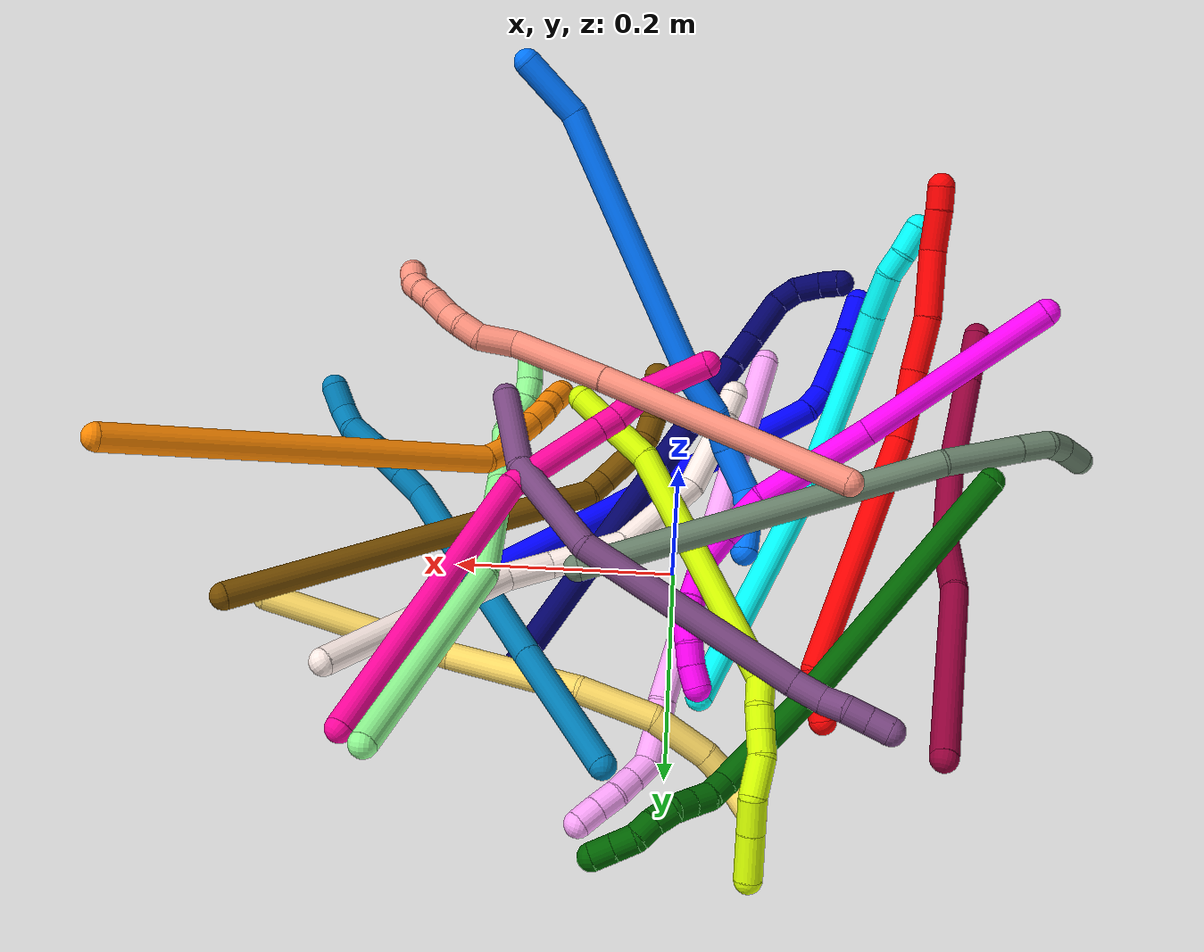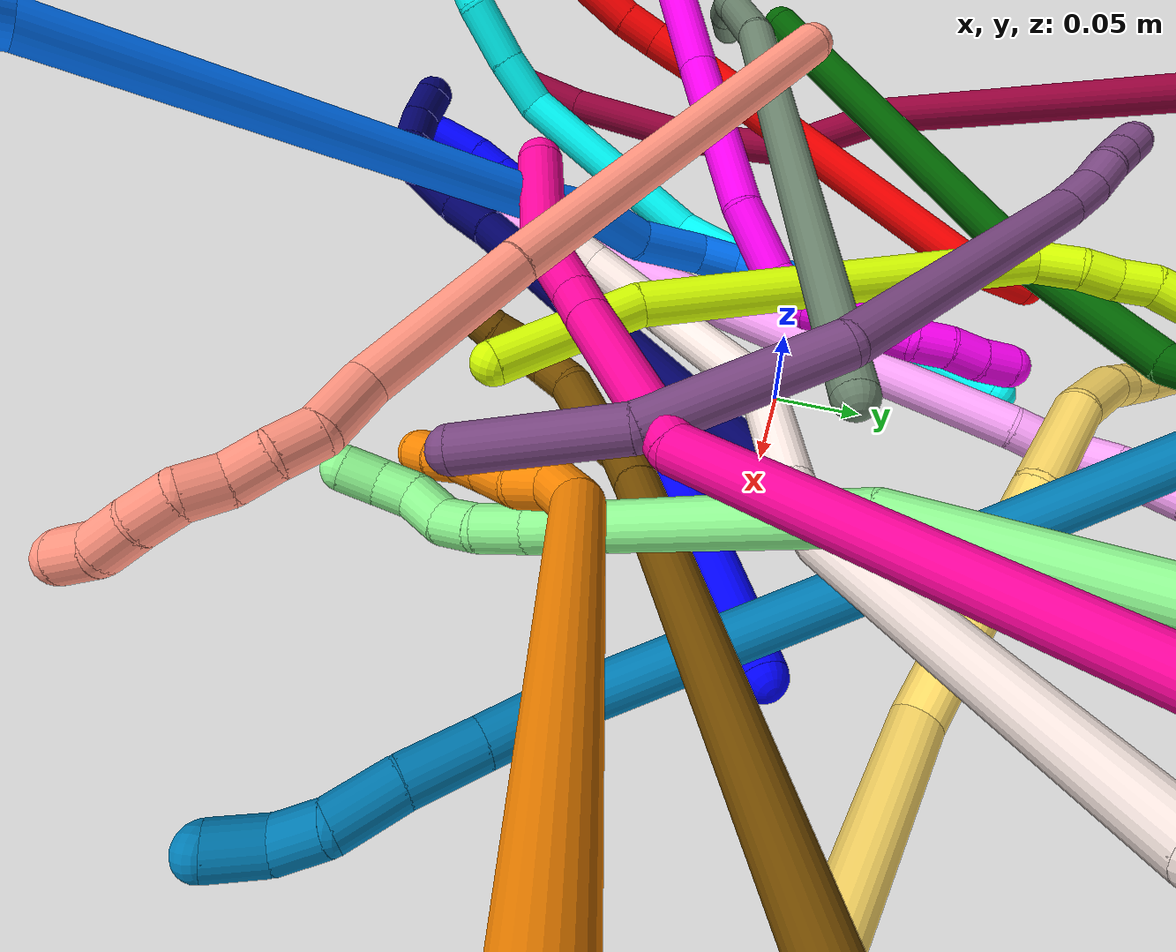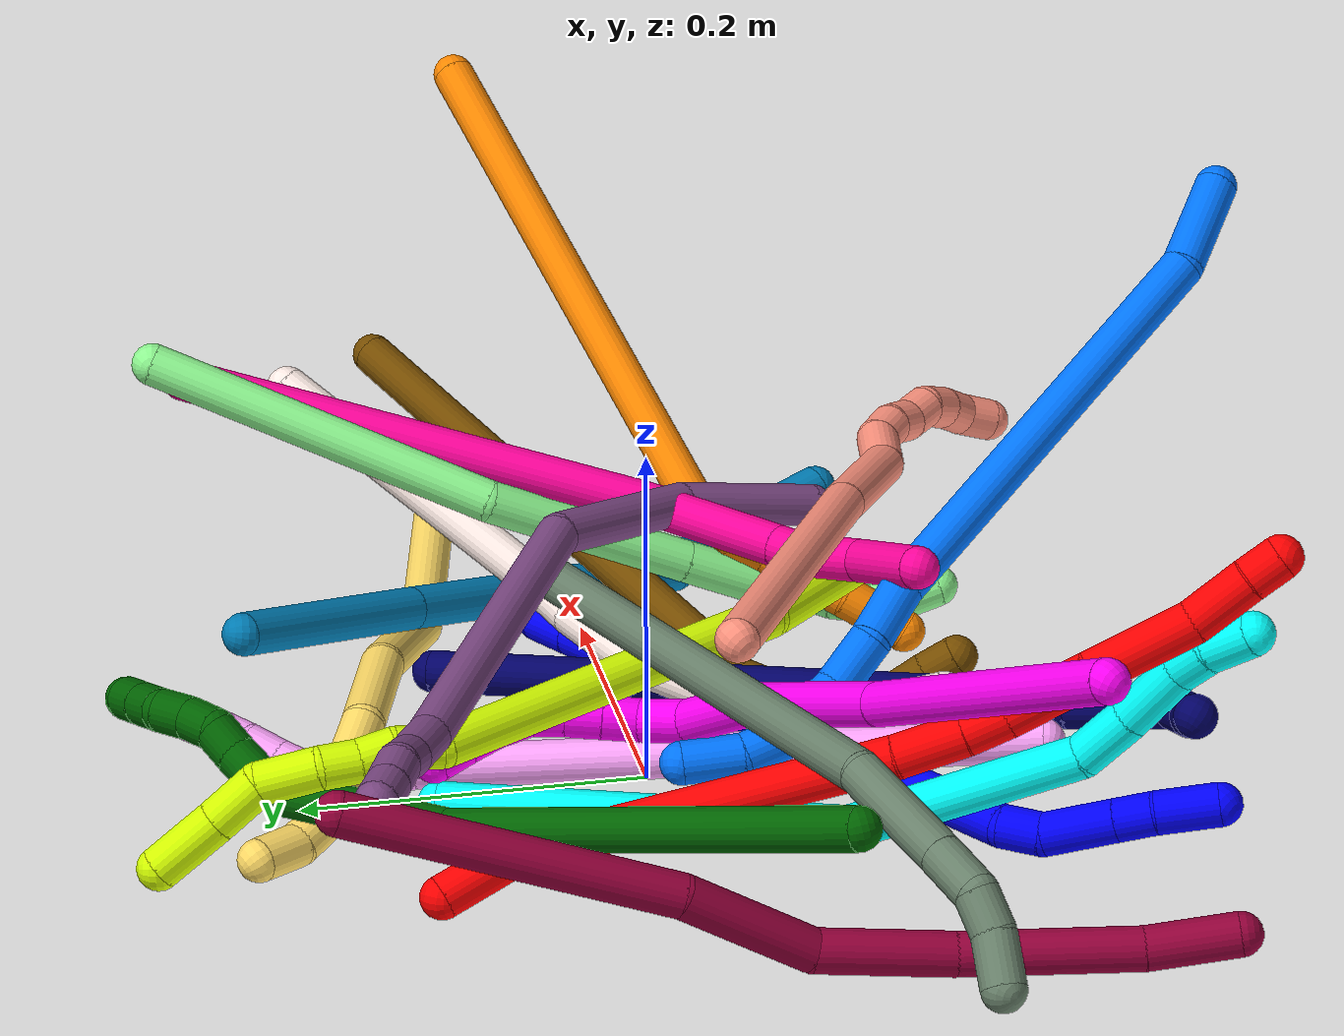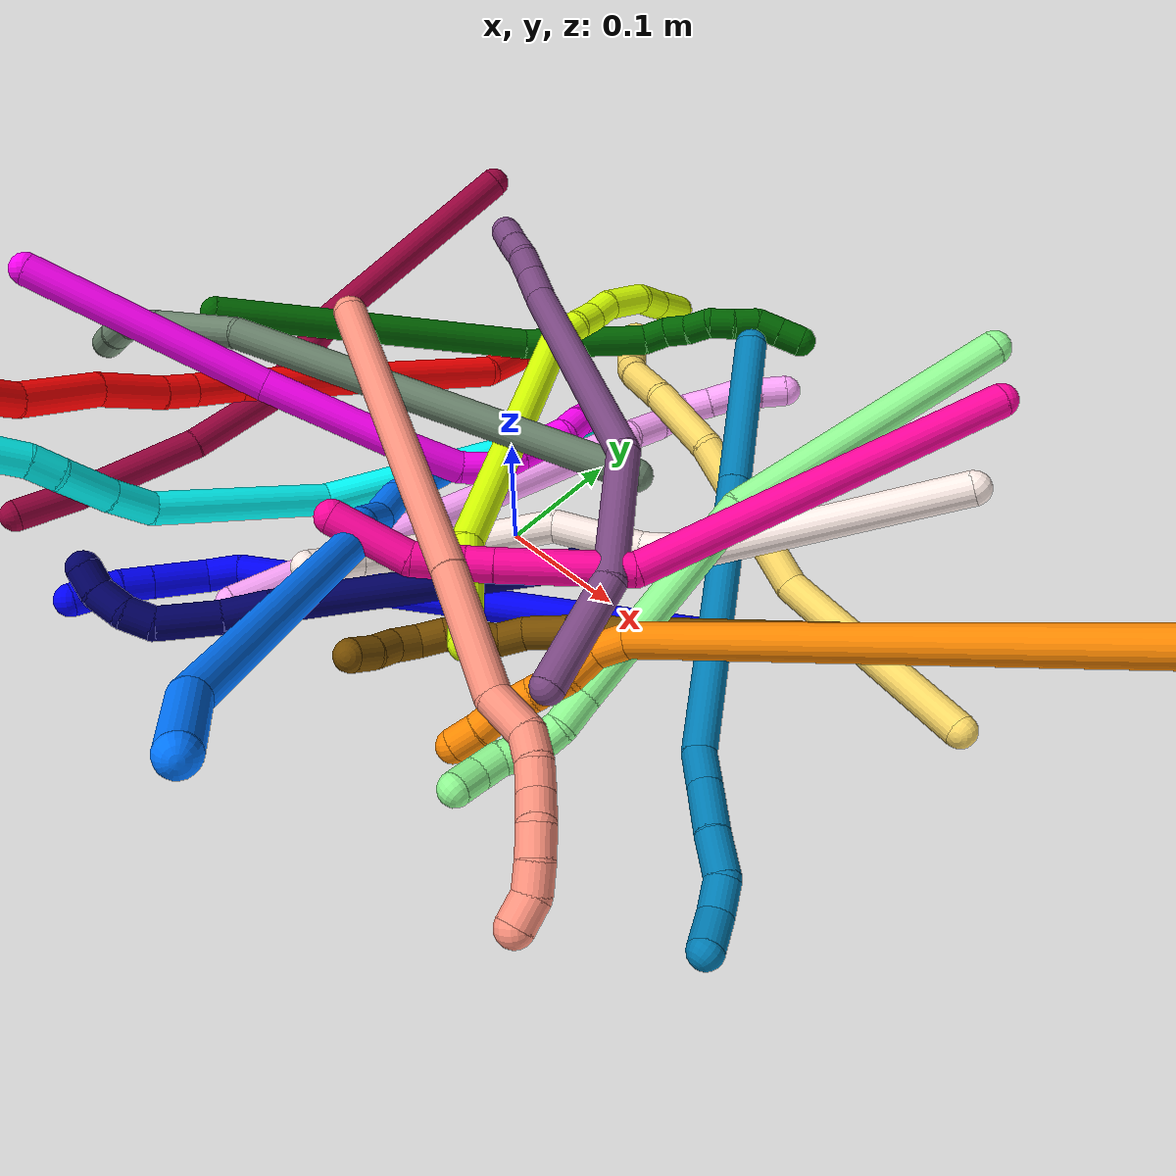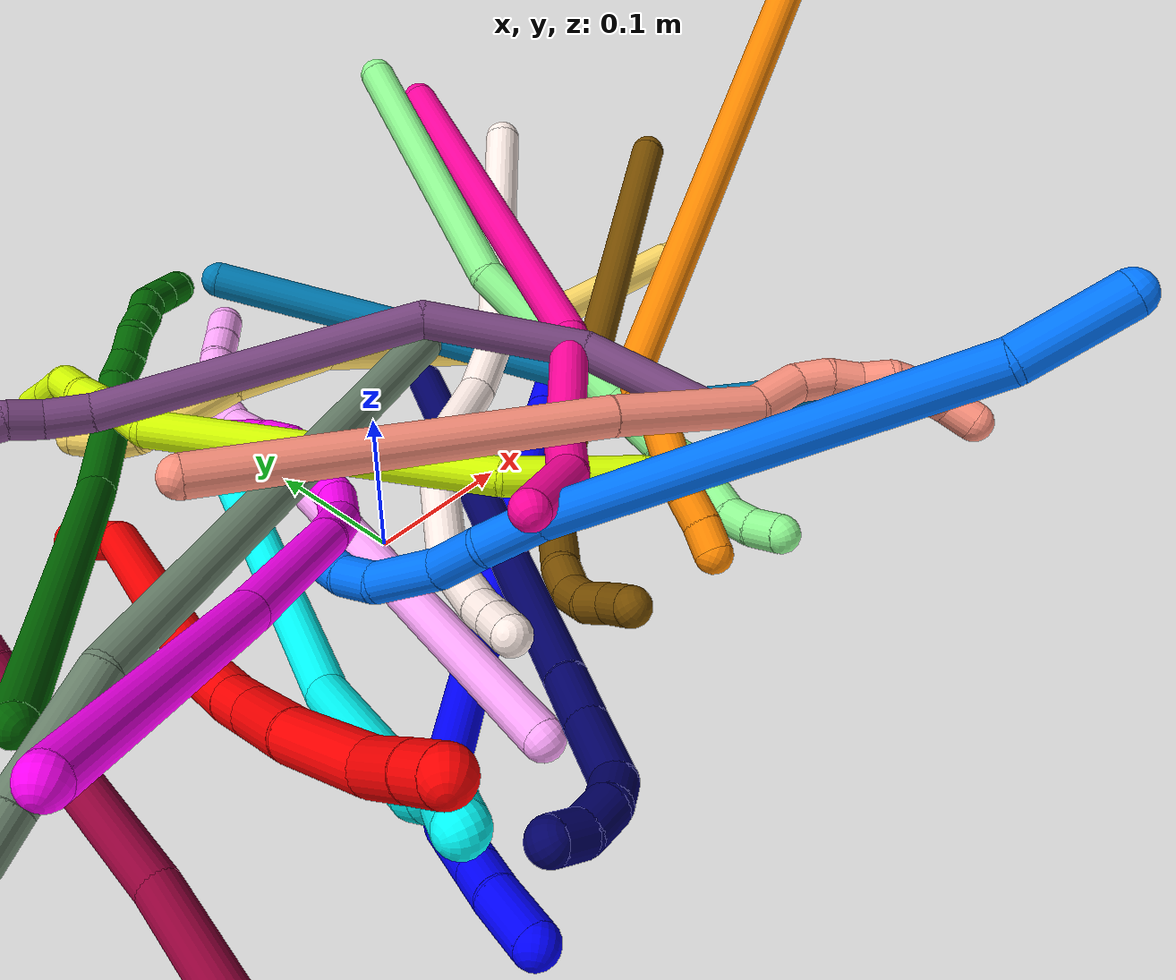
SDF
<sdf version="1.7">
 <world name="default">
  <plugin name="TubeGeneratorPlugin" filename="libtube_generator_plugin.so"/>
  <model name="photoneo_s_sensor">
   <static>1</static>
   <pose>0 0 2 1.57079 1.57079 3.14159</pose>
   <link name="link">
    <inertial><mass>0.1</mass></inertial>
    <sensor name="sensor" type="depth">
     <update_rate>30</update_rate>
     <camera>
      <horizontal_fov>1.22</horizontal_fov>
      <image><width>1920</width><height>1200</height><format>B8G8R8</format></image>
      <clip><near>0.1</near><far>4</far></clip>
      <depth_camera><output>points</output></depth_camera>
     </camera>
     <plugin name="camera_plugin" filename="libgazebo_ros_depth_camera.so">
      <baseline>0.2</baseline>
      <alwaysOn>1</alwaysOn>
      <updateRate>0.0</updateRate>
      <cameraName>camera_ir</cameraName>
      <imageTopicName>/camera/color/image_raw</imageTopicName>
      <cameraInfoTopicName>/camera/color/camera_info</cameraInfoTopicName>
      <depthImageTopicName>/camera/depth/image_raw</depthImageTopicName>
      <depthImageCameraInfoTopicName>/camera/depth/camera_info</depthImageCameraInfoTopicName>
      <pointCloudTopicName>/camera/depth/points</pointCloudTopicName>
      <frameName>fr_optical</frameName>
      <pointCloudCutoff>0.1</pointCloudCutoff>
      <pointCloudCutoffMax>2.0</pointCloudCutoffMax>
      <distortionK1>0</distortionK1>
      <distortionK2>0</distortionK2>
      <distortionK3>0</distortionK3>
      <distortionT1>0</distortionT1>
      <distortionT2>0</distortionT2>
      <CxPrime>0</CxPrime>
      <Cx>0</Cx>
      <Cy>0</Cy>
      <focalLength>0</focalLength>
      <hackBaseline>0</hackBaseline>
     </plugin>
    </sensor>
   </link>
  </model>
  <gravity>0 0 -9.8</gravity>
  <magnetic_field>6e-06 2.3e-05 -4.2e-05</magnetic_field>
  <atmosphere type="adiabatic"/>
  <physics name="default_physics" default="0" type="ode">
   <max_step_size>0.003</max_step_size>
   <real_time_factor>1</real_time_factor>
   <real_time_update_rate>1000</real_time_update_rate>
   <max_contacts>10000</max_contacts>
   <ode>
    <solver>
     <type>quick</type>
     <iters>100</iters>
     <sor>1.3</sor>
     <use_dynamic_moi_rescaling>0</use_dynamic_moi_rescaling>
    </solver>
    <constraints>
     <contact_max_correcting_vel>0</contact_max_correcting_vel>
     <contact_surface_layer>0.001</contact_surface_layer>
     <cfm>0</cfm>
     <erp>0.2</erp>
    </constraints>
   </ode>
  </physics>
  <scene><ambient>0.4 0.4 0.4 1</ambient><background>0.7 0.7 0.7 1</background><shadows>0</shadows></scene>
  <audio><device>default</device></audio>
  <spherical_coordinates>
   <surface_model>EARTH_WGS84</surface_model>
   <latitude_deg>0</latitude_deg>
   <longitude_deg>0</longitude_deg>
   <elevation>0</elevation>
   <heading_deg>0</heading_deg>
  </spherical_coordinates>
  <model name="bin">
   <static>1</static>
   <link name="bottom">
    <collision name="collision-bottom">
     <pose>0 0 -0.01 0 -0 0</pose>
     <geometry><box><size>0.8 0.6 0.02</size></box></geometry>
     <surface>
      <friction><ode><mu>100</mu><mu2>100</mu2></ode></friction>
      <contact><collide_bitmask>65535</collide_bitmask></contact>
     </surface>
    </collision>
   </link>
   <link name="west_wall">
    <collision name="collision-west_wall">
     <pose>-0.41 0 0.1 0 -0 0</pose>
     <geometry><box><size>0.02 0.6 0.2</size></box></geometry>
     <surface>
      <friction><ode><mu>100</mu><mu2>100</mu2></ode></friction>
      <contact><collide_bitmask>65535</collide_bitmask></contact>
     </surface>
    </collision>
   </link>
   <link name="east_wall">
    <collision name="collision-east_wall">
     <pose>0.41 0 0.1 0 -0 0</pose>
     <geometry><box><size>0.02 0.6 0.2</size></box></geometry>
     <surface>
      <friction><ode><mu>100</mu><mu2>100</mu2></ode></friction>
      <contact><collide_bitmask>65535</collide_bitmask></contact>
     </surface>
    </collision>
   </link>
   <link name="south_wall">
    <collision name="collision-south_wall">
     <pose>0 -0.31 0.1 0 -0 0</pose>
     <geometry><box><size>0.8 0.02 0.2</size></box></geometry>
     <surface>
      <friction><ode><mu>100</mu><mu2>100</mu2></ode></friction>
      <contact><collide_bitmask>65535</collide_bitmask></contact>
     </surface>
    </collision>
   </link>
   <link name="north_wall">
    <collision name="collision-north_wall">
     <pose>0 0.31 0.1 0 -0 0</pose>
     <geometry><box><size>0.8 0.02 0.2</size></box></geometry>
     <surface>
      <friction><ode><mu>100</mu><mu2>100</mu2></ode></friction>
      <contact><collide_bitmask>65535</collide_bitmask></contact>
     </surface>
    </collision>
   </link>
  </model>
  <model name="1">
   <static>0</static>
   <link name="1">
    <collision name="collision-cylinder-e_1_1_4">
     <pose>-0.002743 -0.00276 0.014344 0.190089 -0.18565 -0.017749</pose>
     <geometry><cylinder><radius>0.0125</radius><length>0.029725</length></cylinder></geometry>
     <surface>
      <friction><ode><mu>1.16</mu><mu2>1.16</mu2><slip1>0</slip1><slip2>0</slip2></ode></friction>
      <contact><ode><kp>1e+06</kp><kd>1</kd><max_vel>0</max_vel><min_depth>0.001</min_depth></ode></contact>
     </surface>
    </collision>
    <visual name="visual-cylinder-e_1_1_4">
     <pose>-0.002743 -0.00276 0.014344 0.190089 -0.18565 -0.017749</pose>
     <geometry><cylinder><radius>0.0125</radius><length>0.029725</length></cylinder></geometry>
     <material><ambient>0 0 1 1</ambient></material>
    </visual>
    <collision name="collision-cylinder-e_2_4_5">
     <pose>-0.038014 -0.034266 0.1955 0.170651 -0.189849 -0.016287</pose>
     <geometry><cylinder><radius>0.0125</radius><length>0.344736</length></cylinder></geometry>
     <surface>
      <friction><ode><mu>1.16</mu><mu2>1.16</mu2><slip1>0</slip1><slip2>0</slip2></ode></friction>
      <contact><ode><kp>1e+06</kp><kd>1</kd><max_vel>0</max_vel><min_depth>0.001</min_depth></ode></contact>
     </surface>
    </collision>
    <visual name="visual-cylinder-e_2_4_5">
     <pose>-0.038014 -0.034266 0.1955 0.170651 -0.189849 -0.016287</pose>
     <geometry><cylinder><radius>0.0125</radius><length>0.344736</length></cylinder></geometry>
     <material><ambient>0 0 1 1</ambient></material>
    </visual>
    <collision name="collision-cylinder-e_3_5_6">
     <pose>-0.074995 -0.061078 0.373693 -0.168332 -0.368171 0.031414</pose>
     <geometry><cylinder><radius>0.0125</radius><length>0.024744</length></cylinder></geometry>
     <surface>
      <friction><ode><mu>1.16</mu><mu2>1.16</mu2><slip1>0</slip1><slip2>0</slip2></ode></friction>
      <contact><ode><kp>1e+06</kp><kd>1</kd><max_vel>0</max_vel><min_depth>0.001</min_depth></ode></contact>
     </surface>
    </collision>
    <visual name="visual-cylinder-e_3_5_6">
     <pose>-0.074995 -0.061078 0.373693 -0.168332 -0.368171 0.031414</pose>
     <geometry><cylinder><radius>0.0125</radius><length>0.024744</length></cylinder></geometry>
     <material><ambient>0 0 1 1</ambient></material>
    </visual>
    <collision name="collision-cylinder-e_4_6_7">
     <pose>-0.093883 -0.055269 0.400102 -0.252387 -0.749143 0.099669</pose>
     <geometry><cylinder><radius>0.0125</radius><length>0.042393</length></cylinder></geometry>
     <surface>
      <friction><ode><mu>1.16</mu><mu2>1.16</mu2><slip1>0</slip1><slip2>0</slip2></ode></friction>
      <contact><ode><kp>1e+06</kp><kd>1</kd><max_vel>0</max_vel><min_depth>0.001</min_depth></ode></contact>
     </surface>
    </collision>
    <visual name="visual-cylinder-e_4_6_7">
     <pose>-0.093883 -0.055269 0.400102 -0.252387 -0.749143 0.099669</pose>
     <geometry><cylinder><radius>0.0125</radius><length>0.042393</length></cylinder></geometry>
     <material><ambient>0 0 1 1</ambient></material>
    </visual>
    <collision name="collision-cylinder-e_5_7_8">
     <pose>-0.115845 -0.049323 0.423038 -0.255995 -0.744322 0.100393</pose>
     <geometry><cylinder><radius>0.0125</radius><length>0.022222</length></cylinder></geometry>
     <surface>
      <friction><ode><mu>1.16</mu><mu2>1.16</mu2><slip1>0</slip1><slip2>0</slip2></ode></friction>
      <contact><ode><kp>1e+06</kp><kd>1</kd><max_vel>0</max_vel><min_depth>0.001</min_depth></ode></contact>
     </surface>
    </collision>
    <visual name="visual-cylinder-e_5_7_8">
     <pose>-0.115845 -0.049323 0.423038 -0.255995 -0.744322 0.100393</pose>
     <geometry><cylinder><radius>0.0125</radius><length>0.022222</length></cylinder></geometry>
     <material><ambient>0 0 1 1</ambient></material>
    </visual>
    <collision name="collision-cylinder-e_6_8_2">
     <pose>-0.134772 -0.04124 0.443638 -0.442454 -0.681776 0.159229</pose>
     <geometry><cylinder><radius>0.0125</radius><length>0.03618</length></cylinder></geometry>
     <surface>
      <friction><ode><mu>1.16</mu><mu2>1.16</mu2><slip1>0</slip1><slip2>0</slip2></ode></friction>
      <contact><ode><kp>1e+06</kp><kd>1</kd><max_vel>0</max_vel><min_depth>0.001</min_depth></ode></contact>
     </surface>
    </collision>
    <visual name="visual-cylinder-e_6_8_2">
     <pose>-0.134772 -0.04124 0.443638 -0.442454 -0.681776 0.159229</pose>
     <geometry><cylinder><radius>0.0125</radius><length>0.03618</length></cylinder></geometry>
     <material><ambient>0 0 1 1</ambient></material>
    </visual>
    <collision name="collision-sphere-2">
     <pose>-0.146172 -0.035226 0.456332 0 -0 0</pose>
     <geometry><sphere><radius>0.0125</radius></sphere></geometry>
     <surface>
      <friction><ode><mu>1.16</mu><mu2>1.16</mu2><slip1>0</slip1><slip2>0</slip2></ode></friction>
      <contact><ode><kp>1e+06</kp><kd>1</kd><max_vel>0</max_vel><min_depth>0.001</min_depth></ode></contact>
     </surface>
    </collision>
    <visual name="visual-sphere-2">
     <pose>-0.146172 -0.035226 0.456332 0 -0 0</pose>
     <geometry><sphere><radius>0.0125</radius></sphere></geometry>
     <material><ambient>0 0 1 1</ambient></material>
    </visual>
    <collision name="collision-sphere-4">
     <pose>-0.005487 -0.00552 0.028688 0 -0 0</pose>
     <geometry><sphere><radius>0.0125</radius></sphere></geometry>
     <surface>
      <friction><ode><mu>1.16</mu><mu2>1.16</mu2><slip1>0</slip1><slip2>0</slip2></ode></friction>
      <contact><ode><kp>1e+06</kp><kd>1</kd><max_vel>0</max_vel><min_depth>0.001</min_depth></ode></contact>
     </surface>
    </collision>
    <visual name="visual-sphere-4">
     <pose>-0.005487 -0.00552 0.028688 0 -0 0</pose>
     <geometry><sphere><radius>0.0125</radius></sphere></geometry>
     <material><ambient>0 0 1 1</ambient></material>
    </visual>
    <collision name="collision-sphere-1">
     <geometry><sphere><radius>0.0125</radius></sphere></geometry>
     <surface>
      <friction><ode><mu>1.16</mu><mu2>1.16</mu2><slip1>0</slip1><slip2>0</slip2></ode></friction>
      <contact><ode><kp>1e+06</kp><kd>1</kd><max_vel>0</max_vel><min_depth>0.001</min_depth></ode></contact>
     </surface>
    </collision>
    <visual name="visual-sphere-1">
     <geometry><sphere><radius>0.0125</radius></sphere></geometry>
     <material><ambient>0 0 1 1</ambient></material>
    </visual>
    <collision name="collision-sphere-8">
     <pose>-0.123372 -0.047254 0.430945 0 -0 0</pose>
     <geometry><sphere><radius>0.0125</radius></sphere></geometry>
     <surface>
      <friction><ode><mu>1.16</mu><mu2>1.16</mu2><slip1>0</slip1><slip2>0</slip2></ode></friction>
      <contact><ode><kp>1e+06</kp><kd>1</kd><max_vel>0</max_vel><min_depth>0.001</min_depth></ode></contact>
     </surface>
    </collision>
    <visual name="visual-sphere-8">
     <pose>-0.123372 -0.047254 0.430945 0 -0 0</pose>
     <geometry><sphere><radius>0.0125</radius></sphere></geometry>
     <material><ambient>0 0 1 1</ambient></material>
    </visual>
    <collision name="collision-sphere-5">
     <pose>-0.070542 -0.063012 0.362313 0 -0 0</pose>
     <geometry><sphere><radius>0.0125</radius></sphere></geometry>
     <surface>
      <friction><ode><mu>1.16</mu><mu2>1.16</mu2><slip1>0</slip1><slip2>0</slip2></ode></friction>
      <contact><ode><kp>1e+06</kp><kd>1</kd><max_vel>0</max_vel><min_depth>0.001</min_depth></ode></contact>
     </surface>
    </collision>
    <visual name="visual-sphere-5">
     <pose>-0.070542 -0.063012 0.362313 0 -0 0</pose>
     <geometry><sphere><radius>0.0125</radius></sphere></geometry>
     <material><ambient>0 0 1 1</ambient></material>
    </visual>
    <collision name="collision-sphere-6">
     <pose>-0.079448 -0.059145 0.385073 0 -0 0</pose>
     <geometry><sphere><radius>0.0125</radius></sphere></geometry>
     <surface>
      <friction><ode><mu>1.16</mu><mu2>1.16</mu2><slip1>0</slip1><slip2>0</slip2></ode></friction>
      <contact><ode><kp>1e+06</kp><kd>1</kd><max_vel>0</max_vel><min_depth>0.001</min_depth></ode></contact>
     </surface>
    </collision>
    <visual name="visual-sphere-6">
     <pose>-0.079448 -0.059145 0.385073 0 -0 0</pose>
     <geometry><sphere><radius>0.0125</radius></sphere></geometry>
     <material><ambient>0 0 1 1</ambient></material>
    </visual>
    <collision name="collision-sphere-7">
     <pose>-0.108318 -0.051393 0.415132 0 -0 0</pose>
     <geometry><sphere><radius>0.0125</radius></sphere></geometry>
     <surface>
      <friction><ode><mu>1.16</mu><mu2>1.16</mu2><slip1>0</slip1><slip2>0</slip2></ode></friction>
      <contact><ode><kp>1e+06</kp><kd>1</kd><max_vel>0</max_vel><min_depth>0.001</min_depth></ode></contact>
     </surface>
    </collision>
    <visual name="visual-sphere-7">
     <pose>-0.108318 -0.051393 0.415132 0 -0 0</pose>
     <geometry><sphere><radius>0.0125</radius></sphere></geometry>
     <material><ambient>0 0 1 1</ambient></material>
    </visual>
    <inertial>
     <pose>-0.052945 -0.036675 0.238964 0 -0 0</pose>
     <mass>0.5</mass>
     <inertia>
      <ixx>0.003317</ixx>
      <ixy>0</ixy>
      <ixz>0</ixz>
      <iyy>0.003343</iyy>
      <iyz>0</iyz>
      <izz>0.001262</izz>
     </inertia>
    </inertial>
   </link>
   <pose>0.19271 0.027213 0.011486 -2.02783 0.98077 1.80543</pose>
  </model>
  <model name="2">
   <static>0</static>
   <link name="2">
    <collision name="collision-cylinder-e_1_1_4">
     <pose>-0.006942 -0.017919 0.013159 0.937369 -0.302648 -0.154109</pose>
     <geometry><cylinder><radius>0.0125</radius><length>0.046581</length></cylinder></geometry>
     <surface>
      <friction><ode><mu>1.16</mu><mu2>1.16</mu2><slip1>0</slip1><slip2>0</slip2></ode></friction>
      <contact><ode><kp>1e+06</kp><kd>1</kd><max_vel>0</max_vel><min_depth>0.001</min_depth></ode></contact>
     </surface>
    </collision>
    <visual name="visual-cylinder-e_1_1_4">
     <pose>-0.006942 -0.017919 0.013159 0.937369 -0.302648 -0.154109</pose>
     <geometry><cylinder><radius>0.0125</radius><length>0.046581</length></cylinder></geometry>
     <material><ambient>1 0 0 1</ambient></material>
    </visual>
    <collision name="collision-cylinder-e_2_4_5">
     <pose>-0.021427 -0.086339 0.123754 0.478177 -0.068625 -0.016733</pose>
     <geometry><cylinder><radius>0.0125</radius><length>0.220008</length></cylinder></geometry>
     <surface>
      <friction><ode><mu>1.16</mu><mu2>1.16</mu2><slip1>0</slip1><slip2>0</slip2></ode></friction>
      <contact><ode><kp>1e+06</kp><kd>1</kd><max_vel>0</max_vel><min_depth>0.001</min_depth></ode></contact>
     </surface>
    </collision>
    <visual name="visual-cylinder-e_2_4_5">
     <pose>-0.021427 -0.086339 0.123754 0.478177 -0.068625 -0.016733</pose>
     <geometry><cylinder><radius>0.0125</radius><length>0.220008</length></cylinder></geometry>
     <material><ambient>1 0 0 1</ambient></material>
    </visual>
    <collision name="collision-cylinder-e_3_5_6">
     <pose>-0.031318 -0.14754 0.23736 0.584617 -0.120539 -0.036314</pose>
     <geometry><cylinder><radius>0.0125</radius><length>0.039065</length></cylinder></geometry>
     <surface>
      <friction><ode><mu>1.16</mu><mu2>1.16</mu2><slip1>0</slip1><slip2>0</slip2></ode></friction>
      <contact><ode><kp>1e+06</kp><kd>1</kd><max_vel>0</max_vel><min_depth>0.001</min_depth></ode></contact>
     </surface>
    </collision>
    <visual name="visual-cylinder-e_3_5_6">
     <pose>-0.031318 -0.14754 0.23736 0.584617 -0.120539 -0.036314</pose>
     <geometry><cylinder><radius>0.0125</radius><length>0.039065</length></cylinder></geometry>
     <material><ambient>1 0 0 1</ambient></material>
    </visual>
    <collision name="collision-cylinder-e_4_6_7">
     <pose>-0.034874 -0.165921 0.263244 0.668945 -0.097182 -0.033797</pose>
     <geometry><cylinder><radius>0.0125</radius><length>0.024882</length></cylinder></geometry>
     <surface>
      <friction><ode><mu>1.16</mu><mu2>1.16</mu2><slip1>0</slip1><slip2>0</slip2></ode></friction>
      <contact><ode><kp>1e+06</kp><kd>1</kd><max_vel>0</max_vel><min_depth>0.001</min_depth></ode></contact>
     </surface>
    </collision>
    <visual name="visual-cylinder-e_4_6_7">
     <pose>-0.034874 -0.165921 0.263244 0.668945 -0.097182 -0.033797</pose>
     <geometry><cylinder><radius>0.0125</radius><length>0.024882</length></cylinder></geometry>
     <material><ambient>1 0 0 1</ambient></material>
    </visual>
    <collision name="collision-cylinder-e_5_7_8">
     <pose>-0.035489 -0.189228 0.292495 0.674713 0.023679 0.008306</pose>
     <geometry><cylinder><radius>0.0125</radius><length>0.050052</length></cylinder></geometry>
     <surface>
      <friction><ode><mu>1.16</mu><mu2>1.16</mu2><slip1>0</slip1><slip2>0</slip2></ode></friction>
      <contact><ode><kp>1e+06</kp><kd>1</kd><max_vel>0</max_vel><min_depth>0.001</min_depth></ode></contact>
     </surface>
    </collision>
    <visual name="visual-cylinder-e_5_7_8">
     <pose>-0.035489 -0.189228 0.292495 0.674713 0.023679 0.008306</pose>
     <geometry><cylinder><radius>0.0125</radius><length>0.050052</length></cylinder></geometry>
     <material><ambient>1 0 0 1</ambient></material>
    </visual>
    <collision name="collision-cylinder-e_6_8_9">
     <pose>-0.039434 -0.225745 0.334002 0.76017 -0.148586 -0.059454</pose>
     <geometry><cylinder><radius>0.0125</radius><length>0.061305</length></cylinder></geometry>
     <surface>
      <friction><ode><mu>1.16</mu><mu2>1.16</mu2><slip1>0</slip1><slip2>0</slip2></ode></friction>
      <contact><ode><kp>1e+06</kp><kd>1</kd><max_vel>0</max_vel><min_depth>0.001</min_depth></ode></contact>
     </surface>
    </collision>
    <visual name="visual-cylinder-e_6_8_9">
     <pose>-0.039434 -0.225745 0.334002 0.76017 -0.148586 -0.059454</pose>
     <geometry><cylinder><radius>0.0125</radius><length>0.061305</length></cylinder></geometry>
     <material><ambient>1 0 0 1</ambient></material>
    </visual>
    <collision name="collision-cylinder-e_7_9_10">
     <pose>-0.042362 -0.260451 0.368372 0.839395 0.086473 0.038604</pose>
     <geometry><cylinder><radius>0.0125</radius><length>0.037271</length></cylinder></geometry>
     <surface>
      <friction><ode><mu>1.16</mu><mu2>1.16</mu2><slip1>0</slip1><slip2>0</slip2></ode></friction>
      <contact><ode><kp>1e+06</kp><kd>1</kd><max_vel>0</max_vel><min_depth>0.001</min_depth></ode></contact>
     </surface>
    </collision>
    <visual name="visual-cylinder-e_7_9_10">
     <pose>-0.042362 -0.260451 0.368372 0.839395 0.086473 0.038604</pose>
     <geometry><cylinder><radius>0.0125</radius><length>0.037271</length></cylinder></geometry>
     <material><ambient>1 0 0 1</ambient></material>
    </visual>
    <collision name="collision-cylinder-e_8_10_2">
     <pose>-0.040845 -0.282134 0.387603 0.855687 -0.008854 -0.004037</pose>
     <geometry><cylinder><radius>0.0125</radius><length>0.020836</length></cylinder></geometry>
     <surface>
      <friction><ode><mu>1.16</mu><mu2>1.16</mu2><slip1>0</slip1><slip2>0</slip2></ode></friction>
      <contact><ode><kp>1e+06</kp><kd>1</kd><max_vel>0</max_vel><min_depth>0.001</min_depth></ode></contact>
     </surface>
    </collision>
    <visual name="visual-cylinder-e_8_10_2">
     <pose>-0.040845 -0.282134 0.387603 0.855687 -0.008854 -0.004037</pose>
     <geometry><cylinder><radius>0.0125</radius><length>0.020836</length></cylinder></geometry>
     <material><ambient>1 0 0 1</ambient></material>
    </visual>
    <collision name="collision-sphere-2">
     <pose>-0.040937 -0.289999 0.394434 0 -0 0</pose>
     <geometry><sphere><radius>0.0125</radius></sphere></geometry>
     <surface>
      <friction><ode><mu>1.16</mu><mu2>1.16</mu2><slip1>0</slip1><slip2>0</slip2></ode></friction>
      <contact><ode><kp>1e+06</kp><kd>1</kd><max_vel>0</max_vel><min_depth>0.001</min_depth></ode></contact>
     </surface>
    </collision>
    <visual name="visual-sphere-2">
     <pose>-0.040937 -0.289999 0.394434 0 -0 0</pose>
     <geometry><sphere><radius>0.0125</radius></sphere></geometry>
     <material><ambient>1 0 0 1</ambient></material>
    </visual>
    <collision name="collision-sphere-10">
     <pose>-0.040753 -0.274269 0.380772 0 -0 0</pose>
     <geometry><sphere><radius>0.0125</radius></sphere></geometry>
     <surface>
      <friction><ode><mu>1.16</mu><mu2>1.16</mu2><slip1>0</slip1><slip2>0</slip2></ode></friction>
      <contact><ode><kp>1e+06</kp><kd>1</kd><max_vel>0</max_vel><min_depth>0.001</min_depth></ode></contact>
     </surface>
    </collision>
    <visual name="visual-sphere-10">
     <pose>-0.040753 -0.274269 0.380772 0 -0 0</pose>
     <geometry><sphere><radius>0.0125</radius></sphere></geometry>
     <material><ambient>1 0 0 1</ambient></material>
    </visual>
    <collision name="collision-sphere-9">
     <pose>-0.043972 -0.246634 0.355971 0 -0 0</pose>
     <geometry><sphere><radius>0.0125</radius></sphere></geometry>
     <surface>
      <friction><ode><mu>1.16</mu><mu2>1.16</mu2><slip1>0</slip1><slip2>0</slip2></ode></friction>
      <contact><ode><kp>1e+06</kp><kd>1</kd><max_vel>0</max_vel><min_depth>0.001</min_depth></ode></contact>
     </surface>
    </collision>
    <visual name="visual-sphere-9">
     <pose>-0.043972 -0.246634 0.355971 0 -0 0</pose>
     <geometry><sphere><radius>0.0125</radius></sphere></geometry>
     <material><ambient>1 0 0 1</ambient></material>
    </visual>
    <collision name="collision-sphere-4">
     <pose>-0.013883 -0.035838 0.026319 0 -0 0</pose>
     <geometry><sphere><radius>0.0125</radius></sphere></geometry>
     <surface>
      <friction><ode><mu>1.16</mu><mu2>1.16</mu2><slip1>0</slip1><slip2>0</slip2></ode></friction>
      <contact><ode><kp>1e+06</kp><kd>1</kd><max_vel>0</max_vel><min_depth>0.001</min_depth></ode></contact>
     </surface>
    </collision>
    <visual name="visual-sphere-4">
     <pose>-0.013883 -0.035838 0.026319 0 -0 0</pose>
     <geometry><sphere><radius>0.0125</radius></sphere></geometry>
     <material><ambient>1 0 0 1</ambient></material>
    </visual>
    <collision name="collision-sphere-1">
     <geometry><sphere><radius>0.0125</radius></sphere></geometry>
     <surface>
      <friction><ode><mu>1.16</mu><mu2>1.16</mu2><slip1>0</slip1><slip2>0</slip2></ode></friction>
      <contact><ode><kp>1e+06</kp><kd>1</kd><max_vel>0</max_vel><min_depth>0.001</min_depth></ode></contact>
     </surface>
    </collision>
    <visual name="visual-sphere-1">
     <geometry><sphere><radius>0.0125</radius></sphere></geometry>
     <material><ambient>1 0 0 1</ambient></material>
    </visual>
    <collision name="collision-sphere-8">
     <pose>-0.034896 -0.204857 0.312032 0 -0 0</pose>
     <geometry><sphere><radius>0.0125</radius></sphere></geometry>
     <surface>
      <friction><ode><mu>1.16</mu><mu2>1.16</mu2><slip1>0</slip1><slip2>0</slip2></ode></friction>
      <contact><ode><kp>1e+06</kp><kd>1</kd><max_vel>0</max_vel><min_depth>0.001</min_depth></ode></contact>
     </surface>
    </collision>
    <visual name="visual-sphere-8">
     <pose>-0.034896 -0.204857 0.312032 0 -0 0</pose>
     <geometry><sphere><radius>0.0125</radius></sphere></geometry>
     <material><ambient>1 0 0 1</ambient></material>
    </visual>
    <collision name="collision-sphere-5">
     <pose>-0.02897 -0.136839 0.22119 0 -0 0</pose>
     <geometry><sphere><radius>0.0125</radius></sphere></geometry>
     <surface>
      <friction><ode><mu>1.16</mu><mu2>1.16</mu2><slip1>0</slip1><slip2>0</slip2></ode></friction>
      <contact><ode><kp>1e+06</kp><kd>1</kd><max_vel>0</max_vel><min_depth>0.001</min_depth></ode></contact>
     </surface>
    </collision>
    <visual name="visual-sphere-5">
     <pose>-0.02897 -0.136839 0.22119 0 -0 0</pose>
     <geometry><sphere><radius>0.0125</radius></sphere></geometry>
     <material><ambient>1 0 0 1</ambient></material>
    </visual>
    <collision name="collision-sphere-6">
     <pose>-0.033667 -0.158242 0.25353 0 -0 0</pose>
     <geometry><sphere><radius>0.0125</radius></sphere></geometry>
     <surface>
      <friction><ode><mu>1.16</mu><mu2>1.16</mu2><slip1>0</slip1><slip2>0</slip2></ode></friction>
      <contact><ode><kp>1e+06</kp><kd>1</kd><max_vel>0</max_vel><min_depth>0.001</min_depth></ode></contact>
     </surface>
    </collision>
    <visual name="visual-sphere-6">
     <pose>-0.033667 -0.158242 0.25353 0 -0 0</pose>
     <geometry><sphere><radius>0.0125</radius></sphere></geometry>
     <material><ambient>1 0 0 1</ambient></material>
    </visual>
    <collision name="collision-sphere-7">
     <pose>-0.036081 -0.1736 0.272958 0 -0 0</pose>
     <geometry><sphere><radius>0.0125</radius></sphere></geometry>
     <surface>
      <friction><ode><mu>1.16</mu><mu2>1.16</mu2><slip1>0</slip1><slip2>0</slip2></ode></friction>
      <contact><ode><kp>1e+06</kp><kd>1</kd><max_vel>0</max_vel><min_depth>0.001</min_depth></ode></contact>
     </surface>
    </collision>
    <visual name="visual-sphere-7">
     <pose>-0.036081 -0.1736 0.272958 0 -0 0</pose>
     <geometry><sphere><radius>0.0125</radius></sphere></geometry>
     <material><ambient>1 0 0 1</ambient></material>
    </visual>
    <inertial>
     <pose>-0.027505 -0.137237 0.201168 0 -0 0</pose>
     <mass>0.5</mass>
     <inertia>
      <ixx>0.000932</ixx>
      <ixy>0</ixy>
      <ixz>0</ixz>
      <iyy>0.000799</iyy>
      <iyz>0</iyz>
      <izz>0.000551</izz>
     </inertia>
    </inertial>
   </link>
   <pose>-0.137813 0.141772 0.011588 -1.48739 -0.772404 2.34294</pose>
  </model>
  <model name="3">
   <static>0</static>
   <link name="3">
    <collision name="collision-cylinder-e_1_1_4">
     <pose>-0.087629 -0.071217 0.028877 1.18557 -0.850845 -0.592445</pose>
     <geometry><cylinder><radius>0.0125</radius><length>0.233106</length></cylinder></geometry>
     <surface>
      <friction><ode><mu>1.16</mu><mu2>1.16</mu2><slip1>0</slip1><slip2>0</slip2></ode></friction>
      <contact><ode><kp>1e+06</kp><kd>1</kd><max_vel>0</max_vel><min_depth>0.001</min_depth></ode></contact>
     </surface>
    </collision>
    <visual name="visual-cylinder-e_1_1_4">
     <pose>-0.087629 -0.071217 0.028877 1.18557 -0.850845 -0.592445</pose>
     <geometry><cylinder><radius>0.0125</radius><length>0.233106</length></cylinder></geometry>
     <material><ambient>0.003922 1 0.996078 1</ambient></material>
    </visual>
    <collision name="collision-cylinder-e_2_4_5">
     <pose>-0.209363 -0.201429 0.071773 1.33751 -0.512349 -0.408204</pose>
     <geometry><cylinder><radius>0.0125</radius><length>0.13914</length></cylinder></geometry>
     <surface>
      <friction><ode><mu>1.16</mu><mu2>1.16</mu2><slip1>0</slip1><slip2>0</slip2></ode></friction>
      <contact><ode><kp>1e+06</kp><kd>1</kd><max_vel>0</max_vel><min_depth>0.001</min_depth></ode></contact>
     </surface>
    </collision>
    <visual name="visual-cylinder-e_2_4_5">
     <pose>-0.209363 -0.201429 0.071773 1.33751 -0.512349 -0.408204</pose>
     <geometry><cylinder><radius>0.0125</radius><length>0.13914</length></cylinder></geometry>
     <material><ambient>0.003922 1 0.996078 1</ambient></material>
    </visual>
    <collision name="collision-cylinder-e_3_5_6">
     <pose>-0.245327 -0.277843 0.089568 1.35729 -0.103904 -0.083817</pose>
     <geometry><cylinder><radius>0.0125</radius><length>0.035843</length></cylinder></geometry>
     <surface>
      <friction><ode><mu>1.16</mu><mu2>1.16</mu2><slip1>0</slip1><slip2>0</slip2></ode></friction>
      <contact><ode><kp>1e+06</kp><kd>1</kd><max_vel>0</max_vel><min_depth>0.001</min_depth></ode></contact>
     </surface>
    </collision>
    <visual name="visual-cylinder-e_3_5_6">
     <pose>-0.245327 -0.277843 0.089568 1.35729 -0.103904 -0.083817</pose>
     <geometry><cylinder><radius>0.0125</radius><length>0.035843</length></cylinder></geometry>
     <material><ambient>0.003922 1 0.996078 1</ambient></material>
    </visual>
    <collision name="collision-cylinder-e_4_6_7">
     <pose>-0.247682 -0.315176 0.098459 1.31941 -0.024104 -0.018696</pose>
     <geometry><cylinder><radius>0.0125</radius><length>0.041129</length></cylinder></geometry>
     <surface>
      <friction><ode><mu>1.16</mu><mu2>1.16</mu2><slip1>0</slip1><slip2>0</slip2></ode></friction>
      <contact><ode><kp>1e+06</kp><kd>1</kd><max_vel>0</max_vel><min_depth>0.001</min_depth></ode></contact>
     </surface>
    </collision>
    <visual name="visual-cylinder-e_4_6_7">
     <pose>-0.247682 -0.315176 0.098459 1.31941 -0.024104 -0.018696</pose>
     <geometry><cylinder><radius>0.0125</radius><length>0.041129</length></cylinder></geometry>
     <material><ambient>0.003922 1 0.996078 1</ambient></material>
    </visual>
    <collision name="collision-cylinder-e_5_7_8">
     <pose>-0.249454 -0.345235 0.10874 1.09977 -0.111617 -0.06846</pose>
     <geometry><cylinder><radius>0.0125</radius><length>0.022915</length></cylinder></geometry>
     <surface>
      <friction><ode><mu>1.16</mu><mu2>1.16</mu2><slip1>0</slip1><slip2>0</slip2></ode></friction>
      <contact><ode><kp>1e+06</kp><kd>1</kd><max_vel>0</max_vel><min_depth>0.001</min_depth></ode></contact>
     </surface>
    </collision>
    <visual name="visual-cylinder-e_5_7_8">
     <pose>-0.249454 -0.345235 0.10874 1.09977 -0.111617 -0.06846</pose>
     <geometry><cylinder><radius>0.0125</radius><length>0.022915</length></cylinder></geometry>
     <material><ambient>0.003922 1 0.996078 1</ambient></material>
    </visual>
    <collision name="collision-cylinder-e_6_8_2">
     <pose>-0.255262 -0.367398 0.119308 1.14839 -0.331334 -0.215485</pose>
     <geometry><cylinder><radius>0.0125</radius><length>0.027866</length></cylinder></geometry>
     <surface>
      <friction><ode><mu>1.16</mu><mu2>1.16</mu2><slip1>0</slip1><slip2>0</slip2></ode></friction>
      <contact><ode><kp>1e+06</kp><kd>1</kd><max_vel>0</max_vel><min_depth>0.001</min_depth></ode></contact>
     </surface>
    </collision>
    <visual name="visual-cylinder-e_6_8_2">
     <pose>-0.255262 -0.367398 0.119308 1.14839 -0.331334 -0.215485</pose>
     <geometry><cylinder><radius>0.0125</radius><length>0.027866</length></cylinder></geometry>
     <material><ambient>0.003922 1 0.996078 1</ambient></material>
    </visual>
    <collision name="collision-sphere-2">
     <pose>-0.259795 -0.379415 0.124709 0 -0 0</pose>
     <geometry><sphere><radius>0.0125</radius></sphere></geometry>
     <surface>
      <friction><ode><mu>1.16</mu><mu2>1.16</mu2><slip1>0</slip1><slip2>0</slip2></ode></friction>
      <contact><ode><kp>1e+06</kp><kd>1</kd><max_vel>0</max_vel><min_depth>0.001</min_depth></ode></contact>
     </surface>
    </collision>
    <visual name="visual-sphere-2">
     <pose>-0.259795 -0.379415 0.124709 0 -0 0</pose>
     <geometry><sphere><radius>0.0125</radius></sphere></geometry>
     <material><ambient>0.003922 1 0.996078 1</ambient></material>
    </visual>
    <collision name="collision-sphere-4">
     <pose>-0.175258 -0.142434 0.057755 0 -0 0</pose>
     <geometry><sphere><radius>0.0125</radius></sphere></geometry>
     <surface>
      <friction><ode><mu>1.16</mu><mu2>1.16</mu2><slip1>0</slip1><slip2>0</slip2></ode></friction>
      <contact><ode><kp>1e+06</kp><kd>1</kd><max_vel>0</max_vel><min_depth>0.001</min_depth></ode></contact>
     </surface>
    </collision>
    <visual name="visual-sphere-4">
     <pose>-0.175258 -0.142434 0.057755 0 -0 0</pose>
     <geometry><sphere><radius>0.0125</radius></sphere></geometry>
     <material><ambient>0.003922 1 0.996078 1</ambient></material>
    </visual>
    <collision name="collision-sphere-1">
     <geometry><sphere><radius>0.0125</radius></sphere></geometry>
     <surface>
      <friction><ode><mu>1.16</mu><mu2>1.16</mu2><slip1>0</slip1><slip2>0</slip2></ode></friction>
      <contact><ode><kp>1e+06</kp><kd>1</kd><max_vel>0</max_vel><min_depth>0.001</min_depth></ode></contact>
     </surface>
    </collision>
    <visual name="visual-sphere-1">
     <geometry><sphere><radius>0.0125</radius></sphere></geometry>
     <material><ambient>0.003922 1 0.996078 1</ambient></material>
    </visual>
    <collision name="collision-sphere-8">
     <pose>-0.25073 -0.355381 0.113907 0 -0 0</pose>
     <geometry><sphere><radius>0.0125</radius></sphere></geometry>
     <surface>
      <friction><ode><mu>1.16</mu><mu2>1.16</mu2><slip1>0</slip1><slip2>0</slip2></ode></friction>
      <contact><ode><kp>1e+06</kp><kd>1</kd><max_vel>0</max_vel><min_depth>0.001</min_depth></ode></contact>
     </surface>
    </collision>
    <visual name="visual-sphere-8">
     <pose>-0.25073 -0.355381 0.113907 0 -0 0</pose>
     <geometry><sphere><radius>0.0125</radius></sphere></geometry>
     <material><ambient>0.003922 1 0.996078 1</ambient></material>
    </visual>
    <collision name="collision-sphere-5">
     <pose>-0.243469 -0.260423 0.085791 0 -0 0</pose>
     <geometry><sphere><radius>0.0125</radius></sphere></geometry>
     <surface>
      <friction><ode><mu>1.16</mu><mu2>1.16</mu2><slip1>0</slip1><slip2>0</slip2></ode></friction>
      <contact><ode><kp>1e+06</kp><kd>1</kd><max_vel>0</max_vel><min_depth>0.001</min_depth></ode></contact>
     </surface>
    </collision>
    <visual name="visual-sphere-5">
     <pose>-0.243469 -0.260423 0.085791 0 -0 0</pose>
     <geometry><sphere><radius>0.0125</radius></sphere></geometry>
     <material><ambient>0.003922 1 0.996078 1</ambient></material>
    </visual>
    <collision name="collision-sphere-6">
     <pose>-0.247186 -0.295264 0.093345 0 -0 0</pose>
     <geometry><sphere><radius>0.0125</radius></sphere></geometry>
     <surface>
      <friction><ode><mu>1.16</mu><mu2>1.16</mu2><slip1>0</slip1><slip2>0</slip2></ode></friction>
      <contact><ode><kp>1e+06</kp><kd>1</kd><max_vel>0</max_vel><min_depth>0.001</min_depth></ode></contact>
     </surface>
    </collision>
    <visual name="visual-sphere-6">
     <pose>-0.247186 -0.295264 0.093345 0 -0 0</pose>
     <geometry><sphere><radius>0.0125</radius></sphere></geometry>
     <material><ambient>0.003922 1 0.996078 1</ambient></material>
    </visual>
    <collision name="collision-sphere-7">
     <pose>-0.248177 -0.335088 0.103573 0 -0 0</pose>
     <geometry><sphere><radius>0.0125</radius></sphere></geometry>
     <surface>
      <friction><ode><mu>1.16</mu><mu2>1.16</mu2><slip1>0</slip1><slip2>0</slip2></ode></friction>
      <contact><ode><kp>1e+06</kp><kd>1</kd><max_vel>0</max_vel><min_depth>0.001</min_depth></ode></contact>
     </surface>
    </collision>
    <visual name="visual-sphere-7">
     <pose>-0.248177 -0.335088 0.103573 0 -0 0</pose>
     <geometry><sphere><radius>0.0125</radius></sphere></geometry>
     <material><ambient>0.003922 1 0.996078 1</ambient></material>
    </visual>
    <inertial>
     <pose>-0.162735 -0.171397 0.059589 0 -0 0</pose>
     <mass>0.5</mass>
     <inertia>
      <ixx>0.00029</ixx>
      <ixy>0</ixy>
      <ixz>0</ixz>
      <iyy>0.000341</iyy>
      <iyz>0</iyz>
      <izz>0.001787</izz>
     </inertia>
    </inertial>
   </link>
   <pose>-0.028113 0.124756 0.01149 -1.44109 -0.658985 1.32037</pose>
  </model>
  <model name="4">
   <static>0</static>
   <link name="4">
    <collision name="collision-cylinder-e_1_1_4">
     <pose>0.052653 0.169248 -0.011542 -1.63889 0.300949 -0.321818</pose>
     <geometry><cylinder><radius>0.0125</radius><length>0.355249</length></cylinder></geometry>
     <surface>
      <friction><ode><mu>1.16</mu><mu2>1.16</mu2><slip1>0</slip1><slip2>0</slip2></ode></friction>
      <contact><ode><kp>1e+06</kp><kd>1</kd><max_vel>0</max_vel><min_depth>0.001</min_depth></ode></contact>
     </surface>
    </collision>
    <visual name="visual-cylinder-e_1_1_4">
     <pose>0.052653 0.169248 -0.011542 -1.63889 0.300949 -0.321818</pose>
     <geometry><cylinder><radius>0.0125</radius><length>0.355249</length></cylinder></geometry>
     <material><ambient>1 0.65098 0.996078 1</ambient></material>
    </visual>
    <collision name="collision-cylinder-e_2_4_5">
     <pose>0.10769 0.353217 -0.021815 -1.4848 0.160053 -0.146899</pose>
     <geometry><cylinder><radius>0.0125</radius><length>0.029933</length></cylinder></geometry>
     <surface>
      <friction><ode><mu>1.16</mu><mu2>1.16</mu2><slip1>0</slip1><slip2>0</slip2></ode></friction>
      <contact><ode><kp>1e+06</kp><kd>1</kd><max_vel>0</max_vel><min_depth>0.001</min_depth></ode></contact>
     </surface>
    </collision>
    <visual name="visual-cylinder-e_2_4_5">
     <pose>0.10769 0.353217 -0.021815 -1.4848 0.160053 -0.146899</pose>
     <geometry><cylinder><radius>0.0125</radius><length>0.029933</length></cylinder></geometry>
     <material><ambient>1 0.65098 0.996078 1</ambient></material>
    </visual>
    <collision name="collision-cylinder-e_3_5_6">
     <pose>0.116663 0.381299 -0.021895 -1.67141 0.456039 -0.502476</pose>
     <geometry><cylinder><radius>0.0125</radius><length>0.029916</length></cylinder></geometry>
     <surface>
      <friction><ode><mu>1.16</mu><mu2>1.16</mu2><slip1>0</slip1><slip2>0</slip2></ode></friction>
      <contact><ode><kp>1e+06</kp><kd>1</kd><max_vel>0</max_vel><min_depth>0.001</min_depth></ode></contact>
     </surface>
    </collision>
    <visual name="visual-cylinder-e_3_5_6">
     <pose>0.116663 0.381299 -0.021895 -1.67141 0.456039 -0.502476</pose>
     <geometry><cylinder><radius>0.0125</radius><length>0.029916</length></cylinder></geometry>
     <material><ambient>1 0.65098 0.996078 1</ambient></material>
    </visual>
    <collision name="collision-cylinder-e_4_6_7">
     <pose>0.127396 0.40251 -0.028741 -2.18183 0.408271 -0.757148</pose>
     <geometry><cylinder><radius>0.0125</radius><length>0.020883</length></cylinder></geometry>
     <surface>
      <friction><ode><mu>1.16</mu><mu2>1.16</mu2><slip1>0</slip1><slip2>0</slip2></ode></friction>
      <contact><ode><kp>1e+06</kp><kd>1</kd><max_vel>0</max_vel><min_depth>0.001</min_depth></ode></contact>
     </surface>
    </collision>
    <visual name="visual-cylinder-e_4_6_7">
     <pose>0.127396 0.40251 -0.028741 -2.18183 0.408271 -0.757148</pose>
     <geometry><cylinder><radius>0.0125</radius><length>0.020883</length></cylinder></geometry>
     <material><ambient>1 0.65098 0.996078 1</ambient></material>
    </visual>
    <collision name="collision-cylinder-e_5_7_8">
     <pose>0.136346 0.417974 -0.039859 -2.20649 0.469754 -0.885191</pose>
     <geometry><cylinder><radius>0.0125</radius><length>0.021228</length></cylinder></geometry>
     <surface>
      <friction><ode><mu>1.16</mu><mu2>1.16</mu2><slip1>0</slip1><slip2>0</slip2></ode></friction>
      <contact><ode><kp>1e+06</kp><kd>1</kd><max_vel>0</max_vel><min_depth>0.001</min_depth></ode></contact>
     </surface>
    </collision>
    <visual name="visual-cylinder-e_5_7_8">
     <pose>0.136346 0.417974 -0.039859 -2.20649 0.469754 -0.885191</pose>
     <geometry><cylinder><radius>0.0125</radius><length>0.021228</length></cylinder></geometry>
     <material><ambient>1 0.65098 0.996078 1</ambient></material>
    </visual>
    <collision name="collision-cylinder-e_6_8_9">
     <pose>0.143799 0.433678 -0.052256 -2.26829 0.245926 -0.517743</pose>
     <geometry><cylinder><radius>0.0125</radius><length>0.02176</length></cylinder></geometry>
     <surface>
      <friction><ode><mu>1.16</mu><mu2>1.16</mu2><slip1>0</slip1><slip2>0</slip2></ode></friction>
      <contact><ode><kp>1e+06</kp><kd>1</kd><max_vel>0</max_vel><min_depth>0.001</min_depth></ode></contact>
     </surface>
    </collision>
    <visual name="visual-cylinder-e_6_8_9">
     <pose>0.143799 0.433678 -0.052256 -2.26829 0.245926 -0.517743</pose>
     <geometry><cylinder><radius>0.0125</radius><length>0.02176</length></cylinder></geometry>
     <material><ambient>1 0.65098 0.996078 1</ambient></material>
    </visual>
    <collision name="collision-cylinder-e_7_9_2">
     <pose>0.148923 0.449853 -0.065283 -2.22867 0.237603 -0.476909</pose>
     <geometry><cylinder><radius>0.0125</radius><length>0.021032</length></cylinder></geometry>
     <surface>
      <friction><ode><mu>1.16</mu><mu2>1.16</mu2><slip1>0</slip1><slip2>0</slip2></ode></friction>
      <contact><ode><kp>1e+06</kp><kd>1</kd><max_vel>0</max_vel><min_depth>0.001</min_depth></ode></contact>
     </surface>
    </collision>
    <visual name="visual-cylinder-e_7_9_2">
     <pose>0.148923 0.449853 -0.065283 -2.22867 0.237603 -0.476909</pose>
     <geometry><cylinder><radius>0.0125</radius><length>0.021032</length></cylinder></geometry>
     <material><ambient>1 0.65098 0.996078 1</ambient></material>
    </visual>
    <collision name="collision-sphere-2">
     <pose>0.151398 0.45794 -0.071532 0 -0 0</pose>
     <geometry><sphere><radius>0.0125</radius></sphere></geometry>
     <surface>
      <friction><ode><mu>1.16</mu><mu2>1.16</mu2><slip1>0</slip1><slip2>0</slip2></ode></friction>
      <contact><ode><kp>1e+06</kp><kd>1</kd><max_vel>0</max_vel><min_depth>0.001</min_depth></ode></contact>
     </surface>
    </collision>
    <visual name="visual-sphere-2">
     <pose>0.151398 0.45794 -0.071532 0 -0 0</pose>
     <geometry><sphere><radius>0.0125</radius></sphere></geometry>
     <material><ambient>1 0.65098 0.996078 1</ambient></material>
    </visual>
    <collision name="collision-sphere-9">
     <pose>0.146448 0.441765 -0.059034 0 -0 0</pose>
     <geometry><sphere><radius>0.0125</radius></sphere></geometry>
     <surface>
      <friction><ode><mu>1.16</mu><mu2>1.16</mu2><slip1>0</slip1><slip2>0</slip2></ode></friction>
      <contact><ode><kp>1e+06</kp><kd>1</kd><max_vel>0</max_vel><min_depth>0.001</min_depth></ode></contact>
     </surface>
    </collision>
    <visual name="visual-sphere-9">
     <pose>0.146448 0.441765 -0.059034 0 -0 0</pose>
     <geometry><sphere><radius>0.0125</radius></sphere></geometry>
     <material><ambient>1 0.65098 0.996078 1</ambient></material>
    </visual>
    <collision name="collision-sphere-4">
     <pose>0.105305 0.338496 -0.023084 0 -0 0</pose>
     <geometry><sphere><radius>0.0125</radius></sphere></geometry>
     <surface>
      <friction><ode><mu>1.16</mu><mu2>1.16</mu2><slip1>0</slip1><slip2>0</slip2></ode></friction>
      <contact><ode><kp>1e+06</kp><kd>1</kd><max_vel>0</max_vel><min_depth>0.001</min_depth></ode></contact>
     </surface>
    </collision>
    <visual name="visual-sphere-4">
     <pose>0.105305 0.338496 -0.023084 0 -0 0</pose>
     <geometry><sphere><radius>0.0125</radius></sphere></geometry>
     <material><ambient>1 0.65098 0.996078 1</ambient></material>
    </visual>
    <collision name="collision-sphere-1">
     <geometry><sphere><radius>0.0125</radius></sphere></geometry>
     <surface>
      <friction><ode><mu>1.16</mu><mu2>1.16</mu2><slip1>0</slip1><slip2>0</slip2></ode></friction>
      <contact><ode><kp>1e+06</kp><kd>1</kd><max_vel>0</max_vel><min_depth>0.001</min_depth></ode></contact>
     </surface>
    </collision>
    <visual name="visual-sphere-1">
     <geometry><sphere><radius>0.0125</radius></sphere></geometry>
     <material><ambient>1 0.65098 0.996078 1</ambient></material>
    </visual>
    <collision name="collision-sphere-8">
     <pose>0.14115 0.42559 -0.045478 0 -0 0</pose>
     <geometry><sphere><radius>0.0125</radius></sphere></geometry>
     <surface>
      <friction><ode><mu>1.16</mu><mu2>1.16</mu2><slip1>0</slip1><slip2>0</slip2></ode></friction>
      <contact><ode><kp>1e+06</kp><kd>1</kd><max_vel>0</max_vel><min_depth>0.001</min_depth></ode></contact>
     </surface>
    </collision>
    <visual name="visual-sphere-8">
     <pose>0.14115 0.42559 -0.045478 0 -0 0</pose>
     <geometry><sphere><radius>0.0125</radius></sphere></geometry>
     <material><ambient>1 0.65098 0.996078 1</ambient></material>
    </visual>
    <collision name="collision-sphere-5">
     <pose>0.110076 0.367938 -0.020546 0 -0 0</pose>
     <geometry><sphere><radius>0.0125</radius></sphere></geometry>
     <surface>
      <friction><ode><mu>1.16</mu><mu2>1.16</mu2><slip1>0</slip1><slip2>0</slip2></ode></friction>
      <contact><ode><kp>1e+06</kp><kd>1</kd><max_vel>0</max_vel><min_depth>0.001</min_depth></ode></contact>
     </surface>
    </collision>
    <visual name="visual-sphere-5">
     <pose>0.110076 0.367938 -0.020546 0 -0 0</pose>
     <geometry><sphere><radius>0.0125</radius></sphere></geometry>
     <material><ambient>1 0.65098 0.996078 1</ambient></material>
    </visual>
    <collision name="collision-sphere-6">
     <pose>0.12325 0.39466 -0.023243 0 -0 0</pose>
     <geometry><sphere><radius>0.0125</radius></sphere></geometry>
     <surface>
      <friction><ode><mu>1.16</mu><mu2>1.16</mu2><slip1>0</slip1><slip2>0</slip2></ode></friction>
      <contact><ode><kp>1e+06</kp><kd>1</kd><max_vel>0</max_vel><min_depth>0.001</min_depth></ode></contact>
     </surface>
    </collision>
    <visual name="visual-sphere-6">
     <pose>0.12325 0.39466 -0.023243 0 -0 0</pose>
     <geometry><sphere><radius>0.0125</radius></sphere></geometry>
     <material><ambient>1 0.65098 0.996078 1</ambient></material>
    </visual>
    <collision name="collision-sphere-7">
     <pose>0.131541 0.410359 -0.034239 0 -0 0</pose>
     <geometry><sphere><radius>0.0125</radius></sphere></geometry>
     <surface>
      <friction><ode><mu>1.16</mu><mu2>1.16</mu2><slip1>0</slip1><slip2>0</slip2></ode></friction>
      <contact><ode><kp>1e+06</kp><kd>1</kd><max_vel>0</max_vel><min_depth>0.001</min_depth></ode></contact>
     </surface>
    </collision>
    <visual name="visual-sphere-7">
     <pose>0.131541 0.410359 -0.034239 0 -0 0</pose>
     <geometry><sphere><radius>0.0125</radius></sphere></geometry>
     <material><ambient>1 0.65098 0.996078 1</ambient></material>
    </visual>
    <inertial>
     <pose>0.074468 0.236562 -0.018729 0 -0 0</pose>
     <mass>0.5</mass>
     <inertia>
      <ixx>0.002282</ixx>
      <ixy>0</ixy>
      <ixz>0</ixz>
      <iyy>-0.000995</iyy>
      <iyz>0</iyz>
      <izz>-0.004706</izz>
     </inertia>
    </inertial>
   </link>
   <pose>-0.078772 -0.210965 0.041357 -2.1831 -1.11063 1.97929</pose>
  </model>
  <model name="5">
   <static>0</static>
   <link name="5">
    <collision name="collision-cylinder-e_1_1_4">
     <pose>-0.051672 0.058278 0.039423 -0.976036 -0.633445 0.344526</pose>
     <geometry><cylinder><radius>0.0125</radius><length>0.174591</length></cylinder></geometry>
     <surface>
      <friction><ode><mu>1.16</mu><mu2>1.16</mu2><slip1>0</slip1><slip2>0</slip2></ode></friction>
      <contact><ode><kp>1e+06</kp><kd>1</kd><max_vel>0</max_vel><min_depth>0.001</min_depth></ode></contact>
     </surface>
    </collision>
    <visual name="visual-cylinder-e_1_1_4">
     <pose>-0.051672 0.058278 0.039423 -0.976036 -0.633445 0.344526</pose>
     <geometry><cylinder><radius>0.0125</radius><length>0.174591</length></cylinder></geometry>
     <material><ambient>1 0.858824 0.4 1</ambient></material>
    </visual>
    <collision name="collision-cylinder-e_2_4_5">
     <pose>-0.160602 0.141333 0.100885 -0.843834 -1.04585 0.506403</pose>
     <geometry><cylinder><radius>0.0125</radius><length>0.132333</length></cylinder></geometry>
     <surface>
      <friction><ode><mu>1.16</mu><mu2>1.16</mu2><slip1>0</slip1><slip2>0</slip2></ode></friction>
      <contact><ode><kp>1e+06</kp><kd>1</kd><max_vel>0</max_vel><min_depth>0.001</min_depth></ode></contact>
     </surface>
    </collision>
    <visual name="visual-cylinder-e_2_4_5">
     <pose>-0.160602 0.141333 0.100885 -0.843834 -1.04585 0.506403</pose>
     <geometry><cylinder><radius>0.0125</radius><length>0.132333</length></cylinder></geometry>
     <material><ambient>1 0.858824 0.4 1</ambient></material>
    </visual>
    <collision name="collision-cylinder-e_3_5_6">
     <pose>-0.240474 0.186075 0.13975 -0.870509 -0.713782 0.343342</pose>
     <geometry><cylinder><radius>0.0125</radius><length>0.069083</length></cylinder></geometry>
     <surface>
      <friction><ode><mu>1.16</mu><mu2>1.16</mu2><slip1>0</slip1><slip2>0</slip2></ode></friction>
      <contact><ode><kp>1e+06</kp><kd>1</kd><max_vel>0</max_vel><min_depth>0.001</min_depth></ode></contact>
     </surface>
    </collision>
    <visual name="visual-cylinder-e_3_5_6">
     <pose>-0.240474 0.186075 0.13975 -0.870509 -0.713782 0.343342</pose>
     <geometry><cylinder><radius>0.0125</radius><length>0.069083</length></cylinder></geometry>
     <material><ambient>1 0.858824 0.4 1</ambient></material>
    </visual>
    <collision name="collision-cylinder-e_4_6_7">
     <pose>-0.273352 0.222953 0.17579 -0.721786 -0.38136 0.145447</pose>
     <geometry><cylinder><radius>0.0125</radius><length>0.055157</length></cylinder></geometry>
     <surface>
      <friction><ode><mu>1.16</mu><mu2>1.16</mu2><slip1>0</slip1><slip2>0</slip2></ode></friction>
      <contact><ode><kp>1e+06</kp><kd>1</kd><max_vel>0</max_vel><min_depth>0.001</min_depth></ode></contact>
     </surface>
    </collision>
    <visual name="visual-cylinder-e_4_6_7">
     <pose>-0.273352 0.222953 0.17579 -0.721786 -0.38136 0.145447</pose>
     <geometry><cylinder><radius>0.0125</radius><length>0.055157</length></cylinder></geometry>
     <material><ambient>1 0.858824 0.4 1</ambient></material>
    </visual>
    <collision name="collision-cylinder-e_5_7_8">
     <pose>-0.286318 0.245052 0.203401 -0.553242 -0.267126 0.076254</pose>
     <geometry><cylinder><radius>0.0125</radius><length>0.020466</length></cylinder></geometry>
     <surface>
      <friction><ode><mu>1.16</mu><mu2>1.16</mu2><slip1>0</slip1><slip2>0</slip2></ode></friction>
      <contact><ode><kp>1e+06</kp><kd>1</kd><max_vel>0</max_vel><min_depth>0.001</min_depth></ode></contact>
     </surface>
    </collision>
    <visual name="visual-cylinder-e_5_7_8">
     <pose>-0.286318 0.245052 0.203401 -0.553242 -0.267126 0.076254</pose>
     <geometry><cylinder><radius>0.0125</radius><length>0.020466</length></cylinder></geometry>
     <material><ambient>1 0.858824 0.4 1</ambient></material>
    </visual>
    <collision name="collision-cylinder-e_6_8_9">
     <pose>-0.293091 0.253047 0.220557 -0.310361 -0.416816 0.066143</pose>
     <geometry><cylinder><radius>0.0125</radius><length>0.020118</length></cylinder></geometry>
     <surface>
      <friction><ode><mu>1.16</mu><mu2>1.16</mu2><slip1>0</slip1><slip2>0</slip2></ode></friction>
      <contact><ode><kp>1e+06</kp><kd>1</kd><max_vel>0</max_vel><min_depth>0.001</min_depth></ode></contact>
     </surface>
    </collision>
    <visual name="visual-cylinder-e_6_8_9">
     <pose>-0.293091 0.253047 0.220557 -0.310361 -0.416816 0.066143</pose>
     <geometry><cylinder><radius>0.0125</radius><length>0.020118</length></cylinder></geometry>
     <material><ambient>1 0.858824 0.4 1</ambient></material>
    </visual>
    <collision name="collision-cylinder-e_7_9_2">
     <pose>-0.305163 0.256001 0.240957 -0.012456 -0.602029 0.003867</pose>
     <geometry><cylinder><radius>0.0125</radius><length>0.028251</length></cylinder></geometry>
     <surface>
      <friction><ode><mu>1.16</mu><mu2>1.16</mu2><slip1>0</slip1><slip2>0</slip2></ode></friction>
      <contact><ode><kp>1e+06</kp><kd>1</kd><max_vel>0</max_vel><min_depth>0.001</min_depth></ode></contact>
     </surface>
    </collision>
    <visual name="visual-cylinder-e_7_9_2">
     <pose>-0.305163 0.256001 0.240957 -0.012456 -0.602029 0.003867</pose>
     <geometry><cylinder><radius>0.0125</radius><length>0.028251</length></cylinder></geometry>
     <material><ambient>1 0.858824 0.4 1</ambient></material>
    </visual>
    <collision name="collision-sphere-2">
     <pose>-0.313163 0.256146 0.252598 0 -0 0</pose>
     <geometry><sphere><radius>0.0125</radius></sphere></geometry>
     <surface>
      <friction><ode><mu>1.16</mu><mu2>1.16</mu2><slip1>0</slip1><slip2>0</slip2></ode></friction>
      <contact><ode><kp>1e+06</kp><kd>1</kd><max_vel>0</max_vel><min_depth>0.001</min_depth></ode></contact>
     </surface>
    </collision>
    <visual name="visual-sphere-2">
     <pose>-0.313163 0.256146 0.252598 0 -0 0</pose>
     <geometry><sphere><radius>0.0125</radius></sphere></geometry>
     <material><ambient>1 0.858824 0.4 1</ambient></material>
    </visual>
    <collision name="collision-sphere-9">
     <pose>-0.297164 0.255856 0.229316 0 -0 0</pose>
     <geometry><sphere><radius>0.0125</radius></sphere></geometry>
     <surface>
      <friction><ode><mu>1.16</mu><mu2>1.16</mu2><slip1>0</slip1><slip2>0</slip2></ode></friction>
      <contact><ode><kp>1e+06</kp><kd>1</kd><max_vel>0</max_vel><min_depth>0.001</min_depth></ode></contact>
     </surface>
    </collision>
    <visual name="visual-sphere-9">
     <pose>-0.297164 0.255856 0.229316 0 -0 0</pose>
     <geometry><sphere><radius>0.0125</radius></sphere></geometry>
     <material><ambient>1 0.858824 0.4 1</ambient></material>
    </visual>
    <collision name="collision-sphere-4">
     <pose>-0.103345 0.116555 0.078847 0 -0 0</pose>
     <geometry><sphere><radius>0.0125</radius></sphere></geometry>
     <surface>
      <friction><ode><mu>1.16</mu><mu2>1.16</mu2><slip1>0</slip1><slip2>0</slip2></ode></friction>
      <contact><ode><kp>1e+06</kp><kd>1</kd><max_vel>0</max_vel><min_depth>0.001</min_depth></ode></contact>
     </surface>
    </collision>
    <visual name="visual-sphere-4">
     <pose>-0.103345 0.116555 0.078847 0 -0 0</pose>
     <geometry><sphere><radius>0.0125</radius></sphere></geometry>
     <material><ambient>1 0.858824 0.4 1</ambient></material>
    </visual>
    <collision name="collision-sphere-1">
     <geometry><sphere><radius>0.0125</radius></sphere></geometry>
     <surface>
      <friction><ode><mu>1.16</mu><mu2>1.16</mu2><slip1>0</slip1><slip2>0</slip2></ode></friction>
      <contact><ode><kp>1e+06</kp><kd>1</kd><max_vel>0</max_vel><min_depth>0.001</min_depth></ode></contact>
     </surface>
    </collision>
    <visual name="visual-sphere-1">
     <geometry><sphere><radius>0.0125</radius></sphere></geometry>
     <material><ambient>1 0.858824 0.4 1</ambient></material>
    </visual>
    <collision name="collision-sphere-8">
     <pose>-0.289019 0.250238 0.211799 0 -0 0</pose>
     <geometry><sphere><radius>0.0125</radius></sphere></geometry>
     <surface>
      <friction><ode><mu>1.16</mu><mu2>1.16</mu2><slip1>0</slip1><slip2>0</slip2></ode></friction>
      <contact><ode><kp>1e+06</kp><kd>1</kd><max_vel>0</max_vel><min_depth>0.001</min_depth></ode></contact>
     </surface>
    </collision>
    <visual name="visual-sphere-8">
     <pose>-0.289019 0.250238 0.211799 0 -0 0</pose>
     <geometry><sphere><radius>0.0125</radius></sphere></geometry>
     <material><ambient>1 0.858824 0.4 1</ambient></material>
    </visual>
    <collision name="collision-sphere-5">
     <pose>-0.21786 0.16611 0.122924 0 -0 0</pose>
     <geometry><sphere><radius>0.0125</radius></sphere></geometry>
     <surface>
      <friction><ode><mu>1.16</mu><mu2>1.16</mu2><slip1>0</slip1><slip2>0</slip2></ode></friction>
      <contact><ode><kp>1e+06</kp><kd>1</kd><max_vel>0</max_vel><min_depth>0.001</min_depth></ode></contact>
     </surface>
    </collision>
    <visual name="visual-sphere-5">
     <pose>-0.21786 0.16611 0.122924 0 -0 0</pose>
     <geometry><sphere><radius>0.0125</radius></sphere></geometry>
     <material><ambient>1 0.858824 0.4 1</ambient></material>
    </visual>
    <collision name="collision-sphere-6">
     <pose>-0.263088 0.20604 0.156575 0 -0 0</pose>
     <geometry><sphere><radius>0.0125</radius></sphere></geometry>
     <surface>
      <friction><ode><mu>1.16</mu><mu2>1.16</mu2><slip1>0</slip1><slip2>0</slip2></ode></friction>
      <contact><ode><kp>1e+06</kp><kd>1</kd><max_vel>0</max_vel><min_depth>0.001</min_depth></ode></contact>
     </surface>
    </collision>
    <visual name="visual-sphere-6">
     <pose>-0.263088 0.20604 0.156575 0 -0 0</pose>
     <geometry><sphere><radius>0.0125</radius></sphere></geometry>
     <material><ambient>1 0.858824 0.4 1</ambient></material>
    </visual>
    <collision name="collision-sphere-7">
     <pose>-0.283617 0.239865 0.195004 0 -0 0</pose>
     <geometry><sphere><radius>0.0125</radius></sphere></geometry>
     <surface>
      <friction><ode><mu>1.16</mu><mu2>1.16</mu2><slip1>0</slip1><slip2>0</slip2></ode></friction>
      <contact><ode><kp>1e+06</kp><kd>1</kd><max_vel>0</max_vel><min_depth>0.001</min_depth></ode></contact>
     </surface>
    </collision>
    <visual name="visual-sphere-7">
     <pose>-0.283617 0.239865 0.195004 0 -0 0</pose>
     <geometry><sphere><radius>0.0125</radius></sphere></geometry>
     <material><ambient>1 0.858824 0.4 1</ambient></material>
    </visual>
    <inertial>
     <pose>-0.164684 0.142736 0.109982 0 -0 0</pose>
     <mass>0.5</mass>
     <inertia>
      <ixx>0.000626</ixx>
      <ixy>0</ixy>
      <ixz>0</ixz>
      <iyy>0.000732</iyy>
      <iyz>0</iyz>
      <izz>8.3e-05</izz>
     </inertia>
    </inertial>
   </link>
   <pose>0.365149 0.057867 0.034025 -2.28021 0.809645 -0.325125</pose>
  </model>
  <model name="6">
   <static>0</static>
   <link name="6">
    <collision name="collision-cylinder-e_1_1_4">
     <pose>0.034801 0.072625 0.099701 -0.629553 0.27499 -0.090045</pose>
     <geometry><cylinder><radius>0.0125</radius><length>0.256326</length></cylinder></geometry>
     <surface>
      <friction><ode><mu>1.16</mu><mu2>1.16</mu2><slip1>0</slip1><slip2>0</slip2></ode></friction>
      <contact><ode><kp>1e+06</kp><kd>1</kd><max_vel>0</max_vel><min_depth>0.001</min_depth></ode></contact>
     </surface>
    </collision>
    <visual name="visual-cylinder-e_1_1_4">
     <pose>0.034801 0.072625 0.099701 -0.629553 0.27499 -0.090045</pose>
     <geometry><cylinder><radius>0.0125</radius><length>0.256326</length></cylinder></geometry>
     <material><ambient>0 0.392157 0.003922 1</ambient></material>
    </visual>
    <collision name="collision-cylinder-e_2_4_5">
     <pose>0.09307 0.170368 0.238132 -0.57535 0.470326 -0.141548</pose>
     <geometry><cylinder><radius>0.0125</radius><length>0.103571</length></cylinder></geometry>
     <surface>
      <friction><ode><mu>1.16</mu><mu2>1.16</mu2><slip1>0</slip1><slip2>0</slip2></ode></friction>
      <contact><ode><kp>1e+06</kp><kd>1</kd><max_vel>0</max_vel><min_depth>0.001</min_depth></ode></contact>
     </surface>
    </collision>
    <visual name="visual-cylinder-e_2_4_5">
     <pose>0.09307 0.170368 0.238132 -0.57535 0.470326 -0.141548</pose>
     <geometry><cylinder><radius>0.0125</radius><length>0.103571</length></cylinder></geometry>
     <material><ambient>0 0.392157 0.003922 1</ambient></material>
    </visual>
    <collision name="collision-cylinder-e_3_5_6">
     <pose>0.123676 0.197644 0.283567 -0.311321 0.792093 -0.13105</pose>
     <geometry><cylinder><radius>0.0125</radius><length>0.020055</length></cylinder></geometry>
     <surface>
      <friction><ode><mu>1.16</mu><mu2>1.16</mu2><slip1>0</slip1><slip2>0</slip2></ode></friction>
      <contact><ode><kp>1e+06</kp><kd>1</kd><max_vel>0</max_vel><min_depth>0.001</min_depth></ode></contact>
     </surface>
    </collision>
    <visual name="visual-cylinder-e_3_5_6">
     <pose>0.123676 0.197644 0.283567 -0.311321 0.792093 -0.13105</pose>
     <geometry><cylinder><radius>0.0125</radius><length>0.020055</length></cylinder></geometry>
     <material><ambient>0 0.392157 0.003922 1</ambient></material>
    </visual>
    <collision name="collision-cylinder-e_4_6_7">
     <pose>0.138867 0.204213 0.29424 -0.838117 0.935796 -0.442807</pose>
     <geometry><cylinder><radius>0.0125</radius><length>0.020008</length></cylinder></geometry>
     <surface>
      <friction><ode><mu>1.16</mu><mu2>1.16</mu2><slip1>0</slip1><slip2>0</slip2></ode></friction>
      <contact><ode><kp>1e+06</kp><kd>1</kd><max_vel>0</max_vel><min_depth>0.001</min_depth></ode></contact>
     </surface>
    </collision>
    <visual name="visual-cylinder-e_4_6_7">
     <pose>0.138867 0.204213 0.29424 -0.838117 0.935796 -0.442807</pose>
     <geometry><cylinder><radius>0.0125</radius><length>0.020008</length></cylinder></geometry>
     <material><ambient>0 0.392157 0.003922 1</ambient></material>
    </visual>
    <collision name="collision-cylinder-e_5_7_8">
     <pose>0.155693 0.211276 0.302251 -0.580701 1.06709 -0.349389</pose>
     <geometry><cylinder><radius>0.0125</radius><length>0.020032</length></cylinder></geometry>
     <surface>
      <friction><ode><mu>1.16</mu><mu2>1.16</mu2><slip1>0</slip1><slip2>0</slip2></ode></friction>
      <contact><ode><kp>1e+06</kp><kd>1</kd><max_vel>0</max_vel><min_depth>0.001</min_depth></ode></contact>
     </surface>
    </collision>
    <visual name="visual-cylinder-e_5_7_8">
     <pose>0.155693 0.211276 0.302251 -0.580701 1.06709 -0.349389</pose>
     <geometry><cylinder><radius>0.0125</radius><length>0.020032</length></cylinder></geometry>
     <material><ambient>0 0.392157 0.003922 1</ambient></material>
    </visual>
    <collision name="collision-cylinder-e_6_8_9">
     <pose>0.170179 0.219676 0.312155 -0.775516 0.608031 -0.254898</pose>
     <geometry><cylinder><radius>0.0125</radius><length>0.020004</length></cylinder></geometry>
     <surface>
      <friction><ode><mu>1.16</mu><mu2>1.16</mu2><slip1>0</slip1><slip2>0</slip2></ode></friction>
      <contact><ode><kp>1e+06</kp><kd>1</kd><max_vel>0</max_vel><min_depth>0.001</min_depth></ode></contact>
     </surface>
    </collision>
    <visual name="visual-cylinder-e_6_8_9">
     <pose>0.170179 0.219676 0.312155 -0.775516 0.608031 -0.254898</pose>
     <geometry><cylinder><radius>0.0125</radius><length>0.020004</length></cylinder></geometry>
     <material><ambient>0 0.392157 0.003922 1</ambient></material>
    </visual>
    <collision name="collision-cylinder-e_7_9_10">
     <pose>0.180863 0.230259 0.325223 -0.591082 0.520184 -0.161691</pose>
     <geometry><cylinder><radius>0.0125</radius><length>0.020002</length></cylinder></geometry>
     <surface>
      <friction><ode><mu>1.16</mu><mu2>1.16</mu2><slip1>0</slip1><slip2>0</slip2></ode></friction>
      <contact><ode><kp>1e+06</kp><kd>1</kd><max_vel>0</max_vel><min_depth>0.001</min_depth></ode></contact>
     </surface>
    </collision>
    <visual name="visual-cylinder-e_7_9_10">
     <pose>0.180863 0.230259 0.325223 -0.591082 0.520184 -0.161691</pose>
     <geometry><cylinder><radius>0.0125</radius><length>0.020002</length></cylinder></geometry>
     <material><ambient>0 0.392157 0.003922 1</ambient></material>
    </visual>
    <collision name="collision-cylinder-e_8_10_11">
     <pose>0.189904 0.243259 0.336529 -1.10538 0.419025 -0.260821</pose>
     <geometry><cylinder><radius>0.0125</radius><length>0.020002</length></cylinder></geometry>
     <surface>
      <friction><ode><mu>1.16</mu><mu2>1.16</mu2><slip1>0</slip1><slip2>0</slip2></ode></friction>
      <contact><ode><kp>1e+06</kp><kd>1</kd><max_vel>0</max_vel><min_depth>0.001</min_depth></ode></contact>
     </surface>
    </collision>
    <visual name="visual-cylinder-e_8_10_11">
     <pose>0.189904 0.243259 0.336529 -1.10538 0.419025 -0.260821</pose>
     <geometry><cylinder><radius>0.0125</radius><length>0.020002</length></cylinder></geometry>
     <material><ambient>0 0.392157 0.003922 1</ambient></material>
    </visual>
    <collision name="collision-cylinder-e_9_11_2">
     <pose>0.198051 0.259622 0.344649 -1.11498 0.420039 -0.264246</pose>
     <geometry><cylinder><radius>0.0125</radius><length>0.020001</length></cylinder></geometry>
     <surface>
      <friction><ode><mu>1.16</mu><mu2>1.16</mu2><slip1>0</slip1><slip2>0</slip2></ode></friction>
      <contact><ode><kp>1e+06</kp><kd>1</kd><max_vel>0</max_vel><min_depth>0.001</min_depth></ode></contact>
     </surface>
    </collision>
    <visual name="visual-cylinder-e_9_11_2">
     <pose>0.198051 0.259622 0.344649 -1.11498 0.420039 -0.264246</pose>
     <geometry><cylinder><radius>0.0125</radius><length>0.020001</length></cylinder></geometry>
     <material><ambient>0 0.392157 0.003922 1</ambient></material>
    </visual>
    <collision name="collision-sphere-2">
     <pose>0.202129 0.267821 0.348668 0 -0 0</pose>
     <geometry><sphere><radius>0.0125</radius></sphere></geometry>
     <surface>
      <friction><ode><mu>1.16</mu><mu2>1.16</mu2><slip1>0</slip1><slip2>0</slip2></ode></friction>
      <contact><ode><kp>1e+06</kp><kd>1</kd><max_vel>0</max_vel><min_depth>0.001</min_depth></ode></contact>
     </surface>
    </collision>
    <visual name="visual-sphere-2">
     <pose>0.202129 0.267821 0.348668 0 -0 0</pose>
     <geometry><sphere><radius>0.0125</radius></sphere></geometry>
     <material><ambient>0 0.392157 0.003922 1</ambient></material>
    </visual>
    <collision name="collision-sphere-11">
     <pose>0.193973 0.251423 0.340629 0 -0 0</pose>
     <geometry><sphere><radius>0.0125</radius></sphere></geometry>
     <surface>
      <friction><ode><mu>1.16</mu><mu2>1.16</mu2><slip1>0</slip1><slip2>0</slip2></ode></friction>
      <contact><ode><kp>1e+06</kp><kd>1</kd><max_vel>0</max_vel><min_depth>0.001</min_depth></ode></contact>
     </surface>
    </collision>
    <visual name="visual-sphere-11">
     <pose>0.193973 0.251423 0.340629 0 -0 0</pose>
     <geometry><sphere><radius>0.0125</radius></sphere></geometry>
     <material><ambient>0 0.392157 0.003922 1</ambient></material>
    </visual>
    <collision name="collision-sphere-10">
     <pose>0.185834 0.235095 0.332429 0 -0 0</pose>
     <geometry><sphere><radius>0.0125</radius></sphere></geometry>
     <surface>
      <friction><ode><mu>1.16</mu><mu2>1.16</mu2><slip1>0</slip1><slip2>0</slip2></ode></friction>
      <contact><ode><kp>1e+06</kp><kd>1</kd><max_vel>0</max_vel><min_depth>0.001</min_depth></ode></contact>
     </surface>
    </collision>
    <visual name="visual-sphere-10">
     <pose>0.185834 0.235095 0.332429 0 -0 0</pose>
     <geometry><sphere><radius>0.0125</radius></sphere></geometry>
     <material><ambient>0 0.392157 0.003922 1</ambient></material>
    </visual>
    <collision name="collision-sphere-9">
     <pose>0.175893 0.225423 0.318017 0 -0 0</pose>
     <geometry><sphere><radius>0.0125</radius></sphere></geometry>
     <surface>
      <friction><ode><mu>1.16</mu><mu2>1.16</mu2><slip1>0</slip1><slip2>0</slip2></ode></friction>
      <contact><ode><kp>1e+06</kp><kd>1</kd><max_vel>0</max_vel><min_depth>0.001</min_depth></ode></contact>
     </surface>
    </collision>
    <visual name="visual-sphere-9">
     <pose>0.175893 0.225423 0.318017 0 -0 0</pose>
     <geometry><sphere><radius>0.0125</radius></sphere></geometry>
     <material><ambient>0 0.392157 0.003922 1</ambient></material>
    </visual>
    <collision name="collision-sphere-4">
     <pose>0.069602 0.14525 0.199401 0 -0 0</pose>
     <geometry><sphere><radius>0.0125</radius></sphere></geometry>
     <surface>
      <friction><ode><mu>1.16</mu><mu2>1.16</mu2><slip1>0</slip1><slip2>0</slip2></ode></friction>
      <contact><ode><kp>1e+06</kp><kd>1</kd><max_vel>0</max_vel><min_depth>0.001</min_depth></ode></contact>
     </surface>
    </collision>
    <visual name="visual-sphere-4">
     <pose>0.069602 0.14525 0.199401 0 -0 0</pose>
     <geometry><sphere><radius>0.0125</radius></sphere></geometry>
     <material><ambient>0 0.392157 0.003922 1</ambient></material>
    </visual>
    <collision name="collision-sphere-1">
     <geometry><sphere><radius>0.0125</radius></sphere></geometry>
     <surface>
      <friction><ode><mu>1.16</mu><mu2>1.16</mu2><slip1>0</slip1><slip2>0</slip2></ode></friction>
      <contact><ode><kp>1e+06</kp><kd>1</kd><max_vel>0</max_vel><min_depth>0.001</min_depth></ode></contact>
     </surface>
    </collision>
    <visual name="visual-sphere-1">
     <geometry><sphere><radius>0.0125</radius></sphere></geometry>
     <material><ambient>0 0.392157 0.003922 1</ambient></material>
    </visual>
    <collision name="collision-sphere-8">
     <pose>0.164465 0.213929 0.306293 0 -0 0</pose>
     <geometry><sphere><radius>0.0125</radius></sphere></geometry>
     <surface>
      <friction><ode><mu>1.16</mu><mu2>1.16</mu2><slip1>0</slip1><slip2>0</slip2></ode></friction>
      <contact><ode><kp>1e+06</kp><kd>1</kd><max_vel>0</max_vel><min_depth>0.001</min_depth></ode></contact>
     </surface>
    </collision>
    <visual name="visual-sphere-8">
     <pose>0.164465 0.213929 0.306293 0 -0 0</pose>
     <geometry><sphere><radius>0.0125</radius></sphere></geometry>
     <material><ambient>0 0.392157 0.003922 1</ambient></material>
    </visual>
    <collision name="collision-sphere-5">
     <pose>0.116538 0.195487 0.276863 0 -0 0</pose>
     <geometry><sphere><radius>0.0125</radius></sphere></geometry>
     <surface>
      <friction><ode><mu>1.16</mu><mu2>1.16</mu2><slip1>0</slip1><slip2>0</slip2></ode></friction>
      <contact><ode><kp>1e+06</kp><kd>1</kd><max_vel>0</max_vel><min_depth>0.001</min_depth></ode></contact>
     </surface>
    </collision>
    <visual name="visual-sphere-5">
     <pose>0.116538 0.195487 0.276863 0 -0 0</pose>
     <geometry><sphere><radius>0.0125</radius></sphere></geometry>
     <material><ambient>0 0.392157 0.003922 1</ambient></material>
    </visual>
    <collision name="collision-sphere-6">
     <pose>0.130813 0.199801 0.290271 0 -0 0</pose>
     <geometry><sphere><radius>0.0125</radius></sphere></geometry>
     <surface>
      <friction><ode><mu>1.16</mu><mu2>1.16</mu2><slip1>0</slip1><slip2>0</slip2></ode></friction>
      <contact><ode><kp>1e+06</kp><kd>1</kd><max_vel>0</max_vel><min_depth>0.001</min_depth></ode></contact>
     </surface>
    </collision>
    <visual name="visual-sphere-6">
     <pose>0.130813 0.199801 0.290271 0 -0 0</pose>
     <geometry><sphere><radius>0.0125</radius></sphere></geometry>
     <material><ambient>0 0.392157 0.003922 1</ambient></material>
    </visual>
    <collision name="collision-sphere-7">
     <pose>0.146921 0.208624 0.298209 0 -0 0</pose>
     <geometry><sphere><radius>0.0125</radius></sphere></geometry>
     <surface>
      <friction><ode><mu>1.16</mu><mu2>1.16</mu2><slip1>0</slip1><slip2>0</slip2></ode></friction>
      <contact><ode><kp>1e+06</kp><kd>1</kd><max_vel>0</max_vel><min_depth>0.001</min_depth></ode></contact>
     </surface>
    </collision>
    <visual name="visual-sphere-7">
     <pose>0.146921 0.208624 0.298209 0 -0 0</pose>
     <geometry><sphere><radius>0.0125</radius></sphere></geometry>
     <material><ambient>0 0.392157 0.003922 1</ambient></material>
    </visual>
    <inertial>
     <pose>0.083438 0.135202 0.188444 0 -0 0</pose>
     <mass>0.5</mass>
     <inertia>
      <ixx>0.001327</ixx>
      <ixy>0</ixy>
      <ixz>0</ixz>
      <iyy>0.001134</iyy>
      <iyz>0</iyz>
      <izz>-0.00126</izz>
     </inertia>
    </inertial>
   </link>
   <pose>-0.278176 -0.056455 0.104722 -1.85913 -0.925997 0.233261</pose>
  </model>
  <model name="7">
   <static>0</static>
   <link name="7">
    <collision name="collision-cylinder-e_1_1_4">
     <pose>-0.07363 -0.146579 0.065295 1.15173 -0.430197 -0.281823</pose>
     <geometry><cylinder><radius>0.0125</radius><length>0.353101</length></cylinder></geometry>
     <surface>
      <friction><ode><mu>1.16</mu><mu2>1.16</mu2><slip1>0</slip1><slip2>0</slip2></ode></friction>
      <contact><ode><kp>1e+06</kp><kd>1</kd><max_vel>0</max_vel><min_depth>0.001</min_depth></ode></contact>
     </surface>
    </collision>
    <visual name="visual-cylinder-e_1_1_4">
     <pose>-0.07363 -0.146579 0.065295 1.15173 -0.430197 -0.281823</pose>
     <geometry><cylinder><radius>0.0125</radius><length>0.353101</length></cylinder></geometry>
     <material><ambient>0.003922 0 0.403922 1</ambient></material>
    </visual>
    <collision name="collision-cylinder-e_2_4_5">
     <pose>-0.153168 -0.308161 0.136035 1.22264 -0.354464 -0.249766</pose>
     <geometry><cylinder><radius>0.0125</radius><length>0.034038</length></cylinder></geometry>
     <surface>
      <friction><ode><mu>1.16</mu><mu2>1.16</mu2><slip1>0</slip1><slip2>0</slip2></ode></friction>
      <contact><ode><kp>1e+06</kp><kd>1</kd><max_vel>0</max_vel><min_depth>0.001</min_depth></ode></contact>
     </surface>
    </collision>
    <visual name="visual-cylinder-e_2_4_5">
     <pose>-0.153168 -0.308161 0.136035 1.22264 -0.354464 -0.249766</pose>
     <geometry><cylinder><radius>0.0125</radius><length>0.034038</length></cylinder></geometry>
     <material><ambient>0.003922 0 0.403922 1</ambient></material>
    </visual>
    <collision name="collision-cylinder-e_3_5_6">
     <pose>-0.169576 -0.341598 0.150615 1.1107 -0.471956 -0.296218</pose>
     <geometry><cylinder><radius>0.0125</radius><length>0.046196</length></cylinder></geometry>
     <surface>
      <friction><ode><mu>1.16</mu><mu2>1.16</mu2><slip1>0</slip1><slip2>0</slip2></ode></friction>
      <contact><ode><kp>1e+06</kp><kd>1</kd><max_vel>0</max_vel><min_depth>0.001</min_depth></ode></contact>
     </surface>
    </collision>
    <visual name="visual-cylinder-e_3_5_6">
     <pose>-0.169576 -0.341598 0.150615 1.1107 -0.471956 -0.296218</pose>
     <geometry><cylinder><radius>0.0125</radius><length>0.046196</length></cylinder></geometry>
     <material><ambient>0.003922 0 0.403922 1</ambient></material>
    </visual>
    <collision name="collision-cylinder-e_4_6_7">
     <pose>-0.188887 -0.365949 0.161822 1.23412 -0.952339 -0.701562</pose>
     <geometry><cylinder><radius>0.0125</radius><length>0.021626</length></cylinder></geometry>
     <surface>
      <friction><ode><mu>1.16</mu><mu2>1.16</mu2><slip1>0</slip1><slip2>0</slip2></ode></friction>
      <contact><ode><kp>1e+06</kp><kd>1</kd><max_vel>0</max_vel><min_depth>0.001</min_depth></ode></contact>
     </surface>
    </collision>
    <visual name="visual-cylinder-e_4_6_7">
     <pose>-0.188887 -0.365949 0.161822 1.23412 -0.952339 -0.701562</pose>
     <geometry><cylinder><radius>0.0125</radius><length>0.021626</length></cylinder></geometry>
     <material><ambient>0.003922 0 0.403922 1</ambient></material>
    </visual>
    <collision name="collision-cylinder-e_5_7_8">
     <pose>-0.208675 -0.376819 0.161959 1.94303 -1.11975 -1.48487</pose>
     <geometry><cylinder><radius>0.0125</radius><length>0.024397</length></cylinder></geometry>
     <surface>
      <friction><ode><mu>1.16</mu><mu2>1.16</mu2><slip1>0</slip1><slip2>0</slip2></ode></friction>
      <contact><ode><kp>1e+06</kp><kd>1</kd><max_vel>0</max_vel><min_depth>0.001</min_depth></ode></contact>
     </surface>
    </collision>
    <visual name="visual-cylinder-e_5_7_8">
     <pose>-0.208675 -0.376819 0.161959 1.94303 -1.11975 -1.48487</pose>
     <geometry><cylinder><radius>0.0125</radius><length>0.024397</length></cylinder></geometry>
     <material><ambient>0.003922 0 0.403922 1</ambient></material>
    </visual>
    <collision name="collision-cylinder-e_6_8_2">
     <pose>-0.229823 -0.382093 0.158293 2.95825 -1.39932 -2.92402</pose>
     <geometry><cylinder><radius>0.0125</radius><length>0.020642</length></cylinder></geometry>
     <surface>
      <friction><ode><mu>1.16</mu><mu2>1.16</mu2><slip1>0</slip1><slip2>0</slip2></ode></friction>
      <contact><ode><kp>1e+06</kp><kd>1</kd><max_vel>0</max_vel><min_depth>0.001</min_depth></ode></contact>
     </surface>
    </collision>
    <visual name="visual-cylinder-e_6_8_2">
     <pose>-0.229823 -0.382093 0.158293 2.95825 -1.39932 -2.92402</pose>
     <geometry><cylinder><radius>0.0125</radius><length>0.020642</length></cylinder></geometry>
     <material><ambient>0.003922 0 0.403922 1</ambient></material>
    </visual>
    <collision name="collision-sphere-2">
     <pose>-0.239993 -0.382414 0.156562 0 -0 0</pose>
     <geometry><sphere><radius>0.0125</radius></sphere></geometry>
     <surface>
      <friction><ode><mu>1.16</mu><mu2>1.16</mu2><slip1>0</slip1><slip2>0</slip2></ode></friction>
      <contact><ode><kp>1e+06</kp><kd>1</kd><max_vel>0</max_vel><min_depth>0.001</min_depth></ode></contact>
     </surface>
    </collision>
    <visual name="visual-sphere-2">
     <pose>-0.239993 -0.382414 0.156562 0 -0 0</pose>
     <geometry><sphere><radius>0.0125</radius></sphere></geometry>
     <material><ambient>0.003922 0 0.403922 1</ambient></material>
    </visual>
    <collision name="collision-sphere-4">
     <pose>-0.147261 -0.293157 0.13059 0 -0 0</pose>
     <geometry><sphere><radius>0.0125</radius></sphere></geometry>
     <surface>
      <friction><ode><mu>1.16</mu><mu2>1.16</mu2><slip1>0</slip1><slip2>0</slip2></ode></friction>
      <contact><ode><kp>1e+06</kp><kd>1</kd><max_vel>0</max_vel><min_depth>0.001</min_depth></ode></contact>
     </surface>
    </collision>
    <visual name="visual-sphere-4">
     <pose>-0.147261 -0.293157 0.13059 0 -0 0</pose>
     <geometry><sphere><radius>0.0125</radius></sphere></geometry>
     <material><ambient>0.003922 0 0.403922 1</ambient></material>
    </visual>
    <collision name="collision-sphere-1">
     <geometry><sphere><radius>0.0125</radius></sphere></geometry>
     <surface>
      <friction><ode><mu>1.16</mu><mu2>1.16</mu2><slip1>0</slip1><slip2>0</slip2></ode></friction>
      <contact><ode><kp>1e+06</kp><kd>1</kd><max_vel>0</max_vel><min_depth>0.001</min_depth></ode></contact>
     </surface>
    </collision>
    <visual name="visual-sphere-1">
     <geometry><sphere><radius>0.0125</radius></sphere></geometry>
     <material><ambient>0.003922 0 0.403922 1</ambient></material>
    </visual>
    <collision name="collision-sphere-8">
     <pose>-0.219654 -0.381772 0.160025 0 -0 0</pose>
     <geometry><sphere><radius>0.0125</radius></sphere></geometry>
     <surface>
      <friction><ode><mu>1.16</mu><mu2>1.16</mu2><slip1>0</slip1><slip2>0</slip2></ode></friction>
      <contact><ode><kp>1e+06</kp><kd>1</kd><max_vel>0</max_vel><min_depth>0.001</min_depth></ode></contact>
     </surface>
    </collision>
    <visual name="visual-sphere-8">
     <pose>-0.219654 -0.381772 0.160025 0 -0 0</pose>
     <geometry><sphere><radius>0.0125</radius></sphere></geometry>
     <material><ambient>0.003922 0 0.403922 1</ambient></material>
    </visual>
    <collision name="collision-sphere-5">
     <pose>-0.159075 -0.323164 0.14148 0 -0 0</pose>
     <geometry><sphere><radius>0.0125</radius></sphere></geometry>
     <surface>
      <friction><ode><mu>1.16</mu><mu2>1.16</mu2><slip1>0</slip1><slip2>0</slip2></ode></friction>
      <contact><ode><kp>1e+06</kp><kd>1</kd><max_vel>0</max_vel><min_depth>0.001</min_depth></ode></contact>
     </surface>
    </collision>
    <visual name="visual-sphere-5">
     <pose>-0.159075 -0.323164 0.14148 0 -0 0</pose>
     <geometry><sphere><radius>0.0125</radius></sphere></geometry>
     <material><ambient>0.003922 0 0.403922 1</ambient></material>
    </visual>
    <collision name="collision-sphere-6">
     <pose>-0.180077 -0.360031 0.159751 0 -0 0</pose>
     <geometry><sphere><radius>0.0125</radius></sphere></geometry>
     <surface>
      <friction><ode><mu>1.16</mu><mu2>1.16</mu2><slip1>0</slip1><slip2>0</slip2></ode></friction>
      <contact><ode><kp>1e+06</kp><kd>1</kd><max_vel>0</max_vel><min_depth>0.001</min_depth></ode></contact>
     </surface>
    </collision>
    <visual name="visual-sphere-6">
     <pose>-0.180077 -0.360031 0.159751 0 -0 0</pose>
     <geometry><sphere><radius>0.0125</radius></sphere></geometry>
     <material><ambient>0.003922 0 0.403922 1</ambient></material>
    </visual>
    <collision name="collision-sphere-7">
     <pose>-0.197697 -0.371866 0.163893 0 -0 0</pose>
     <geometry><sphere><radius>0.0125</radius></sphere></geometry>
     <surface>
      <friction><ode><mu>1.16</mu><mu2>1.16</mu2><slip1>0</slip1><slip2>0</slip2></ode></friction>
      <contact><ode><kp>1e+06</kp><kd>1</kd><max_vel>0</max_vel><min_depth>0.001</min_depth></ode></contact>
     </surface>
    </collision>
    <visual name="visual-sphere-7">
     <pose>-0.197697 -0.371866 0.163893 0 -0 0</pose>
     <geometry><sphere><radius>0.0125</radius></sphere></geometry>
     <material><ambient>0.003922 0 0.403922 1</ambient></material>
    </visual>
    <inertial>
     <pose>-0.105932 -0.206042 0.090724 0 -0 0</pose>
     <mass>0.5</mass>
     <inertia>
      <ixx>0.002273</ixx>
      <ixy>0</ixy>
      <ixz>0</ixz>
      <iyy>0.000875</iyy>
      <iyz>0</iyz>
      <izz>0.00463</izz>
     </inertia>
    </inertial>
   </link>
   <pose>0.135227 0.100573 0.012451 0.589956 0.614177 -0.099678</pose>
  </model>
  <model name="8">
   <static>0</static>
   <link name="8">
    <collision name="collision-cylinder-e_1_1_4">
     <pose>-0.000411 0.00018 -0.025692 -3.1346 -0.015995 2.317</pose>
     <geometry><cylinder><radius>0.0125</radius><length>0.051391</length></cylinder></geometry>
     <surface>
      <friction><ode><mu>1.16</mu><mu2>1.16</mu2><slip1>0</slip1><slip2>0</slip2></ode></friction>
      <contact><ode><kp>1e+06</kp><kd>1</kd><max_vel>0</max_vel><min_depth>0.001</min_depth></ode></contact>
     </surface>
    </collision>
    <visual name="visual-cylinder-e_1_1_4">
     <pose>-0.000411 0.00018 -0.025692 -3.1346 -0.015995 2.317</pose>
     <geometry><cylinder><radius>0.0125</radius><length>0.051391</length></cylinder></geometry>
     <material><ambient>0.584314 0 0.227451 1</ambient></material>
    </visual>
    <collision name="collision-cylinder-e_2_4_5">
     <pose>0.003236 0.005222 -0.101298 -3.04448 0.080744 -1.38698</pose>
     <geometry><cylinder><radius>0.0125</radius><length>0.100629</length></cylinder></geometry>
     <surface>
      <friction><ode><mu>1.16</mu><mu2>1.16</mu2><slip1>0</slip1><slip2>0</slip2></ode></friction>
      <contact><ode><kp>1e+06</kp><kd>1</kd><max_vel>0</max_vel><min_depth>0.001</min_depth></ode></contact>
     </surface>
    </collision>
    <visual name="visual-cylinder-e_2_4_5">
     <pose>0.003236 0.005222 -0.101298 -3.04448 0.080744 -1.38698</pose>
     <geometry><cylinder><radius>0.0125</radius><length>0.100629</length></cylinder></geometry>
     <material><ambient>0.584314 0 0.227451 1</ambient></material>
    </visual>
    <collision name="collision-cylinder-e_3_5_6">
     <pose>0.01071 0.019325 -0.188705 -2.89995 0.08823 -0.697455</pose>
     <geometry><cylinder><radius>0.0125</radius><length>0.077533</length></cylinder></geometry>
     <surface>
      <friction><ode><mu>1.16</mu><mu2>1.16</mu2><slip1>0</slip1><slip2>0</slip2></ode></friction>
      <contact><ode><kp>1e+06</kp><kd>1</kd><max_vel>0</max_vel><min_depth>0.001</min_depth></ode></contact>
     </surface>
    </collision>
    <visual name="visual-cylinder-e_3_5_6">
     <pose>0.01071 0.019325 -0.188705 -2.89995 0.08823 -0.697455</pose>
     <geometry><cylinder><radius>0.0125</radius><length>0.077533</length></cylinder></geometry>
     <material><ambient>0.584314 0 0.227451 1</ambient></material>
    </visual>
    <collision name="collision-cylinder-e_4_6_7">
     <pose>0.026302 0.051832 -0.257443 -2.50152 0.302935 -0.863172</pose>
     <geometry><cylinder><radius>0.0125</radius><length>0.081627</length></cylinder></geometry>
     <surface>
      <friction><ode><mu>1.16</mu><mu2>1.16</mu2><slip1>0</slip1><slip2>0</slip2></ode></friction>
      <contact><ode><kp>1e+06</kp><kd>1</kd><max_vel>0</max_vel><min_depth>0.001</min_depth></ode></contact>
     </surface>
    </collision>
    <visual name="visual-cylinder-e_4_6_7">
     <pose>0.026302 0.051832 -0.257443 -2.50152 0.302935 -0.863172</pose>
     <geometry><cylinder><radius>0.0125</radius><length>0.081627</length></cylinder></geometry>
     <material><ambient>0.584314 0 0.227451 1</ambient></material>
    </visual>
    <collision name="collision-cylinder-e_5_7_2">
     <pose>0.061907 0.11008 -0.373189 -2.74909 0.250789 -1.13017</pose>
     <geometry><cylinder><radius>0.0125</radius><length>0.18882</length></cylinder></geometry>
     <surface>
      <friction><ode><mu>1.16</mu><mu2>1.16</mu2><slip1>0</slip1><slip2>0</slip2></ode></friction>
      <contact><ode><kp>1e+06</kp><kd>1</kd><max_vel>0</max_vel><min_depth>0.001</min_depth></ode></contact>
     </surface>
    </collision>
    <visual name="visual-cylinder-e_5_7_2">
     <pose>0.061907 0.11008 -0.373189 -2.74909 0.250789 -1.13017</pose>
     <geometry><cylinder><radius>0.0125</radius><length>0.18882</length></cylinder></geometry>
     <material><ambient>0.584314 0 0.227451 1</ambient></material>
    </visual>
    <collision name="collision-sphere-2">
     <pose>0.085337 0.145062 -0.457691 0 -0 0</pose>
     <geometry><sphere><radius>0.0125</radius></sphere></geometry>
     <surface>
      <friction><ode><mu>1.16</mu><mu2>1.16</mu2><slip1>0</slip1><slip2>0</slip2></ode></friction>
      <contact><ode><kp>1e+06</kp><kd>1</kd><max_vel>0</max_vel><min_depth>0.001</min_depth></ode></contact>
     </surface>
    </collision>
    <visual name="visual-sphere-2">
     <pose>0.085337 0.145062 -0.457691 0 -0 0</pose>
     <geometry><sphere><radius>0.0125</radius></sphere></geometry>
     <material><ambient>0.584314 0 0.227451 1</ambient></material>
    </visual>
    <collision name="collision-sphere-7">
     <pose>0.038478 0.075098 -0.288687 0 -0 0</pose>
     <geometry><sphere><radius>0.0125</radius></sphere></geometry>
     <surface>
      <friction><ode><mu>1.16</mu><mu2>1.16</mu2><slip1>0</slip1><slip2>0</slip2></ode></friction>
      <contact><ode><kp>1e+06</kp><kd>1</kd><max_vel>0</max_vel><min_depth>0.001</min_depth></ode></contact>
     </surface>
    </collision>
    <visual name="visual-sphere-7">
     <pose>0.038478 0.075098 -0.288687 0 -0 0</pose>
     <geometry><sphere><radius>0.0125</radius></sphere></geometry>
     <material><ambient>0.584314 0 0.227451 1</ambient></material>
    </visual>
    <collision name="collision-sphere-6">
     <pose>0.014126 0.028566 -0.226199 0 -0 0</pose>
     <geometry><sphere><radius>0.0125</radius></sphere></geometry>
     <surface>
      <friction><ode><mu>1.16</mu><mu2>1.16</mu2><slip1>0</slip1><slip2>0</slip2></ode></friction>
      <contact><ode><kp>1e+06</kp><kd>1</kd><max_vel>0</max_vel><min_depth>0.001</min_depth></ode></contact>
     </surface>
    </collision>
    <visual name="visual-sphere-6">
     <pose>0.014126 0.028566 -0.226199 0 -0 0</pose>
     <geometry><sphere><radius>0.0125</radius></sphere></geometry>
     <material><ambient>0.584314 0 0.227451 1</ambient></material>
    </visual>
    <collision name="collision-sphere-5">
     <pose>0.007294 0.010085 -0.151212 0 -0 0</pose>
     <geometry><sphere><radius>0.0125</radius></sphere></geometry>
     <surface>
      <friction><ode><mu>1.16</mu><mu2>1.16</mu2><slip1>0</slip1><slip2>0</slip2></ode></friction>
      <contact><ode><kp>1e+06</kp><kd>1</kd><max_vel>0</max_vel><min_depth>0.001</min_depth></ode></contact>
     </surface>
    </collision>
    <visual name="visual-sphere-5">
     <pose>0.007294 0.010085 -0.151212 0 -0 0</pose>
     <geometry><sphere><radius>0.0125</radius></sphere></geometry>
     <material><ambient>0.584314 0 0.227451 1</ambient></material>
    </visual>
    <collision name="collision-sphere-1">
     <geometry><sphere><radius>0.0125</radius></sphere></geometry>
     <surface>
      <friction><ode><mu>1.16</mu><mu2>1.16</mu2><slip1>0</slip1><slip2>0</slip2></ode></friction>
      <contact><ode><kp>1e+06</kp><kd>1</kd><max_vel>0</max_vel><min_depth>0.001</min_depth></ode></contact>
     </surface>
    </collision>
    <visual name="visual-sphere-1">
     <geometry><sphere><radius>0.0125</radius></sphere></geometry>
     <material><ambient>0.584314 0 0.227451 1</ambient></material>
    </visual>
    <collision name="collision-sphere-4">
     <pose>-0.000822 0.000359 -0.051383 0 -0 0</pose>
     <geometry><sphere><radius>0.0125</radius></sphere></geometry>
     <surface>
      <friction><ode><mu>1.16</mu><mu2>1.16</mu2><slip1>0</slip1><slip2>0</slip2></ode></friction>
      <contact><ode><kp>1e+06</kp><kd>1</kd><max_vel>0</max_vel><min_depth>0.001</min_depth></ode></contact>
     </surface>
    </collision>
    <visual name="visual-sphere-4">
     <pose>-0.000822 0.000359 -0.051383 0 -0 0</pose>
     <geometry><sphere><radius>0.0125</radius></sphere></geometry>
     <material><ambient>0.584314 0 0.227451 1</ambient></material>
    </visual>
    <inertial>
     <pose>0.029942 0.054099 -0.235249 0 -0 0</pose>
     <mass>0.5</mass>
     <inertia>
      <ixx>-0.000327</ixx>
      <ixy>0</ixy>
      <ixz>0</ixz>
      <iyy>-0.000857</iyy>
      <iyz>0</iyz>
      <izz>-0.000459</izz>
     </inertia>
    </inertial>
   </link>
   <pose>-0.286218 -0.264663 0.022935 1.36514 -0.737559 -0.059361</pose>
  </model>
  <model name="9">
   <static>0</static>
   <link name="9">
    <collision name="collision-cylinder-e_1_1_4">
     <pose>0.007299 -0.030876 -0.057668 2.65001 0.111116 0.436335</pose>
     <geometry><cylinder><radius>0.0125</radius><length>0.131639</length></cylinder></geometry>
     <surface>
      <friction><ode><mu>1.16</mu><mu2>1.16</mu2><slip1>0</slip1><slip2>0</slip2></ode></friction>
      <contact><ode><kp>1e+06</kp><kd>1</kd><max_vel>0</max_vel><min_depth>0.001</min_depth></ode></contact>
     </surface>
    </collision>
    <visual name="visual-cylinder-e_1_1_4">
     <pose>0.007299 -0.030876 -0.057668 2.65001 0.111116 0.436335</pose>
     <geometry><cylinder><radius>0.0125</radius><length>0.131639</length></cylinder></geometry>
     <material><ambient>0 0.490196 0.709804 1</ambient></material>
    </visual>
    <collision name="collision-cylinder-e_2_4_5">
     <pose>0.027194 -0.112168 -0.211964 2.66071 0.11507 0.461466</pose>
     <geometry><cylinder><radius>0.0125</radius><length>0.219429</length></cylinder></geometry>
     <surface>
      <friction><ode><mu>1.16</mu><mu2>1.16</mu2><slip1>0</slip1><slip2>0</slip2></ode></friction>
      <contact><ode><kp>1e+06</kp><kd>1</kd><max_vel>0</max_vel><min_depth>0.001</min_depth></ode></contact>
     </surface>
    </collision>
    <visual name="visual-cylinder-e_2_4_5">
     <pose>0.027194 -0.112168 -0.211964 2.66071 0.11507 0.461466</pose>
     <geometry><cylinder><radius>0.0125</radius><length>0.219429</length></cylinder></geometry>
     <material><ambient>0 0.490196 0.709804 1</ambient></material>
    </visual>
    <collision name="collision-cylinder-e_3_5_6">
     <pose>0.038097 -0.172436 -0.318547 2.36131 -0.120339 -0.290923</pose>
     <geometry><cylinder><radius>0.0125</radius><length>0.028219</length></cylinder></geometry>
     <surface>
      <friction><ode><mu>1.16</mu><mu2>1.16</mu2><slip1>0</slip1><slip2>0</slip2></ode></friction>
      <contact><ode><kp>1e+06</kp><kd>1</kd><max_vel>0</max_vel><min_depth>0.001</min_depth></ode></contact>
     </surface>
    </collision>
    <visual name="visual-cylinder-e_3_5_6">
     <pose>0.038097 -0.172436 -0.318547 2.36131 -0.120339 -0.290923</pose>
     <geometry><cylinder><radius>0.0125</radius><length>0.028219</length></cylinder></geometry>
     <material><ambient>0 0.490196 0.709804 1</ambient></material>
    </visual>
    <collision name="collision-cylinder-e_4_6_7">
     <pose>0.034009 -0.195136 -0.341736 2.37106 -0.129087 -0.316099</pose>
     <geometry><cylinder><radius>0.0125</radius><length>0.037197</length></cylinder></geometry>
     <surface>
      <friction><ode><mu>1.16</mu><mu2>1.16</mu2><slip1>0</slip1><slip2>0</slip2></ode></friction>
      <contact><ode><kp>1e+06</kp><kd>1</kd><max_vel>0</max_vel><min_depth>0.001</min_depth></ode></contact>
     </surface>
    </collision>
    <visual name="visual-cylinder-e_4_6_7">
     <pose>0.034009 -0.195136 -0.341736 2.37106 -0.129087 -0.316099</pose>
     <geometry><cylinder><radius>0.0125</radius><length>0.037197</length></cylinder></geometry>
     <material><ambient>0 0.490196 0.709804 1</ambient></material>
    </visual>
    <collision name="collision-cylinder-e_5_7_8">
     <pose>0.031075 -0.219801 -0.365964 2.32005 -0.033463 -0.076799</pose>
     <geometry><cylinder><radius>0.0125</radius><length>0.0323</length></cylinder></geometry>
     <surface>
      <friction><ode><mu>1.16</mu><mu2>1.16</mu2><slip1>0</slip1><slip2>0</slip2></ode></friction>
      <contact><ode><kp>1e+06</kp><kd>1</kd><max_vel>0</max_vel><min_depth>0.001</min_depth></ode></contact>
     </surface>
    </collision>
    <visual name="visual-cylinder-e_5_7_8">
     <pose>0.031075 -0.219801 -0.365964 2.32005 -0.033463 -0.076799</pose>
     <geometry><cylinder><radius>0.0125</radius><length>0.0323</length></cylinder></geometry>
     <material><ambient>0 0.490196 0.709804 1</ambient></material>
    </visual>
    <collision name="collision-cylinder-e_6_8_9">
     <pose>0.03191 -0.236229 -0.387868 2.74189 0.115583 0.556443</pose>
     <geometry><cylinder><radius>0.0125</radius><length>0.023849</length></cylinder></geometry>
     <surface>
      <friction><ode><mu>1.16</mu><mu2>1.16</mu2><slip1>0</slip1><slip2>0</slip2></ode></friction>
      <contact><ode><kp>1e+06</kp><kd>1</kd><max_vel>0</max_vel><min_depth>0.001</min_depth></ode></contact>
     </surface>
    </collision>
    <visual name="visual-cylinder-e_6_8_9">
     <pose>0.03191 -0.236229 -0.387868 2.74189 0.115583 0.556443</pose>
     <geometry><cylinder><radius>0.0125</radius><length>0.023849</length></cylinder></geometry>
     <material><ambient>0 0.490196 0.709804 1</ambient></material>
    </visual>
    <collision name="collision-cylinder-e_7_9_2">
     <pose>0.029225 -0.24615 -0.410719 2.72301 -0.301206 -1.24072</pose>
     <geometry><cylinder><radius>0.0125</radius><length>0.027367</length></cylinder></geometry>
     <surface>
      <friction><ode><mu>1.16</mu><mu2>1.16</mu2><slip1>0</slip1><slip2>0</slip2></ode></friction>
      <contact><ode><kp>1e+06</kp><kd>1</kd><max_vel>0</max_vel><min_depth>0.001</min_depth></ode></contact>
     </surface>
    </collision>
    <visual name="visual-cylinder-e_7_9_2">
     <pose>0.029225 -0.24615 -0.410719 2.72301 -0.301206 -1.24072</pose>
     <geometry><cylinder><radius>0.0125</radius><length>0.027367</length></cylinder></geometry>
     <material><ambient>0 0.490196 0.709804 1</ambient></material>
    </visual>
    <collision name="collision-sphere-2">
     <pose>0.025166 -0.251461 -0.422659 0 -0 0</pose>
     <geometry><sphere><radius>0.0125</radius></sphere></geometry>
     <surface>
      <friction><ode><mu>1.16</mu><mu2>1.16</mu2><slip1>0</slip1><slip2>0</slip2></ode></friction>
      <contact><ode><kp>1e+06</kp><kd>1</kd><max_vel>0</max_vel><min_depth>0.001</min_depth></ode></contact>
     </surface>
    </collision>
    <visual name="visual-sphere-2">
     <pose>0.025166 -0.251461 -0.422659 0 -0 0</pose>
     <geometry><sphere><radius>0.0125</radius></sphere></geometry>
     <material><ambient>0 0.490196 0.709804 1</ambient></material>
    </visual>
    <collision name="collision-sphere-9">
     <pose>0.033285 -0.240838 -0.39878 0 -0 0</pose>
     <geometry><sphere><radius>0.0125</radius></sphere></geometry>
     <surface>
      <friction><ode><mu>1.16</mu><mu2>1.16</mu2><slip1>0</slip1><slip2>0</slip2></ode></friction>
      <contact><ode><kp>1e+06</kp><kd>1</kd><max_vel>0</max_vel><min_depth>0.001</min_depth></ode></contact>
     </surface>
    </collision>
    <visual name="visual-sphere-9">
     <pose>0.033285 -0.240838 -0.39878 0 -0 0</pose>
     <geometry><sphere><radius>0.0125</radius></sphere></geometry>
     <material><ambient>0 0.490196 0.709804 1</ambient></material>
    </visual>
    <collision name="collision-sphere-4">
     <pose>0.014597 -0.061753 -0.115336 0 -0 0</pose>
     <geometry><sphere><radius>0.0125</radius></sphere></geometry>
     <surface>
      <friction><ode><mu>1.16</mu><mu2>1.16</mu2><slip1>0</slip1><slip2>0</slip2></ode></friction>
      <contact><ode><kp>1e+06</kp><kd>1</kd><max_vel>0</max_vel><min_depth>0.001</min_depth></ode></contact>
     </surface>
    </collision>
    <visual name="visual-sphere-4">
     <pose>0.014597 -0.061753 -0.115336 0 -0 0</pose>
     <geometry><sphere><radius>0.0125</radius></sphere></geometry>
     <material><ambient>0 0.490196 0.709804 1</ambient></material>
    </visual>
    <collision name="collision-sphere-1">
     <geometry><sphere><radius>0.0125</radius></sphere></geometry>
     <surface>
      <friction><ode><mu>1.16</mu><mu2>1.16</mu2><slip1>0</slip1><slip2>0</slip2></ode></friction>
      <contact><ode><kp>1e+06</kp><kd>1</kd><max_vel>0</max_vel><min_depth>0.001</min_depth></ode></contact>
     </surface>
    </collision>
    <visual name="visual-sphere-1">
     <geometry><sphere><radius>0.0125</radius></sphere></geometry>
     <material><ambient>0 0.490196 0.709804 1</ambient></material>
    </visual>
    <collision name="collision-sphere-8">
     <pose>0.030535 -0.231619 -0.376957 0 -0 0</pose>
     <geometry><sphere><radius>0.0125</radius></sphere></geometry>
     <surface>
      <friction><ode><mu>1.16</mu><mu2>1.16</mu2><slip1>0</slip1><slip2>0</slip2></ode></friction>
      <contact><ode><kp>1e+06</kp><kd>1</kd><max_vel>0</max_vel><min_depth>0.001</min_depth></ode></contact>
     </surface>
    </collision>
    <visual name="visual-sphere-8">
     <pose>0.030535 -0.231619 -0.376957 0 -0 0</pose>
     <geometry><sphere><radius>0.0125</radius></sphere></geometry>
     <material><ambient>0 0.490196 0.709804 1</ambient></material>
    </visual>
    <collision name="collision-sphere-5">
     <pose>0.039791 -0.162582 -0.308592 0 -0 0</pose>
     <geometry><sphere><radius>0.0125</radius></sphere></geometry>
     <surface>
      <friction><ode><mu>1.16</mu><mu2>1.16</mu2><slip1>0</slip1><slip2>0</slip2></ode></friction>
      <contact><ode><kp>1e+06</kp><kd>1</kd><max_vel>0</max_vel><min_depth>0.001</min_depth></ode></contact>
     </surface>
    </collision>
    <visual name="visual-sphere-5">
     <pose>0.039791 -0.162582 -0.308592 0 -0 0</pose>
     <geometry><sphere><radius>0.0125</radius></sphere></geometry>
     <material><ambient>0 0.490196 0.709804 1</ambient></material>
    </visual>
    <collision name="collision-sphere-6">
     <pose>0.036403 -0.18229 -0.328502 0 -0 0</pose>
     <geometry><sphere><radius>0.0125</radius></sphere></geometry>
     <surface>
      <friction><ode><mu>1.16</mu><mu2>1.16</mu2><slip1>0</slip1><slip2>0</slip2></ode></friction>
      <contact><ode><kp>1e+06</kp><kd>1</kd><max_vel>0</max_vel><min_depth>0.001</min_depth></ode></contact>
     </surface>
    </collision>
    <visual name="visual-sphere-6">
     <pose>0.036403 -0.18229 -0.328502 0 -0 0</pose>
     <geometry><sphere><radius>0.0125</radius></sphere></geometry>
     <material><ambient>0 0.490196 0.709804 1</ambient></material>
    </visual>
    <collision name="collision-sphere-7">
     <pose>0.031615 -0.207982 -0.35497 0 -0 0</pose>
     <geometry><sphere><radius>0.0125</radius></sphere></geometry>
     <surface>
      <friction><ode><mu>1.16</mu><mu2>1.16</mu2><slip1>0</slip1><slip2>0</slip2></ode></friction>
      <contact><ode><kp>1e+06</kp><kd>1</kd><max_vel>0</max_vel><min_depth>0.001</min_depth></ode></contact>
     </surface>
    </collision>
    <visual name="visual-sphere-7">
     <pose>0.031615 -0.207982 -0.35497 0 -0 0</pose>
     <geometry><sphere><radius>0.0125</radius></sphere></geometry>
     <material><ambient>0 0.490196 0.709804 1</ambient></material>
    </visual>
    <inertial>
     <pose>0.023665 -0.120543 -0.216228 0 -0 0</pose>
     <mass>0.5</mass>
     <inertia>
      <ixx>0.001454</ixx>
      <ixy>0</ixy>
      <ixz>0</ixz>
      <iyy>-0.000396</iyy>
      <iyz>0</iyz>
      <izz>0.000356</izz>
     </inertia>
    </inertial>
   </link>
   <pose>0.051857 0.221564 0.08835 -0.58183 1.35364 1.05296</pose>
  </model>
  <model name="10">
   <static>0</static>
   <link name="10">
    <collision name="collision-cylinder-e_1_1_4">
     <pose>0.051839 0.014767 0.076556 -0.190558 0.586765 -0.057726</pose>
     <geometry><cylinder><radius>0.0125</radius><length>0.187255</length></cylinder></geometry>
     <surface>
      <friction><ode><mu>1.16</mu><mu2>1.16</mu2><slip1>0</slip1><slip2>0</slip2></ode></friction>
      <contact><ode><kp>1e+06</kp><kd>1</kd><max_vel>0</max_vel><min_depth>0.001</min_depth></ode></contact>
     </surface>
    </collision>
    <visual name="visual-cylinder-e_1_1_4">
     <pose>0.051839 0.014767 0.076556 -0.190558 0.586765 -0.057726</pose>
     <geometry><cylinder><radius>0.0125</radius><length>0.187255</length></cylinder></geometry>
     <material><ambient>1 0 0.964706 1</ambient></material>
    </visual>
    <collision name="collision-cylinder-e_2_4_5">
     <pose>0.13203 0.036551 0.200326 -0.147515 0.535985 -0.040575</pose>
     <geometry><cylinder><radius>0.0125</radius><length>0.111037</length></cylinder></geometry>
     <surface>
      <friction><ode><mu>1.16</mu><mu2>1.16</mu2><slip1>0</slip1><slip2>0</slip2></ode></friction>
      <contact><ode><kp>1e+06</kp><kd>1</kd><max_vel>0</max_vel><min_depth>0.001</min_depth></ode></contact>
     </surface>
    </collision>
    <visual name="visual-cylinder-e_2_4_5">
     <pose>0.13203 0.036551 0.200326 -0.147515 0.535985 -0.040575</pose>
     <geometry><cylinder><radius>0.0125</radius><length>0.111037</length></cylinder></geometry>
     <material><ambient>1 0 0.964706 1</ambient></material>
    </visual>
    <collision name="collision-cylinder-e_3_5_6">
     <pose>0.173096 0.052029 0.266429 -0.421199 0.550832 -0.120675</pose>
     <geometry><cylinder><radius>0.0125</radius><length>0.04858</length></cylinder></geometry>
     <surface>
      <friction><ode><mu>1.16</mu><mu2>1.16</mu2><slip1>0</slip1><slip2>0</slip2></ode></friction>
      <contact><ode><kp>1e+06</kp><kd>1</kd><max_vel>0</max_vel><min_depth>0.001</min_depth></ode></contact>
     </surface>
    </collision>
    <visual name="visual-cylinder-e_3_5_6">
     <pose>0.173096 0.052029 0.266429 -0.421199 0.550832 -0.120675</pose>
     <geometry><cylinder><radius>0.0125</radius><length>0.04858</length></cylinder></geometry>
     <material><ambient>1 0 0.964706 1</ambient></material>
    </visual>
    <collision name="collision-cylinder-e_4_6_7">
     <pose>0.188598 0.066677 0.298336 -0.443593 0.191119 -0.043223</pose>
     <geometry><cylinder><radius>0.0125</radius><length>0.029363</length></cylinder></geometry>
     <surface>
      <friction><ode><mu>1.16</mu><mu2>1.16</mu2><slip1>0</slip1><slip2>0</slip2></ode></friction>
      <contact><ode><kp>1e+06</kp><kd>1</kd><max_vel>0</max_vel><min_depth>0.001</min_depth></ode></contact>
     </surface>
    </collision>
    <visual name="visual-cylinder-e_4_6_7">
     <pose>0.188598 0.066677 0.298336 -0.443593 0.191119 -0.043223</pose>
     <geometry><cylinder><radius>0.0125</radius><length>0.029363</length></cylinder></geometry>
     <material><ambient>1 0 0.964706 1</ambient></material>
    </visual>
    <collision name="collision-cylinder-e_5_7_8">
     <pose>0.188776 0.079661 0.319675 -0.685043 -0.238403 0.085362</pose>
     <geometry><cylinder><radius>0.0125</radius><length>0.022114</length></cylinder></geometry>
     <surface>
      <friction><ode><mu>1.16</mu><mu2>1.16</mu2><slip1>0</slip1><slip2>0</slip2></ode></friction>
      <contact><ode><kp>1e+06</kp><kd>1</kd><max_vel>0</max_vel><min_depth>0.001</min_depth></ode></contact>
     </surface>
    </collision>
    <visual name="visual-cylinder-e_5_7_8">
     <pose>0.188776 0.079661 0.319675 -0.685043 -0.238403 0.085362</pose>
     <geometry><cylinder><radius>0.0125</radius><length>0.022114</length></cylinder></geometry>
     <material><ambient>1 0 0.964706 1</ambient></material>
    </visual>
    <collision name="collision-cylinder-e_6_8_9">
     <pose>0.183924 0.092832 0.336021 -0.671086 -0.215217 0.075308</pose>
     <geometry><cylinder><radius>0.0125</radius><length>0.02098</length></cylinder></geometry>
     <surface>
      <friction><ode><mu>1.16</mu><mu2>1.16</mu2><slip1>0</slip1><slip2>0</slip2></ode></friction>
      <contact><ode><kp>1e+06</kp><kd>1</kd><max_vel>0</max_vel><min_depth>0.001</min_depth></ode></contact>
     </surface>
    </collision>
    <visual name="visual-cylinder-e_6_8_9">
     <pose>0.183924 0.092832 0.336021 -0.671086 -0.215217 0.075308</pose>
     <geometry><cylinder><radius>0.0125</radius><length>0.02098</length></cylinder></geometry>
     <material><ambient>1 0 0.964706 1</ambient></material>
    </visual>
    <collision name="collision-cylinder-e_7_9_10">
     <pose>0.179987 0.105712 0.35151 -0.717099 -0.169769 0.063752</pose>
     <geometry><cylinder><radius>0.0125</radius><length>0.020091</length></cylinder></geometry>
     <surface>
      <friction><ode><mu>1.16</mu><mu2>1.16</mu2><slip1>0</slip1><slip2>0</slip2></ode></friction>
      <contact><ode><kp>1e+06</kp><kd>1</kd><max_vel>0</max_vel><min_depth>0.001</min_depth></ode></contact>
     </surface>
    </collision>
    <visual name="visual-cylinder-e_7_9_10">
     <pose>0.179987 0.105712 0.35151 -0.717099 -0.169769 0.063752</pose>
     <geometry><cylinder><radius>0.0125</radius><length>0.020091</length></cylinder></geometry>
     <material><ambient>1 0 0.964706 1</ambient></material>
    </visual>
    <collision name="collision-cylinder-e_8_10_11">
     <pose>0.176593 0.121524 0.363018 -1.16071 -0.165695 0.108784</pose>
     <geometry><cylinder><radius>0.0125</radius><length>0.020574</length></cylinder></geometry>
     <surface>
      <friction><ode><mu>1.16</mu><mu2>1.16</mu2><slip1>0</slip1><slip2>0</slip2></ode></friction>
      <contact><ode><kp>1e+06</kp><kd>1</kd><max_vel>0</max_vel><min_depth>0.001</min_depth></ode></contact>
     </surface>
    </collision>
    <visual name="visual-cylinder-e_8_10_11">
     <pose>0.176593 0.121524 0.363018 -1.16071 -0.165695 0.108784</pose>
     <geometry><cylinder><radius>0.0125</radius><length>0.020574</length></cylinder></geometry>
     <material><ambient>1 0 0.964706 1</ambient></material>
    </visual>
    <collision name="collision-cylinder-e_9_11_12">
     <pose>0.175122 0.140182 0.370595 -1.20969 0.02256 -0.015595</pose>
     <geometry><cylinder><radius>0.0125</radius><length>0.02</length></cylinder></geometry>
     <surface>
      <friction><ode><mu>1.16</mu><mu2>1.16</mu2><slip1>0</slip1><slip2>0</slip2></ode></friction>
      <contact><ode><kp>1e+06</kp><kd>1</kd><max_vel>0</max_vel><min_depth>0.001</min_depth></ode></contact>
     </surface>
    </collision>
    <visual name="visual-cylinder-e_9_11_12">
     <pose>0.175122 0.140182 0.370595 -1.20969 0.02256 -0.015595</pose>
     <geometry><cylinder><radius>0.0125</radius><length>0.02</length></cylinder></geometry>
     <material><ambient>1 0 0.964706 1</ambient></material>
    </visual>
    <collision name="collision-cylinder-e_10_12_2">
     <pose>0.174483 0.159238 0.376396 -1.34114 -0.086499 0.068625</pose>
     <geometry><cylinder><radius>0.0125</radius><length>0.020005</length></cylinder></geometry>
     <surface>
      <friction><ode><mu>1.16</mu><mu2>1.16</mu2><slip1>0</slip1><slip2>0</slip2></ode></friction>
      <contact><ode><kp>1e+06</kp><kd>1</kd><max_vel>0</max_vel><min_depth>0.001</min_depth></ode></contact>
     </surface>
    </collision>
    <visual name="visual-cylinder-e_10_12_2">
     <pose>0.174483 0.159238 0.376396 -1.34114 -0.086499 0.068625</pose>
     <geometry><cylinder><radius>0.0125</radius><length>0.020005</length></cylinder></geometry>
     <material><ambient>1 0 0.964706 1</ambient></material>
    </visual>
    <collision name="collision-sphere-2">
     <pose>0.173619 0.168942 0.378664 0 -0 0</pose>
     <geometry><sphere><radius>0.0125</radius></sphere></geometry>
     <surface>
      <friction><ode><mu>1.16</mu><mu2>1.16</mu2><slip1>0</slip1><slip2>0</slip2></ode></friction>
      <contact><ode><kp>1e+06</kp><kd>1</kd><max_vel>0</max_vel><min_depth>0.001</min_depth></ode></contact>
     </surface>
    </collision>
    <visual name="visual-sphere-2">
     <pose>0.173619 0.168942 0.378664 0 -0 0</pose>
     <geometry><sphere><radius>0.0125</radius></sphere></geometry>
     <material><ambient>1 0 0.964706 1</ambient></material>
    </visual>
    <collision name="collision-sphere-12">
     <pose>0.175347 0.149534 0.374127 0 -0 0</pose>
     <geometry><sphere><radius>0.0125</radius></sphere></geometry>
     <surface>
      <friction><ode><mu>1.16</mu><mu2>1.16</mu2><slip1>0</slip1><slip2>0</slip2></ode></friction>
      <contact><ode><kp>1e+06</kp><kd>1</kd><max_vel>0</max_vel><min_depth>0.001</min_depth></ode></contact>
     </surface>
    </collision>
    <visual name="visual-sphere-12">
     <pose>0.175347 0.149534 0.374127 0 -0 0</pose>
     <geometry><sphere><radius>0.0125</radius></sphere></geometry>
     <material><ambient>1 0 0.964706 1</ambient></material>
    </visual>
    <collision name="collision-sphere-11">
     <pose>0.174896 0.130829 0.367063 0 -0 0</pose>
     <geometry><sphere><radius>0.0125</radius></sphere></geometry>
     <surface>
      <friction><ode><mu>1.16</mu><mu2>1.16</mu2><slip1>0</slip1><slip2>0</slip2></ode></friction>
      <contact><ode><kp>1e+06</kp><kd>1</kd><max_vel>0</max_vel><min_depth>0.001</min_depth></ode></contact>
     </surface>
    </collision>
    <visual name="visual-sphere-11">
     <pose>0.174896 0.130829 0.367063 0 -0 0</pose>
     <geometry><sphere><radius>0.0125</radius></sphere></geometry>
     <material><ambient>1 0 0.964706 1</ambient></material>
    </visual>
    <collision name="collision-sphere-10">
     <pose>0.17829 0.112219 0.358972 0 -0 0</pose>
     <geometry><sphere><radius>0.0125</radius></sphere></geometry>
     <surface>
      <friction><ode><mu>1.16</mu><mu2>1.16</mu2><slip1>0</slip1><slip2>0</slip2></ode></friction>
      <contact><ode><kp>1e+06</kp><kd>1</kd><max_vel>0</max_vel><min_depth>0.001</min_depth></ode></contact>
     </surface>
    </collision>
    <visual name="visual-sphere-10">
     <pose>0.17829 0.112219 0.358972 0 -0 0</pose>
     <geometry><sphere><radius>0.0125</radius></sphere></geometry>
     <material><ambient>1 0 0.964706 1</ambient></material>
    </visual>
    <collision name="collision-sphere-9">
     <pose>0.181684 0.099205 0.344047 0 -0 0</pose>
     <geometry><sphere><radius>0.0125</radius></sphere></geometry>
     <surface>
      <friction><ode><mu>1.16</mu><mu2>1.16</mu2><slip1>0</slip1><slip2>0</slip2></ode></friction>
      <contact><ode><kp>1e+06</kp><kd>1</kd><max_vel>0</max_vel><min_depth>0.001</min_depth></ode></contact>
     </surface>
    </collision>
    <visual name="visual-sphere-9">
     <pose>0.181684 0.099205 0.344047 0 -0 0</pose>
     <geometry><sphere><radius>0.0125</radius></sphere></geometry>
     <material><ambient>1 0 0.964706 1</ambient></material>
    </visual>
    <collision name="collision-sphere-4">
     <pose>0.103678 0.029535 0.153112 0 -0 0</pose>
     <geometry><sphere><radius>0.0125</radius></sphere></geometry>
     <surface>
      <friction><ode><mu>1.16</mu><mu2>1.16</mu2><slip1>0</slip1><slip2>0</slip2></ode></friction>
      <contact><ode><kp>1e+06</kp><kd>1</kd><max_vel>0</max_vel><min_depth>0.001</min_depth></ode></contact>
     </surface>
    </collision>
    <visual name="visual-sphere-4">
     <pose>0.103678 0.029535 0.153112 0 -0 0</pose>
     <geometry><sphere><radius>0.0125</radius></sphere></geometry>
     <material><ambient>1 0 0.964706 1</ambient></material>
    </visual>
    <collision name="collision-sphere-1">
     <geometry><sphere><radius>0.0125</radius></sphere></geometry>
     <surface>
      <friction><ode><mu>1.16</mu><mu2>1.16</mu2><slip1>0</slip1><slip2>0</slip2></ode></friction>
      <contact><ode><kp>1e+06</kp><kd>1</kd><max_vel>0</max_vel><min_depth>0.001</min_depth></ode></contact>
     </surface>
    </collision>
    <visual name="visual-sphere-1">
     <geometry><sphere><radius>0.0125</radius></sphere></geometry>
     <material><ambient>1 0 0.964706 1</ambient></material>
    </visual>
    <collision name="collision-sphere-8">
     <pose>0.186165 0.08646 0.327995 0 -0 0</pose>
     <geometry><sphere><radius>0.0125</radius></sphere></geometry>
     <surface>
      <friction><ode><mu>1.16</mu><mu2>1.16</mu2><slip1>0</slip1><slip2>0</slip2></ode></friction>
      <contact><ode><kp>1e+06</kp><kd>1</kd><max_vel>0</max_vel><min_depth>0.001</min_depth></ode></contact>
     </surface>
    </collision>
    <visual name="visual-sphere-8">
     <pose>0.186165 0.08646 0.327995 0 -0 0</pose>
     <geometry><sphere><radius>0.0125</radius></sphere></geometry>
     <material><ambient>1 0 0.964706 1</ambient></material>
    </visual>
    <collision name="collision-sphere-5">
     <pose>0.160383 0.043567 0.24754 0 -0 0</pose>
     <geometry><sphere><radius>0.0125</radius></sphere></geometry>
     <surface>
      <friction><ode><mu>1.16</mu><mu2>1.16</mu2><slip1>0</slip1><slip2>0</slip2></ode></friction>
      <contact><ode><kp>1e+06</kp><kd>1</kd><max_vel>0</max_vel><min_depth>0.001</min_depth></ode></contact>
     </surface>
    </collision>
    <visual name="visual-sphere-5">
     <pose>0.160383 0.043567 0.24754 0 -0 0</pose>
     <geometry><sphere><radius>0.0125</radius></sphere></geometry>
     <material><ambient>1 0 0.964706 1</ambient></material>
    </visual>
    <collision name="collision-sphere-6">
     <pose>0.185809 0.060491 0.285317 0 -0 0</pose>
     <geometry><sphere><radius>0.0125</radius></sphere></geometry>
     <surface>
      <friction><ode><mu>1.16</mu><mu2>1.16</mu2><slip1>0</slip1><slip2>0</slip2></ode></friction>
      <contact><ode><kp>1e+06</kp><kd>1</kd><max_vel>0</max_vel><min_depth>0.001</min_depth></ode></contact>
     </surface>
    </collision>
    <visual name="visual-sphere-6">
     <pose>0.185809 0.060491 0.285317 0 -0 0</pose>
     <geometry><sphere><radius>0.0125</radius></sphere></geometry>
     <material><ambient>1 0 0.964706 1</ambient></material>
    </visual>
    <collision name="collision-sphere-7">
     <pose>0.191387 0.072863 0.311355 0 -0 0</pose>
     <geometry><sphere><radius>0.0125</radius></sphere></geometry>
     <surface>
      <friction><ode><mu>1.16</mu><mu2>1.16</mu2><slip1>0</slip1><slip2>0</slip2></ode></friction>
      <contact><ode><kp>1e+06</kp><kd>1</kd><max_vel>0</max_vel><min_depth>0.001</min_depth></ode></contact>
     </surface>
    </collision>
    <visual name="visual-sphere-7">
     <pose>0.191387 0.072863 0.311355 0 -0 0</pose>
     <geometry><sphere><radius>0.0125</radius></sphere></geometry>
     <material><ambient>1 0 0.964706 1</ambient></material>
    </visual>
    <inertial>
     <pose>0.12118 0.051264 0.203748 0 -0 0</pose>
     <mass>0.5</mass>
     <inertia>
      <ixx>0.000567</ixx>
      <ixy>0</ixy>
      <ixz>0</ixz>
      <iyy>0.000665</iyy>
      <iyz>0</iyz>
      <izz>-0.000458</izz>
     </inertia>
    </inertial>
   </link>
   <pose>-0.315717 -0.177259 0.196454 -1.18512 1.07931 -0.596041</pose>
  </model>
  <model name="11">
   <static>0</static>
   <link name="11">
    <collision name="collision-cylinder-e_1_1_4">
     <pose>-0.036578 -0.085779 -0.030313 1.91048 -0.382282 -0.534148</pose>
     <geometry><cylinder><radius>0.0125</radius><length>0.19611</length></cylinder></geometry>
     <surface>
      <friction><ode><mu>1.16</mu><mu2>1.16</mu2><slip1>0</slip1><slip2>0</slip2></ode></friction>
      <contact><ode><kp>1e+06</kp><kd>1</kd><max_vel>0</max_vel><min_depth>0.001</min_depth></ode></contact>
     </surface>
    </collision>
    <visual name="visual-cylinder-e_1_1_4">
     <pose>-0.036578 -0.085779 -0.030313 1.91048 -0.382282 -0.534148</pose>
     <geometry><cylinder><radius>0.0125</radius><length>0.19611</length></cylinder></geometry>
     <material><ambient>1 0.933333 0.909804 1</ambient></material>
    </visual>
    <collision name="collision-cylinder-e_2_4_5">
     <pose>-0.076757 -0.190193 -0.071374 2.09396 -0.165814 -0.285753</pose>
     <geometry><cylinder><radius>0.0125</radius><length>0.043624</length></cylinder></geometry>
     <surface>
      <friction><ode><mu>1.16</mu><mu2>1.16</mu2><slip1>0</slip1><slip2>0</slip2></ode></friction>
      <contact><ode><kp>1e+06</kp><kd>1</kd><max_vel>0</max_vel><min_depth>0.001</min_depth></ode></contact>
     </surface>
    </collision>
    <visual name="visual-cylinder-e_2_4_5">
     <pose>-0.076757 -0.190193 -0.071374 2.09396 -0.165814 -0.285753</pose>
     <geometry><cylinder><radius>0.0125</radius><length>0.043624</length></cylinder></geometry>
     <material><ambient>1 0.933333 0.909804 1</ambient></material>
    </visual>
    <collision name="collision-cylinder-e_3_5_6">
     <pose>-0.083849 -0.234799 -0.105255 2.29847 -0.100056 -0.222382</pose>
     <geometry><cylinder><radius>0.0125</radius><length>0.069909</length></cylinder></geometry>
     <surface>
      <friction><ode><mu>1.16</mu><mu2>1.16</mu2><slip1>0</slip1><slip2>0</slip2></ode></friction>
      <contact><ode><kp>1e+06</kp><kd>1</kd><max_vel>0</max_vel><min_depth>0.001</min_depth></ode></contact>
     </surface>
    </collision>
    <visual name="visual-cylinder-e_3_5_6">
     <pose>-0.083849 -0.234799 -0.105255 2.29847 -0.100056 -0.222382</pose>
     <geometry><cylinder><radius>0.0125</radius><length>0.069909</length></cylinder></geometry>
     <material><ambient>1 0.933333 0.909804 1</ambient></material>
    </visual>
    <collision name="collision-cylinder-e_4_6_7">
     <pose>-0.112144 -0.293596 -0.149353 2.13916 -0.567052 -0.977556</pose>
     <geometry><cylinder><radius>0.0125</radius><length>0.092354</length></cylinder></geometry>
     <surface>
      <friction><ode><mu>1.16</mu><mu2>1.16</mu2><slip1>0</slip1><slip2>0</slip2></ode></friction>
      <contact><ode><kp>1e+06</kp><kd>1</kd><max_vel>0</max_vel><min_depth>0.001</min_depth></ode></contact>
     </surface>
    </collision>
    <visual name="visual-cylinder-e_4_6_7">
     <pose>-0.112144 -0.293596 -0.149353 2.13916 -0.567052 -0.977556</pose>
     <geometry><cylinder><radius>0.0125</radius><length>0.092354</length></cylinder></geometry>
     <material><ambient>1 0.933333 0.909804 1</ambient></material>
    </visual>
    <collision name="collision-cylinder-e_5_7_8">
     <pose>-0.158503 -0.336086 -0.186579 2.60541 -0.850501 -2.05113</pose>
     <geometry><cylinder><radius>0.0125</radius><length>0.057356</length></cylinder></geometry>
     <surface>
      <friction><ode><mu>1.16</mu><mu2>1.16</mu2><slip1>0</slip1><slip2>0</slip2></ode></friction>
      <contact><ode><kp>1e+06</kp><kd>1</kd><max_vel>0</max_vel><min_depth>0.001</min_depth></ode></contact>
     </surface>
    </collision>
    <visual name="visual-cylinder-e_5_7_8">
     <pose>-0.158503 -0.336086 -0.186579 2.60541 -0.850501 -2.05113</pose>
     <geometry><cylinder><radius>0.0125</radius><length>0.057356</length></cylinder></geometry>
     <material><ambient>1 0.933333 0.909804 1</ambient></material>
    </visual>
    <collision name="collision-cylinder-e_6_8_9">
     <pose>-0.188036 -0.34779 -0.208599 2.80101 -0.917322 -2.47138</pose>
     <geometry><cylinder><radius>0.0125</radius><length>0.020098</length></cylinder></geometry>
     <surface>
      <friction><ode><mu>1.16</mu><mu2>1.16</mu2><slip1>0</slip1><slip2>0</slip2></ode></friction>
      <contact><ode><kp>1e+06</kp><kd>1</kd><max_vel>0</max_vel><min_depth>0.001</min_depth></ode></contact>
     </surface>
    </collision>
    <visual name="visual-cylinder-e_6_8_9">
     <pose>-0.188036 -0.34779 -0.208599 2.80101 -0.917322 -2.47138</pose>
     <geometry><cylinder><radius>0.0125</radius><length>0.020098</length></cylinder></geometry>
     <material><ambient>1 0.933333 0.909804 1</ambient></material>
    </visual>
    <collision name="collision-cylinder-e_7_9_2">
     <pose>-0.203949 -0.352059 -0.220492 2.79317 -0.88243 -2.42814</pose>
     <geometry><cylinder><radius>0.0125</radius><length>0.020548</length></cylinder></geometry>
     <surface>
      <friction><ode><mu>1.16</mu><mu2>1.16</mu2><slip1>0</slip1><slip2>0</slip2></ode></friction>
      <contact><ode><kp>1e+06</kp><kd>1</kd><max_vel>0</max_vel><min_depth>0.001</min_depth></ode></contact>
     </surface>
    </collision>
    <visual name="visual-cylinder-e_7_9_2">
     <pose>-0.203949 -0.352059 -0.220492 2.79317 -0.88243 -2.42814</pose>
     <geometry><cylinder><radius>0.0125</radius><length>0.020548</length></cylinder></geometry>
     <material><ambient>1 0.933333 0.909804 1</ambient></material>
    </visual>
    <collision name="collision-sphere-2">
     <pose>-0.211884 -0.354288 -0.226627 0 -0 0</pose>
     <geometry><sphere><radius>0.0125</radius></sphere></geometry>
     <surface>
      <friction><ode><mu>1.16</mu><mu2>1.16</mu2><slip1>0</slip1><slip2>0</slip2></ode></friction>
      <contact><ode><kp>1e+06</kp><kd>1</kd><max_vel>0</max_vel><min_depth>0.001</min_depth></ode></contact>
     </surface>
    </collision>
    <visual name="visual-sphere-2">
     <pose>-0.211884 -0.354288 -0.226627 0 -0 0</pose>
     <geometry><sphere><radius>0.0125</radius></sphere></geometry>
     <material><ambient>1 0.933333 0.909804 1</ambient></material>
    </visual>
    <collision name="collision-sphere-9">
     <pose>-0.196015 -0.349831 -0.214358 0 -0 0</pose>
     <geometry><sphere><radius>0.0125</radius></sphere></geometry>
     <surface>
      <friction><ode><mu>1.16</mu><mu2>1.16</mu2><slip1>0</slip1><slip2>0</slip2></ode></friction>
      <contact><ode><kp>1e+06</kp><kd>1</kd><max_vel>0</max_vel><min_depth>0.001</min_depth></ode></contact>
     </surface>
    </collision>
    <visual name="visual-sphere-9">
     <pose>-0.196015 -0.349831 -0.214358 0 -0 0</pose>
     <geometry><sphere><radius>0.0125</radius></sphere></geometry>
     <material><ambient>1 0.933333 0.909804 1</ambient></material>
    </visual>
    <collision name="collision-sphere-4">
     <pose>-0.073157 -0.171557 -0.060625 0 -0 0</pose>
     <geometry><sphere><radius>0.0125</radius></sphere></geometry>
     <surface>
      <friction><ode><mu>1.16</mu><mu2>1.16</mu2><slip1>0</slip1><slip2>0</slip2></ode></friction>
      <contact><ode><kp>1e+06</kp><kd>1</kd><max_vel>0</max_vel><min_depth>0.001</min_depth></ode></contact>
     </surface>
    </collision>
    <visual name="visual-sphere-4">
     <pose>-0.073157 -0.171557 -0.060625 0 -0 0</pose>
     <geometry><sphere><radius>0.0125</radius></sphere></geometry>
     <material><ambient>1 0.933333 0.909804 1</ambient></material>
    </visual>
    <collision name="collision-sphere-1">
     <geometry><sphere><radius>0.0125</radius></sphere></geometry>
     <surface>
      <friction><ode><mu>1.16</mu><mu2>1.16</mu2><slip1>0</slip1><slip2>0</slip2></ode></friction>
      <contact><ode><kp>1e+06</kp><kd>1</kd><max_vel>0</max_vel><min_depth>0.001</min_depth></ode></contact>
     </surface>
    </collision>
    <visual name="visual-sphere-1">
     <geometry><sphere><radius>0.0125</radius></sphere></geometry>
     <material><ambient>1 0.933333 0.909804 1</ambient></material>
    </visual>
    <collision name="collision-sphere-8">
     <pose>-0.180058 -0.34575 -0.202841 0 -0 0</pose>
     <geometry><sphere><radius>0.0125</radius></sphere></geometry>
     <surface>
      <friction><ode><mu>1.16</mu><mu2>1.16</mu2><slip1>0</slip1><slip2>0</slip2></ode></friction>
      <contact><ode><kp>1e+06</kp><kd>1</kd><max_vel>0</max_vel><min_depth>0.001</min_depth></ode></contact>
     </surface>
    </collision>
    <visual name="visual-sphere-8">
     <pose>-0.180058 -0.34575 -0.202841 0 -0 0</pose>
     <geometry><sphere><radius>0.0125</radius></sphere></geometry>
     <material><ambient>1 0.933333 0.909804 1</ambient></material>
    </visual>
    <collision name="collision-sphere-5">
     <pose>-0.080357 -0.208828 -0.082122 0 -0 0</pose>
     <geometry><sphere><radius>0.0125</radius></sphere></geometry>
     <surface>
      <friction><ode><mu>1.16</mu><mu2>1.16</mu2><slip1>0</slip1><slip2>0</slip2></ode></friction>
      <contact><ode><kp>1e+06</kp><kd>1</kd><max_vel>0</max_vel><min_depth>0.001</min_depth></ode></contact>
     </surface>
    </collision>
    <visual name="visual-sphere-5">
     <pose>-0.080357 -0.208828 -0.082122 0 -0 0</pose>
     <geometry><sphere><radius>0.0125</radius></sphere></geometry>
     <material><ambient>1 0.933333 0.909804 1</ambient></material>
    </visual>
    <collision name="collision-sphere-6">
     <pose>-0.08734 -0.26077 -0.128388 0 -0 0</pose>
     <geometry><sphere><radius>0.0125</radius></sphere></geometry>
     <surface>
      <friction><ode><mu>1.16</mu><mu2>1.16</mu2><slip1>0</slip1><slip2>0</slip2></ode></friction>
      <contact><ode><kp>1e+06</kp><kd>1</kd><max_vel>0</max_vel><min_depth>0.001</min_depth></ode></contact>
     </surface>
    </collision>
    <visual name="visual-sphere-6">
     <pose>-0.08734 -0.26077 -0.128388 0 -0 0</pose>
     <geometry><sphere><radius>0.0125</radius></sphere></geometry>
     <material><ambient>1 0.933333 0.909804 1</ambient></material>
    </visual>
    <collision name="collision-sphere-7">
     <pose>-0.136948 -0.326423 -0.170318 0 -0 0</pose>
     <geometry><sphere><radius>0.0125</radius></sphere></geometry>
     <surface>
      <friction><ode><mu>1.16</mu><mu2>1.16</mu2><slip1>0</slip1><slip2>0</slip2></ode></friction>
      <contact><ode><kp>1e+06</kp><kd>1</kd><max_vel>0</max_vel><min_depth>0.001</min_depth></ode></contact>
     </surface>
    </collision>
    <visual name="visual-sphere-7">
     <pose>-0.136948 -0.326423 -0.170318 0 -0 0</pose>
     <geometry><sphere><radius>0.0125</radius></sphere></geometry>
     <material><ambient>1 0.933333 0.909804 1</ambient></material>
    </visual>
    <inertial>
     <pose>-0.087603 -0.204298 -0.099269 0 -0 0</pose>
     <mass>0.5</mass>
     <inertia>
      <ixx>0.000186</ixx>
      <ixy>0</ixy>
      <ixz>0</ixz>
      <iyy>-0.000469</iyy>
      <iyz>0</iyz>
      <izz>0.00092</izz>
     </inertia>
    </inertial>
   </link>
   <pose>0.285771 0.161295 0.135763 2.3677 0.053548 1.85308</pose>
  </model>
  <model name="12">
   <static>0</static>
   <link name="12">
    <collision name="collision-cylinder-e_1_1_4">
     <pose>-0.062673 -0.145221 -0.033473 1.79734 -0.398088 -0.496539</pose>
     <geometry><cylinder><radius>0.0125</radius><length>0.323342</length></cylinder></geometry>
     <surface>
      <friction><ode><mu>1.16</mu><mu2>1.16</mu2><slip1>0</slip1><slip2>0</slip2></ode></friction>
      <contact><ode><kp>1e+06</kp><kd>1</kd><max_vel>0</max_vel><min_depth>0.001</min_depth></ode></contact>
     </surface>
    </collision>
    <visual name="visual-cylinder-e_1_1_4">
     <pose>-0.062673 -0.145221 -0.033473 1.79734 -0.398088 -0.496539</pose>
     <geometry><cylinder><radius>0.0125</radius><length>0.323342</length></cylinder></geometry>
     <material><ambient>0.466667 0.301961 0 1</ambient></material>
    </visual>
    <collision name="collision-cylinder-e_2_4_5">
     <pose>-0.131139 -0.306277 -0.07093 1.81721 -0.340959 -0.434651</pose>
     <geometry><cylinder><radius>0.0125</radius><length>0.034652</length></cylinder></geometry>
     <surface>
      <friction><ode><mu>1.16</mu><mu2>1.16</mu2><slip1>0</slip1><slip2>0</slip2></ode></friction>
      <contact><ode><kp>1e+06</kp><kd>1</kd><max_vel>0</max_vel><min_depth>0.001</min_depth></ode></contact>
     </surface>
    </collision>
    <visual name="visual-cylinder-e_2_4_5">
     <pose>-0.131139 -0.306277 -0.07093 1.81721 -0.340959 -0.434651</pose>
     <geometry><cylinder><radius>0.0125</radius><length>0.034652</length></cylinder></geometry>
     <material><ambient>0.466667 0.301961 0 1</ambient></material>
    </visual>
    <collision name="collision-cylinder-e_3_5_6">
     <pose>-0.138599 -0.332777 -0.073737 1.46099 -0.154104 -0.138102</pose>
     <geometry><cylinder><radius>0.0125</radius><length>0.021714</length></cylinder></geometry>
     <surface>
      <friction><ode><mu>1.16</mu><mu2>1.16</mu2><slip1>0</slip1><slip2>0</slip2></ode></friction>
      <contact><ode><kp>1e+06</kp><kd>1</kd><max_vel>0</max_vel><min_depth>0.001</min_depth></ode></contact>
     </surface>
    </collision>
    <visual name="visual-cylinder-e_3_5_6">
     <pose>-0.138599 -0.332777 -0.073737 1.46099 -0.154104 -0.138102</pose>
     <geometry><cylinder><radius>0.0125</radius><length>0.021714</length></cylinder></geometry>
     <material><ambient>0.466667 0.301961 0 1</ambient></material>
    </visual>
    <collision name="collision-cylinder-e_4_6_7">
     <pose>-0.149549 -0.359027 -0.066197 1.18316 -0.503885 -0.342494</pose>
     <geometry><cylinder><radius>0.0125</radius><length>0.038451</length></cylinder></geometry>
     <surface>
      <friction><ode><mu>1.16</mu><mu2>1.16</mu2><slip1>0</slip1><slip2>0</slip2></ode></friction>
      <contact><ode><kp>1e+06</kp><kd>1</kd><max_vel>0</max_vel><min_depth>0.001</min_depth></ode></contact>
     </surface>
    </collision>
    <visual name="visual-cylinder-e_4_6_7">
     <pose>-0.149549 -0.359027 -0.066197 1.18316 -0.503885 -0.342494</pose>
     <geometry><cylinder><radius>0.0125</radius><length>0.038451</length></cylinder></geometry>
     <material><ambient>0.466667 0.301961 0 1</ambient></material>
    </visual>
    <collision name="collision-cylinder-e_5_7_8">
     <pose>-0.160382 -0.384528 -0.057006 1.29296 -0.149273 -0.11274</pose>
     <geometry><cylinder><radius>0.0125</radius><length>0.020851</length></cylinder></geometry>
     <surface>
      <friction><ode><mu>1.16</mu><mu2>1.16</mu2><slip1>0</slip1><slip2>0</slip2></ode></friction>
      <contact><ode><kp>1e+06</kp><kd>1</kd><max_vel>0</max_vel><min_depth>0.001</min_depth></ode></contact>
     </surface>
    </collision>
    <visual name="visual-cylinder-e_5_7_8">
     <pose>-0.160382 -0.384528 -0.057006 1.29296 -0.149273 -0.11274</pose>
     <geometry><cylinder><radius>0.0125</radius><length>0.020851</length></cylinder></geometry>
     <material><ambient>0.466667 0.301961 0 1</ambient></material>
    </visual>
    <collision name="collision-cylinder-e_6_8_9">
     <pose>-0.163703 -0.401716 -0.04729 0.812687 -0.174984 -0.075451</pose>
     <geometry><cylinder><radius>0.0125</radius><length>0.020346</length></cylinder></geometry>
     <surface>
      <friction><ode><mu>1.16</mu><mu2>1.16</mu2><slip1>0</slip1><slip2>0</slip2></ode></friction>
      <contact><ode><kp>1e+06</kp><kd>1</kd><max_vel>0</max_vel><min_depth>0.001</min_depth></ode></contact>
     </surface>
    </collision>
    <visual name="visual-cylinder-e_6_8_9">
     <pose>-0.163703 -0.401716 -0.04729 0.812687 -0.174984 -0.075451</pose>
     <geometry><cylinder><radius>0.0125</radius><length>0.020346</length></cylinder></geometry>
     <material><ambient>0.466667 0.301961 0 1</ambient></material>
    </visual>
    <collision name="collision-cylinder-e_7_9_10">
     <pose>-0.165576 -0.413711 -0.031433 0.484398 -0.009999 -0.00247</pose>
     <geometry><cylinder><radius>0.0125</radius><length>0.020272</length></cylinder></geometry>
     <surface>
      <friction><ode><mu>1.16</mu><mu2>1.16</mu2><slip1>0</slip1><slip2>0</slip2></ode></friction>
      <contact><ode><kp>1e+06</kp><kd>1</kd><max_vel>0</max_vel><min_depth>0.001</min_depth></ode></contact>
     </surface>
    </collision>
    <visual name="visual-cylinder-e_7_9_10">
     <pose>-0.165576 -0.413711 -0.031433 0.484398 -0.009999 -0.00247</pose>
     <geometry><cylinder><radius>0.0125</radius><length>0.020272</length></cylinder></geometry>
     <material><ambient>0.466667 0.301961 0 1</ambient></material>
    </visual>
    <collision name="collision-cylinder-e_8_10_2">
     <pose>-0.167627 -0.423869 -0.014075 0.575174 -0.192595 -0.057128</pose>
     <geometry><cylinder><radius>0.0125</radius><length>0.020372</length></cylinder></geometry>
     <surface>
      <friction><ode><mu>1.16</mu><mu2>1.16</mu2><slip1>0</slip1><slip2>0</slip2></ode></friction>
      <contact><ode><kp>1e+06</kp><kd>1</kd><max_vel>0</max_vel><min_depth>0.001</min_depth></ode></contact>
     </surface>
    </collision>
    <visual name="visual-cylinder-e_8_10_2">
     <pose>-0.167627 -0.423869 -0.014075 0.575174 -0.192595 -0.057128</pose>
     <geometry><cylinder><radius>0.0125</radius><length>0.020372</length></cylinder></geometry>
     <material><ambient>0.466667 0.301961 0 1</ambient></material>
    </visual>
    <collision name="collision-sphere-2">
     <pose>-0.169576 -0.429308 -0.005686 0 -0 0</pose>
     <geometry><sphere><radius>0.0125</radius></sphere></geometry>
     <surface>
      <friction><ode><mu>1.16</mu><mu2>1.16</mu2><slip1>0</slip1><slip2>0</slip2></ode></friction>
      <contact><ode><kp>1e+06</kp><kd>1</kd><max_vel>0</max_vel><min_depth>0.001</min_depth></ode></contact>
     </surface>
    </collision>
    <visual name="visual-sphere-2">
     <pose>-0.169576 -0.429308 -0.005686 0 -0 0</pose>
     <geometry><sphere><radius>0.0125</radius></sphere></geometry>
     <material><ambient>0.466667 0.301961 0 1</ambient></material>
    </visual>
    <collision name="collision-sphere-10">
     <pose>-0.165677 -0.418431 -0.022463 0 -0 0</pose>
     <geometry><sphere><radius>0.0125</radius></sphere></geometry>
     <surface>
      <friction><ode><mu>1.16</mu><mu2>1.16</mu2><slip1>0</slip1><slip2>0</slip2></ode></friction>
      <contact><ode><kp>1e+06</kp><kd>1</kd><max_vel>0</max_vel><min_depth>0.001</min_depth></ode></contact>
     </surface>
    </collision>
    <visual name="visual-sphere-10">
     <pose>-0.165677 -0.418431 -0.022463 0 -0 0</pose>
     <geometry><sphere><radius>0.0125</radius></sphere></geometry>
     <material><ambient>0.466667 0.301961 0 1</ambient></material>
    </visual>
    <collision name="collision-sphere-9">
     <pose>-0.165474 -0.408991 -0.040403 0 -0 0</pose>
     <geometry><sphere><radius>0.0125</radius></sphere></geometry>
     <surface>
      <friction><ode><mu>1.16</mu><mu2>1.16</mu2><slip1>0</slip1><slip2>0</slip2></ode></friction>
      <contact><ode><kp>1e+06</kp><kd>1</kd><max_vel>0</max_vel><min_depth>0.001</min_depth></ode></contact>
     </surface>
    </collision>
    <visual name="visual-sphere-9">
     <pose>-0.165474 -0.408991 -0.040403 0 -0 0</pose>
     <geometry><sphere><radius>0.0125</radius></sphere></geometry>
     <material><ambient>0.466667 0.301961 0 1</ambient></material>
    </visual>
    <collision name="collision-sphere-4">
     <pose>-0.125346 -0.290442 -0.066947 0 -0 0</pose>
     <geometry><sphere><radius>0.0125</radius></sphere></geometry>
     <surface>
      <friction><ode><mu>1.16</mu><mu2>1.16</mu2><slip1>0</slip1><slip2>0</slip2></ode></friction>
      <contact><ode><kp>1e+06</kp><kd>1</kd><max_vel>0</max_vel><min_depth>0.001</min_depth></ode></contact>
     </surface>
    </collision>
    <visual name="visual-sphere-4">
     <pose>-0.125346 -0.290442 -0.066947 0 -0 0</pose>
     <geometry><sphere><radius>0.0125</radius></sphere></geometry>
     <material><ambient>0.466667 0.301961 0 1</ambient></material>
    </visual>
    <collision name="collision-sphere-1">
     <geometry><sphere><radius>0.0125</radius></sphere></geometry>
     <surface>
      <friction><ode><mu>1.16</mu><mu2>1.16</mu2><slip1>0</slip1><slip2>0</slip2></ode></friction>
      <contact><ode><kp>1e+06</kp><kd>1</kd><max_vel>0</max_vel><min_depth>0.001</min_depth></ode></contact>
     </surface>
    </collision>
    <visual name="visual-sphere-1">
     <geometry><sphere><radius>0.0125</radius></sphere></geometry>
     <material><ambient>0.466667 0.301961 0 1</ambient></material>
    </visual>
    <collision name="collision-sphere-8">
     <pose>-0.161932 -0.394442 -0.054178 0 -0 0</pose>
     <geometry><sphere><radius>0.0125</radius></sphere></geometry>
     <surface>
      <friction><ode><mu>1.16</mu><mu2>1.16</mu2><slip1>0</slip1><slip2>0</slip2></ode></friction>
      <contact><ode><kp>1e+06</kp><kd>1</kd><max_vel>0</max_vel><min_depth>0.001</min_depth></ode></contact>
     </surface>
    </collision>
    <visual name="visual-sphere-8">
     <pose>-0.161932 -0.394442 -0.054178 0 -0 0</pose>
     <geometry><sphere><radius>0.0125</radius></sphere></geometry>
     <material><ambient>0.466667 0.301961 0 1</ambient></material>
    </visual>
    <collision name="collision-sphere-5">
     <pose>-0.136933 -0.322113 -0.074913 0 -0 0</pose>
     <geometry><sphere><radius>0.0125</radius></sphere></geometry>
     <surface>
      <friction><ode><mu>1.16</mu><mu2>1.16</mu2><slip1>0</slip1><slip2>0</slip2></ode></friction>
      <contact><ode><kp>1e+06</kp><kd>1</kd><max_vel>0</max_vel><min_depth>0.001</min_depth></ode></contact>
     </surface>
    </collision>
    <visual name="visual-sphere-5">
     <pose>-0.136933 -0.322113 -0.074913 0 -0 0</pose>
     <geometry><sphere><radius>0.0125</radius></sphere></geometry>
     <material><ambient>0.466667 0.301961 0 1</ambient></material>
    </visual>
    <collision name="collision-sphere-6">
     <pose>-0.140266 -0.343441 -0.072561 0 -0 0</pose>
     <geometry><sphere><radius>0.0125</radius></sphere></geometry>
     <surface>
      <friction><ode><mu>1.16</mu><mu2>1.16</mu2><slip1>0</slip1><slip2>0</slip2></ode></friction>
      <contact><ode><kp>1e+06</kp><kd>1</kd><max_vel>0</max_vel><min_depth>0.001</min_depth></ode></contact>
     </surface>
    </collision>
    <visual name="visual-sphere-6">
     <pose>-0.140266 -0.343441 -0.072561 0 -0 0</pose>
     <geometry><sphere><radius>0.0125</radius></sphere></geometry>
     <material><ambient>0.466667 0.301961 0 1</ambient></material>
    </visual>
    <collision name="collision-sphere-7">
     <pose>-0.158831 -0.374614 -0.059833 0 -0 0</pose>
     <geometry><sphere><radius>0.0125</radius></sphere></geometry>
     <surface>
      <friction><ode><mu>1.16</mu><mu2>1.16</mu2><slip1>0</slip1><slip2>0</slip2></ode></friction>
      <contact><ode><kp>1e+06</kp><kd>1</kd><max_vel>0</max_vel><min_depth>0.001</min_depth></ode></contact>
     </surface>
    </collision>
    <visual name="visual-sphere-7">
     <pose>-0.158831 -0.374614 -0.059833 0 -0 0</pose>
     <geometry><sphere><radius>0.0125</radius></sphere></geometry>
     <material><ambient>0.466667 0.301961 0 1</ambient></material>
    </visual>
    <inertial>
     <pose>-0.09403 -0.223626 -0.041005 0 -0 0</pose>
     <mass>0.5</mass>
     <inertia>
      <ixx>0.00105</ixx>
      <ixy>0</ixy>
      <ixz>0</ixz>
      <iyy>-0.001323</iyy>
      <iyz>0</iyz>
      <izz>0.003659</izz>
     </inertia>
    </inertial>
   </link>
   <pose>0.383997 0.094625 0.110032 0.449351 0.597813 -0.335708</pose>
  </model>
  <model name="13">
   <static>0</static>
   <link name="13">
    <collision name="collision-cylinder-e_1_1_4">
     <pose>0.009329 -0.103255 -0.023176 1.79159 0.087925 0.109809</pose>
     <geometry><cylinder><radius>0.0125</radius><length>0.212469</length></cylinder></geometry>
     <surface>
      <friction><ode><mu>1.16</mu><mu2>1.16</mu2><slip1>0</slip1><slip2>0</slip2></ode></friction>
      <contact><ode><kp>1e+06</kp><kd>1</kd><max_vel>0</max_vel><min_depth>0.001</min_depth></ode></contact>
     </surface>
    </collision>
    <visual name="visual-cylinder-e_1_1_4">
     <pose>0.009329 -0.103255 -0.023176 1.79159 0.087925 0.109809</pose>
     <geometry><cylinder><radius>0.0125</radius><length>0.212469</length></cylinder></geometry>
     <material><ambient>0.564706 0.984314 0.572549 1</ambient></material>
    </visual>
    <collision name="collision-cylinder-e_2_4_5">
     <pose>0.025142 -0.269135 -0.038291 1.44277 0.102338 0.090027</pose>
     <geometry><cylinder><radius>0.0125</radius><length>0.126946</length></cylinder></geometry>
     <surface>
      <friction><ode><mu>1.16</mu><mu2>1.16</mu2><slip1>0</slip1><slip2>0</slip2></ode></friction>
      <contact><ode><kp>1e+06</kp><kd>1</kd><max_vel>0</max_vel><min_depth>0.001</min_depth></ode></contact>
     </surface>
    </collision>
    <visual name="visual-cylinder-e_2_4_5">
     <pose>0.025142 -0.269135 -0.038291 1.44277 0.102338 0.090027</pose>
     <geometry><cylinder><radius>0.0125</radius><length>0.126946</length></cylinder></geometry>
     <material><ambient>0.564706 0.984314 0.572549 1</ambient></material>
    </visual>
    <collision name="collision-cylinder-e_3_5_6">
     <pose>0.033863 -0.353703 -0.027333 1.43957 0.100716 0.088314</pose>
     <geometry><cylinder><radius>0.0125</radius><length>0.044495</length></cylinder></geometry>
     <surface>
      <friction><ode><mu>1.16</mu><mu2>1.16</mu2><slip1>0</slip1><slip2>0</slip2></ode></friction>
      <contact><ode><kp>1e+06</kp><kd>1</kd><max_vel>0</max_vel><min_depth>0.001</min_depth></ode></contact>
     </surface>
    </collision>
    <visual name="visual-cylinder-e_3_5_6">
     <pose>0.033863 -0.353703 -0.027333 1.43957 0.100716 0.088314</pose>
     <geometry><cylinder><radius>0.0125</radius><length>0.044495</length></cylinder></geometry>
     <material><ambient>0.564706 0.984314 0.572549 1</ambient></material>
    </visual>
    <collision name="collision-cylinder-e_4_6_7">
     <pose>0.034923 -0.389025 -0.021454 1.35139 -0.085676 -0.06869</pose>
     <geometry><cylinder><radius>0.0125</radius><length>0.027513</length></cylinder></geometry>
     <surface>
      <friction><ode><mu>1.16</mu><mu2>1.16</mu2><slip1>0</slip1><slip2>0</slip2></ode></friction>
      <contact><ode><kp>1e+06</kp><kd>1</kd><max_vel>0</max_vel><min_depth>0.001</min_depth></ode></contact>
     </surface>
    </collision>
    <visual name="visual-cylinder-e_4_6_7">
     <pose>0.034923 -0.389025 -0.021454 1.35139 -0.085676 -0.06869</pose>
     <geometry><cylinder><radius>0.0125</radius><length>0.027513</length></cylinder></geometry>
     <material><ambient>0.564706 0.984314 0.572549 1</ambient></material>
    </visual>
    <collision name="collision-cylinder-e_5_7_8">
     <pose>0.034835 -0.413844 -0.019445 1.65571 0.094556 0.102932</pose>
     <geometry><cylinder><radius>0.0125</radius><length>0.023068</length></cylinder></geometry>
     <surface>
      <friction><ode><mu>1.16</mu><mu2>1.16</mu2><slip1>0</slip1><slip2>0</slip2></ode></friction>
      <contact><ode><kp>1e+06</kp><kd>1</kd><max_vel>0</max_vel><min_depth>0.001</min_depth></ode></contact>
     </surface>
    </collision>
    <visual name="visual-cylinder-e_5_7_8">
     <pose>0.034835 -0.413844 -0.019445 1.65571 0.094556 0.102932</pose>
     <geometry><cylinder><radius>0.0125</radius><length>0.023068</length></cylinder></geometry>
     <material><ambient>0.564706 0.984314 0.572549 1</ambient></material>
    </visual>
    <collision name="collision-cylinder-e_6_8_9">
     <pose>0.033055 -0.436298 -0.02483 1.95181 -0.237263 -0.348713</pose>
     <geometry><cylinder><radius>0.0125</radius><length>0.024411</length></cylinder></geometry>
     <surface>
      <friction><ode><mu>1.16</mu><mu2>1.16</mu2><slip1>0</slip1><slip2>0</slip2></ode></friction>
      <contact><ode><kp>1e+06</kp><kd>1</kd><max_vel>0</max_vel><min_depth>0.001</min_depth></ode></contact>
     </surface>
    </collision>
    <visual name="visual-cylinder-e_6_8_9">
     <pose>0.033055 -0.436298 -0.02483 1.95181 -0.237263 -0.348713</pose>
     <geometry><cylinder><radius>0.0125</radius><length>0.024411</length></cylinder></geometry>
     <material><ambient>0.564706 0.984314 0.572549 1</ambient></material>
    </visual>
    <collision name="collision-cylinder-e_7_9_10">
     <pose>0.02629 -0.456577 -0.02913 1.55874 -0.397961 -0.393315</pose>
     <geometry><cylinder><radius>0.0125</radius><length>0.020104</length></cylinder></geometry>
     <surface>
      <friction><ode><mu>1.16</mu><mu2>1.16</mu2><slip1>0</slip1><slip2>0</slip2></ode></friction>
      <contact><ode><kp>1e+06</kp><kd>1</kd><max_vel>0</max_vel><min_depth>0.001</min_depth></ode></contact>
     </surface>
    </collision>
    <visual name="visual-cylinder-e_7_9_10">
     <pose>0.02629 -0.456577 -0.02913 1.55874 -0.397961 -0.393315</pose>
     <geometry><cylinder><radius>0.0125</radius><length>0.020104</length></cylinder></geometry>
     <material><ambient>0.564706 0.984314 0.572549 1</ambient></material>
    </visual>
    <collision name="collision-cylinder-e_8_10_2">
     <pose>0.016576 -0.474505 -0.027883 1.44051 -0.587534 -0.518965</pose>
     <geometry><cylinder><radius>0.0125</radius><length>0.020993</length></cylinder></geometry>
     <surface>
      <friction><ode><mu>1.16</mu><mu2>1.16</mu2><slip1>0</slip1><slip2>0</slip2></ode></friction>
      <contact><ode><kp>1e+06</kp><kd>1</kd><max_vel>0</max_vel><min_depth>0.001</min_depth></ode></contact>
     </surface>
    </collision>
    <visual name="visual-cylinder-e_8_10_2">
     <pose>0.016576 -0.474505 -0.027883 1.44051 -0.587534 -0.518965</pose>
     <geometry><cylinder><radius>0.0125</radius><length>0.020993</length></cylinder></geometry>
     <material><ambient>0.564706 0.984314 0.572549 1</ambient></material>
    </visual>
    <collision name="collision-sphere-2">
     <pose>0.010758 -0.483167 -0.026748 0 -0 0</pose>
     <geometry><sphere><radius>0.0125</radius></sphere></geometry>
     <surface>
      <friction><ode><mu>1.16</mu><mu2>1.16</mu2><slip1>0</slip1><slip2>0</slip2></ode></friction>
      <contact><ode><kp>1e+06</kp><kd>1</kd><max_vel>0</max_vel><min_depth>0.001</min_depth></ode></contact>
     </surface>
    </collision>
    <visual name="visual-sphere-2">
     <pose>0.010758 -0.483167 -0.026748 0 -0 0</pose>
     <geometry><sphere><radius>0.0125</radius></sphere></geometry>
     <material><ambient>0.564706 0.984314 0.572549 1</ambient></material>
    </visual>
    <collision name="collision-sphere-10">
     <pose>0.022395 -0.465843 -0.029018 0 -0 0</pose>
     <geometry><sphere><radius>0.0125</radius></sphere></geometry>
     <surface>
      <friction><ode><mu>1.16</mu><mu2>1.16</mu2><slip1>0</slip1><slip2>0</slip2></ode></friction>
      <contact><ode><kp>1e+06</kp><kd>1</kd><max_vel>0</max_vel><min_depth>0.001</min_depth></ode></contact>
     </surface>
    </collision>
    <visual name="visual-sphere-10">
     <pose>0.022395 -0.465843 -0.029018 0 -0 0</pose>
     <geometry><sphere><radius>0.0125</radius></sphere></geometry>
     <material><ambient>0.564706 0.984314 0.572549 1</ambient></material>
    </visual>
    <collision name="collision-sphere-9">
     <pose>0.030186 -0.447311 -0.029242 0 -0 0</pose>
     <geometry><sphere><radius>0.0125</radius></sphere></geometry>
     <surface>
      <friction><ode><mu>1.16</mu><mu2>1.16</mu2><slip1>0</slip1><slip2>0</slip2></ode></friction>
      <contact><ode><kp>1e+06</kp><kd>1</kd><max_vel>0</max_vel><min_depth>0.001</min_depth></ode></contact>
     </surface>
    </collision>
    <visual name="visual-sphere-9">
     <pose>0.030186 -0.447311 -0.029242 0 -0 0</pose>
     <geometry><sphere><radius>0.0125</radius></sphere></geometry>
     <material><ambient>0.564706 0.984314 0.572549 1</ambient></material>
    </visual>
    <collision name="collision-sphere-4">
     <pose>0.018657 -0.206511 -0.046352 0 -0 0</pose>
     <geometry><sphere><radius>0.0125</radius></sphere></geometry>
     <surface>
      <friction><ode><mu>1.16</mu><mu2>1.16</mu2><slip1>0</slip1><slip2>0</slip2></ode></friction>
      <contact><ode><kp>1e+06</kp><kd>1</kd><max_vel>0</max_vel><min_depth>0.001</min_depth></ode></contact>
     </surface>
    </collision>
    <visual name="visual-sphere-4">
     <pose>0.018657 -0.206511 -0.046352 0 -0 0</pose>
     <geometry><sphere><radius>0.0125</radius></sphere></geometry>
     <material><ambient>0.564706 0.984314 0.572549 1</ambient></material>
    </visual>
    <collision name="collision-sphere-1">
     <geometry><sphere><radius>0.0125</radius></sphere></geometry>
     <surface>
      <friction><ode><mu>1.16</mu><mu2>1.16</mu2><slip1>0</slip1><slip2>0</slip2></ode></friction>
      <contact><ode><kp>1e+06</kp><kd>1</kd><max_vel>0</max_vel><min_depth>0.001</min_depth></ode></contact>
     </surface>
    </collision>
    <visual name="visual-sphere-1">
     <geometry><sphere><radius>0.0125</radius></sphere></geometry>
     <material><ambient>0.564706 0.984314 0.572549 1</ambient></material>
    </visual>
    <collision name="collision-sphere-8">
     <pose>0.035924 -0.425285 -0.020419 0 -0 0</pose>
     <geometry><sphere><radius>0.0125</radius></sphere></geometry>
     <surface>
      <friction><ode><mu>1.16</mu><mu2>1.16</mu2><slip1>0</slip1><slip2>0</slip2></ode></friction>
      <contact><ode><kp>1e+06</kp><kd>1</kd><max_vel>0</max_vel><min_depth>0.001</min_depth></ode></contact>
     </surface>
    </collision>
    <visual name="visual-sphere-8">
     <pose>0.035924 -0.425285 -0.020419 0 -0 0</pose>
     <geometry><sphere><radius>0.0125</radius></sphere></geometry>
     <material><ambient>0.564706 0.984314 0.572549 1</ambient></material>
    </visual>
    <collision name="collision-sphere-5">
     <pose>0.031626 -0.331759 -0.03023 0 -0 0</pose>
     <geometry><sphere><radius>0.0125</radius></sphere></geometry>
     <surface>
      <friction><ode><mu>1.16</mu><mu2>1.16</mu2><slip1>0</slip1><slip2>0</slip2></ode></friction>
      <contact><ode><kp>1e+06</kp><kd>1</kd><max_vel>0</max_vel><min_depth>0.001</min_depth></ode></contact>
     </surface>
    </collision>
    <visual name="visual-sphere-5">
     <pose>0.031626 -0.331759 -0.03023 0 -0 0</pose>
     <geometry><sphere><radius>0.0125</radius></sphere></geometry>
     <material><ambient>0.564706 0.984314 0.572549 1</ambient></material>
    </visual>
    <collision name="collision-sphere-6">
     <pose>0.0361 -0.375648 -0.024437 0 -0 0</pose>
     <geometry><sphere><radius>0.0125</radius></sphere></geometry>
     <surface>
      <friction><ode><mu>1.16</mu><mu2>1.16</mu2><slip1>0</slip1><slip2>0</slip2></ode></friction>
      <contact><ode><kp>1e+06</kp><kd>1</kd><max_vel>0</max_vel><min_depth>0.001</min_depth></ode></contact>
     </surface>
    </collision>
    <visual name="visual-sphere-6">
     <pose>0.0361 -0.375648 -0.024437 0 -0 0</pose>
     <geometry><sphere><radius>0.0125</radius></sphere></geometry>
     <material><ambient>0.564706 0.984314 0.572549 1</ambient></material>
    </visual>
    <collision name="collision-sphere-7">
     <pose>0.033746 -0.402403 -0.018471 0 -0 0</pose>
     <geometry><sphere><radius>0.0125</radius></sphere></geometry>
     <surface>
      <friction><ode><mu>1.16</mu><mu2>1.16</mu2><slip1>0</slip1><slip2>0</slip2></ode></friction>
      <contact><ode><kp>1e+06</kp><kd>1</kd><max_vel>0</max_vel><min_depth>0.001</min_depth></ode></contact>
     </surface>
    </collision>
    <visual name="visual-sphere-7">
     <pose>0.033746 -0.402403 -0.018471 0 -0 0</pose>
     <geometry><sphere><radius>0.0125</radius></sphere></geometry>
     <material><ambient>0.564706 0.984314 0.572549 1</ambient></material>
    </visual>
    <inertial>
     <pose>0.020257 -0.243766 -0.027635 0 -0 0</pose>
     <mass>0.5</mass>
     <inertia>
      <ixx>0.001095</ixx>
      <ixy>0</ixy>
      <ixz>0</ixz>
      <iyy>-7.7e-05</iyy>
      <iyz>0</iyz>
      <izz>0.000886</izz>
     </inertia>
    </inertial>
   </link>
   <pose>0.237353 0.246816 0.178286 1.87328 1.26855 1.74938</pose>
  </model>
  <model name="14">
   <static>0</static>
   <link name="14">
    <collision name="collision-cylinder-e_1_1_4">
     <pose>-0.004879 0.00105 -0.030403 -3.10707 -0.159019 2.71492</pose>
     <geometry><cylinder><radius>0.0125</radius><length>0.061621</length></cylinder></geometry>
     <surface>
      <friction><ode><mu>1.16</mu><mu2>1.16</mu2><slip1>0</slip1><slip2>0</slip2></ode></friction>
      <contact><ode><kp>1e+06</kp><kd>1</kd><max_vel>0</max_vel><min_depth>0.001</min_depth></ode></contact>
     </surface>
    </collision>
    <visual name="visual-cylinder-e_1_1_4">
     <pose>-0.004879 0.00105 -0.030403 -3.10707 -0.159019 2.71492</pose>
     <geometry><cylinder><radius>0.0125</radius><length>0.061621</length></cylinder></geometry>
     <material><ambient>0 0.462745 1 1</ambient></material>
    </visual>
    <collision name="collision-cylinder-e_2_4_5">
     <pose>-0.039482 0.049066 -0.179583 -2.76505 -0.228653 1.08476</pose>
     <geometry><cylinder><radius>0.0125</radius><length>0.262276</length></cylinder></geometry>
     <surface>
      <friction><ode><mu>1.16</mu><mu2>1.16</mu2><slip1>0</slip1><slip2>0</slip2></ode></friction>
      <contact><ode><kp>1e+06</kp><kd>1</kd><max_vel>0</max_vel><min_depth>0.001</min_depth></ode></contact>
     </surface>
    </collision>
    <visual name="visual-cylinder-e_2_4_5">
     <pose>-0.039482 0.049066 -0.179583 -2.76505 -0.228653 1.08476</pose>
     <geometry><cylinder><radius>0.0125</radius><length>0.262276</length></cylinder></geometry>
     <material><ambient>0 0.462745 1 1</ambient></material>
    </visual>
    <collision name="collision-cylinder-e_3_5_6">
     <pose>-0.0731 0.099195 -0.317044 -2.9739 -0.202631 1.76</pose>
     <geometry><cylinder><radius>0.0125</radius><length>0.038691</length></cylinder></geometry>
     <surface>
      <friction><ode><mu>1.16</mu><mu2>1.16</mu2><slip1>0</slip1><slip2>0</slip2></ode></friction>
      <contact><ode><kp>1e+06</kp><kd>1</kd><max_vel>0</max_vel><min_depth>0.001</min_depth></ode></contact>
     </surface>
    </collision>
    <visual name="visual-cylinder-e_3_5_6">
     <pose>-0.0731 0.099195 -0.317044 -2.9739 -0.202631 1.76</pose>
     <geometry><cylinder><radius>0.0125</radius><length>0.038691</length></cylinder></geometry>
     <material><ambient>0 0.462745 1 1</ambient></material>
    </visual>
    <collision name="collision-cylinder-e_4_6_7">
     <pose>-0.077879 0.109978 -0.351037 -2.67972 -0.051762 0.219306</pose>
     <geometry><cylinder><radius>0.0125</radius><length>0.034249</length></cylinder></geometry>
     <surface>
      <friction><ode><mu>1.16</mu><mu2>1.16</mu2><slip1>0</slip1><slip2>0</slip2></ode></friction>
      <contact><ode><kp>1e+06</kp><kd>1</kd><max_vel>0</max_vel><min_depth>0.001</min_depth></ode></contact>
     </surface>
    </collision>
    <visual name="visual-cylinder-e_4_6_7">
     <pose>-0.077879 0.109978 -0.351037 -2.67972 -0.051762 0.219306</pose>
     <geometry><cylinder><radius>0.0125</radius><length>0.034249</length></cylinder></geometry>
     <material><ambient>0 0.462745 1 1</ambient></material>
    </visual>
    <collision name="collision-cylinder-e_5_7_8">
     <pose>-0.085715 0.124986 -0.385387 -2.77151 -0.328028 1.448</pose>
     <geometry><cylinder><radius>0.0125</radius><length>0.043147</length></cylinder></geometry>
     <surface>
      <friction><ode><mu>1.16</mu><mu2>1.16</mu2><slip1>0</slip1><slip2>0</slip2></ode></friction>
      <contact><ode><kp>1e+06</kp><kd>1</kd><max_vel>0</max_vel><min_depth>0.001</min_depth></ode></contact>
     </surface>
    </collision>
    <visual name="visual-cylinder-e_5_7_8">
     <pose>-0.085715 0.124986 -0.385387 -2.77151 -0.328028 1.448</pose>
     <geometry><cylinder><radius>0.0125</radius><length>0.043147</length></cylinder></geometry>
     <material><ambient>0 0.462745 1 1</ambient></material>
    </visual>
    <collision name="collision-cylinder-e_6_8_9">
     <pose>-0.098593 0.140018 -0.412386 -2.37625 -0.492912 1.1172</pose>
     <geometry><cylinder><radius>0.0125</radius><length>0.025054</length></cylinder></geometry>
     <surface>
      <friction><ode><mu>1.16</mu><mu2>1.16</mu2><slip1>0</slip1><slip2>0</slip2></ode></friction>
      <contact><ode><kp>1e+06</kp><kd>1</kd><max_vel>0</max_vel><min_depth>0.001</min_depth></ode></contact>
     </surface>
    </collision>
    <visual name="visual-cylinder-e_6_8_9">
     <pose>-0.098593 0.140018 -0.412386 -2.37625 -0.492912 1.1172</pose>
     <geometry><cylinder><radius>0.0125</radius><length>0.025054</length></cylinder></geometry>
     <material><ambient>0 0.462745 1 1</ambient></material>
    </visual>
    <collision name="collision-cylinder-e_7_9_2">
     <pose>-0.114258 0.160564 -0.427006 -2.04749 -0.590718 0.926587</pose>
     <geometry><cylinder><radius>0.0125</radius><length>0.034963</length></cylinder></geometry>
     <surface>
      <friction><ode><mu>1.16</mu><mu2>1.16</mu2><slip1>0</slip1><slip2>0</slip2></ode></friction>
      <contact><ode><kp>1e+06</kp><kd>1</kd><max_vel>0</max_vel><min_depth>0.001</min_depth></ode></contact>
     </surface>
    </collision>
    <visual name="visual-cylinder-e_7_9_2">
     <pose>-0.114258 0.160564 -0.427006 -2.04749 -0.590718 0.926587</pose>
     <geometry><cylinder><radius>0.0125</radius><length>0.034963</length></cylinder></geometry>
     <material><ambient>0 0.462745 1 1</ambient></material>
    </visual>
    <collision name="collision-sphere-2">
     <pose>-0.123994 0.173464 -0.433668 0 -0 0</pose>
     <geometry><sphere><radius>0.0125</radius></sphere></geometry>
     <surface>
      <friction><ode><mu>1.16</mu><mu2>1.16</mu2><slip1>0</slip1><slip2>0</slip2></ode></friction>
      <contact><ode><kp>1e+06</kp><kd>1</kd><max_vel>0</max_vel><min_depth>0.001</min_depth></ode></contact>
     </surface>
    </collision>
    <visual name="visual-sphere-2">
     <pose>-0.123994 0.173464 -0.433668 0 -0 0</pose>
     <geometry><sphere><radius>0.0125</radius></sphere></geometry>
     <material><ambient>0 0.462745 1 1</ambient></material>
    </visual>
    <collision name="collision-sphere-9">
     <pose>-0.104521 0.147663 -0.420344 0 -0 0</pose>
     <geometry><sphere><radius>0.0125</radius></sphere></geometry>
     <surface>
      <friction><ode><mu>1.16</mu><mu2>1.16</mu2><slip1>0</slip1><slip2>0</slip2></ode></friction>
      <contact><ode><kp>1e+06</kp><kd>1</kd><max_vel>0</max_vel><min_depth>0.001</min_depth></ode></contact>
     </surface>
    </collision>
    <visual name="visual-sphere-9">
     <pose>-0.104521 0.147663 -0.420344 0 -0 0</pose>
     <geometry><sphere><radius>0.0125</radius></sphere></geometry>
     <material><ambient>0 0.462745 1 1</ambient></material>
    </visual>
    <collision name="collision-sphere-4">
     <pose>-0.009758 0.0021 -0.060807 0 -0 0</pose>
     <geometry><sphere><radius>0.0125</radius></sphere></geometry>
     <surface>
      <friction><ode><mu>1.16</mu><mu2>1.16</mu2><slip1>0</slip1><slip2>0</slip2></ode></friction>
      <contact><ode><kp>1e+06</kp><kd>1</kd><max_vel>0</max_vel><min_depth>0.001</min_depth></ode></contact>
     </surface>
    </collision>
    <visual name="visual-sphere-4">
     <pose>-0.009758 0.0021 -0.060807 0 -0 0</pose>
     <geometry><sphere><radius>0.0125</radius></sphere></geometry>
     <material><ambient>0 0.462745 1 1</ambient></material>
    </visual>
    <collision name="collision-sphere-1">
     <geometry><sphere><radius>0.0125</radius></sphere></geometry>
     <surface>
      <friction><ode><mu>1.16</mu><mu2>1.16</mu2><slip1>0</slip1><slip2>0</slip2></ode></friction>
      <contact><ode><kp>1e+06</kp><kd>1</kd><max_vel>0</max_vel><min_depth>0.001</min_depth></ode></contact>
     </surface>
    </collision>
    <visual name="visual-sphere-1">
     <geometry><sphere><radius>0.0125</radius></sphere></geometry>
     <material><ambient>0 0.462745 1 1</ambient></material>
    </visual>
    <collision name="collision-sphere-8">
     <pose>-0.092666 0.132373 -0.404427 0 -0 0</pose>
     <geometry><sphere><radius>0.0125</radius></sphere></geometry>
     <surface>
      <friction><ode><mu>1.16</mu><mu2>1.16</mu2><slip1>0</slip1><slip2>0</slip2></ode></friction>
      <contact><ode><kp>1e+06</kp><kd>1</kd><max_vel>0</max_vel><min_depth>0.001</min_depth></ode></contact>
     </surface>
    </collision>
    <visual name="visual-sphere-8">
     <pose>-0.092666 0.132373 -0.404427 0 -0 0</pose>
     <geometry><sphere><radius>0.0125</radius></sphere></geometry>
     <material><ambient>0 0.462745 1 1</ambient></material>
    </visual>
    <collision name="collision-sphere-5">
     <pose>-0.069207 0.096032 -0.29836 0 -0 0</pose>
     <geometry><sphere><radius>0.0125</radius></sphere></geometry>
     <surface>
      <friction><ode><mu>1.16</mu><mu2>1.16</mu2><slip1>0</slip1><slip2>0</slip2></ode></friction>
      <contact><ode><kp>1e+06</kp><kd>1</kd><max_vel>0</max_vel><min_depth>0.001</min_depth></ode></contact>
     </surface>
    </collision>
    <visual name="visual-sphere-5">
     <pose>-0.069207 0.096032 -0.29836 0 -0 0</pose>
     <geometry><sphere><radius>0.0125</radius></sphere></geometry>
     <material><ambient>0 0.462745 1 1</ambient></material>
    </visual>
    <collision name="collision-sphere-6">
     <pose>-0.076993 0.102357 -0.335728 0 -0 0</pose>
     <geometry><sphere><radius>0.0125</radius></sphere></geometry>
     <surface>
      <friction><ode><mu>1.16</mu><mu2>1.16</mu2><slip1>0</slip1><slip2>0</slip2></ode></friction>
      <contact><ode><kp>1e+06</kp><kd>1</kd><max_vel>0</max_vel><min_depth>0.001</min_depth></ode></contact>
     </surface>
    </collision>
    <visual name="visual-sphere-6">
     <pose>-0.076993 0.102357 -0.335728 0 -0 0</pose>
     <geometry><sphere><radius>0.0125</radius></sphere></geometry>
     <material><ambient>0 0.462745 1 1</ambient></material>
    </visual>
    <collision name="collision-sphere-7">
     <pose>-0.078765 0.117599 -0.366347 0 -0 0</pose>
     <geometry><sphere><radius>0.0125</radius></sphere></geometry>
     <surface>
      <friction><ode><mu>1.16</mu><mu2>1.16</mu2><slip1>0</slip1><slip2>0</slip2></ode></friction>
      <contact><ode><kp>1e+06</kp><kd>1</kd><max_vel>0</max_vel><min_depth>0.001</min_depth></ode></contact>
     </surface>
    </collision>
    <visual name="visual-sphere-7">
     <pose>-0.078765 0.117599 -0.366347 0 -0 0</pose>
     <geometry><sphere><radius>0.0125</radius></sphere></geometry>
     <material><ambient>0 0.462745 1 1</ambient></material>
    </visual>
    <inertial>
     <pose>-0.052629 0.070105 -0.230305 0 -0 0</pose>
     <mass>0.5</mass>
     <inertia><ixx>0.002</ixx><ixy>0</ixy><ixz>0</ixz><iyy>0.000818</iyy><iyz>0</iyz><izz>-0.000233</izz></inertia>
    </inertial>
   </link>
   <pose>0.15261 -0.371331 0.272761 -0.523222 0.80261 -1.19328</pose>
  </model>
  <model name="15">
   <static>0</static>
   <link name="15">
    <collision name="collision-cylinder-e_1_1_4">
     <pose>-0.031504 -0.020293 0.022054 0.743839 -0.810337 -0.331534</pose>
     <geometry><cylinder><radius>0.0125</radius><length>0.086964</length></cylinder></geometry>
     <surface>
      <friction><ode><mu>1.16</mu><mu2>1.16</mu2><slip1>0</slip1><slip2>0</slip2></ode></friction>
      <contact><ode><kp>1e+06</kp><kd>1</kd><max_vel>0</max_vel><min_depth>0.001</min_depth></ode></contact>
     </surface>
    </collision>
    <visual name="visual-cylinder-e_1_1_4">
     <pose>-0.031504 -0.020293 0.022054 0.743839 -0.810337 -0.331534</pose>
     <geometry><cylinder><radius>0.0125</radius><length>0.086964</length></cylinder></geometry>
     <material><ambient>0.835294 1 0 1</ambient></material>
    </visual>
    <collision name="collision-cylinder-e_2_4_5">
     <pose>-0.132281 -0.077527 0.131939 0.398131 -0.628643 -0.130982</pose>
     <geometry><cylinder><radius>0.0125</radius><length>0.235607</length></cylinder></geometry>
     <surface>
      <friction><ode><mu>1.16</mu><mu2>1.16</mu2><slip1>0</slip1><slip2>0</slip2></ode></friction>
      <contact><ode><kp>1e+06</kp><kd>1</kd><max_vel>0</max_vel><min_depth>0.001</min_depth></ode></contact>
     </surface>
    </collision>
    <visual name="visual-cylinder-e_2_4_5">
     <pose>-0.132281 -0.077527 0.131939 0.398131 -0.628643 -0.130982</pose>
     <geometry><cylinder><radius>0.0125</radius><length>0.235607</length></cylinder></geometry>
     <material><ambient>0.835294 1 0 1</ambient></material>
    </visual>
    <collision name="collision-cylinder-e_3_5_6">
     <pose>-0.203673 -0.116518 0.232596 0.158428 -0.161587 -0.012855</pose>
     <geometry><cylinder><radius>0.0125</radius><length>0.026323</length></cylinder></geometry>
     <surface>
      <friction><ode><mu>1.16</mu><mu2>1.16</mu2><slip1>0</slip1><slip2>0</slip2></ode></friction>
      <contact><ode><kp>1e+06</kp><kd>1</kd><max_vel>0</max_vel><min_depth>0.001</min_depth></ode></contact>
     </surface>
    </collision>
    <visual name="visual-cylinder-e_3_5_6">
     <pose>-0.203673 -0.116518 0.232596 0.158428 -0.161587 -0.012855</pose>
     <geometry><cylinder><radius>0.0125</radius><length>0.026323</length></cylinder></geometry>
     <material><ambient>0.835294 1 0 1</ambient></material>
    </visual>
    <collision name="collision-cylinder-e_4_6_7">
     <pose>-0.209821 -0.11832 0.255213 -0.025188 -0.390485 0.004981</pose>
     <geometry><cylinder><radius>0.0125</radius><length>0.02118</length></cylinder></geometry>
     <surface>
      <friction><ode><mu>1.16</mu><mu2>1.16</mu2><slip1>0</slip1><slip2>0</slip2></ode></friction>
      <contact><ode><kp>1e+06</kp><kd>1</kd><max_vel>0</max_vel><min_depth>0.001</min_depth></ode></contact>
     </surface>
    </collision>
    <visual name="visual-cylinder-e_4_6_7">
     <pose>-0.209821 -0.11832 0.255213 -0.025188 -0.390485 0.004981</pose>
     <geometry><cylinder><radius>0.0125</radius><length>0.02118</length></cylinder></geometry>
     <material><ambient>0.835294 1 0 1</ambient></material>
    </visual>
    <collision name="collision-cylinder-e_5_7_8">
     <pose>-0.217069 -0.119365 0.27531 0.124595 -0.300287 -0.018873</pose>
     <geometry><cylinder><radius>0.0125</radius><length>0.021749</length></cylinder></geometry>
     <surface>
      <friction><ode><mu>1.16</mu><mu2>1.16</mu2><slip1>0</slip1><slip2>0</slip2></ode></friction>
      <contact><ode><kp>1e+06</kp><kd>1</kd><max_vel>0</max_vel><min_depth>0.001</min_depth></ode></contact>
     </surface>
    </collision>
    <visual name="visual-cylinder-e_5_7_8">
     <pose>-0.217069 -0.119365 0.27531 0.124595 -0.300287 -0.018873</pose>
     <geometry><cylinder><radius>0.0125</radius><length>0.021749</length></cylinder></geometry>
     <material><ambient>0.835294 1 0 1</ambient></material>
    </visual>
    <collision name="collision-cylinder-e_6_8_9">
     <pose>-0.223298 -0.117224 0.302612 -0.19926 -0.172026 0.017238</pose>
     <geometry><cylinder><radius>0.0125</radius><length>0.035194</length></cylinder></geometry>
     <surface>
      <friction><ode><mu>1.16</mu><mu2>1.16</mu2><slip1>0</slip1><slip2>0</slip2></ode></friction>
      <contact><ode><kp>1e+06</kp><kd>1</kd><max_vel>0</max_vel><min_depth>0.001</min_depth></ode></contact>
     </surface>
    </collision>
    <visual name="visual-cylinder-e_6_8_9">
     <pose>-0.223298 -0.117224 0.302612 -0.19926 -0.172026 0.017238</pose>
     <geometry><cylinder><radius>0.0125</radius><length>0.035194</length></cylinder></geometry>
     <material><ambient>0.835294 1 0 1</ambient></material>
    </visual>
    <collision name="collision-cylinder-e_7_9_10">
     <pose>-0.233795 -0.106502 0.331311 -0.557031 -0.497286 0.144948</pose>
     <geometry><cylinder><radius>0.0125</radius><length>0.031379</length></cylinder></geometry>
     <surface>
      <friction><ode><mu>1.16</mu><mu2>1.16</mu2><slip1>0</slip1><slip2>0</slip2></ode></friction>
      <contact><ode><kp>1e+06</kp><kd>1</kd><max_vel>0</max_vel><min_depth>0.001</min_depth></ode></contact>
     </surface>
    </collision>
    <visual name="visual-cylinder-e_7_9_10">
     <pose>-0.233795 -0.106502 0.331311 -0.557031 -0.497286 0.144948</pose>
     <geometry><cylinder><radius>0.0125</radius><length>0.031379</length></cylinder></geometry>
     <material><ambient>0.835294 1 0 1</ambient></material>
    </visual>
    <collision name="collision-cylinder-e_8_10_2">
     <pose>-0.250989 -0.090051 0.358969 -0.521248 -0.485661 0.131936</pose>
     <geometry><cylinder><radius>0.0125</radius><length>0.041604</length></cylinder></geometry>
     <surface>
      <friction><ode><mu>1.16</mu><mu2>1.16</mu2><slip1>0</slip1><slip2>0</slip2></ode></friction>
      <contact><ode><kp>1e+06</kp><kd>1</kd><max_vel>0</max_vel><min_depth>0.001</min_depth></ode></contact>
     </surface>
    </collision>
    <visual name="visual-cylinder-e_8_10_2">
     <pose>-0.250989 -0.090051 0.358969 -0.521248 -0.485661 0.131936</pose>
     <geometry><cylinder><radius>0.0125</radius><length>0.041604</length></cylinder></geometry>
     <material><ambient>0.835294 1 0 1</ambient></material>
    </visual>
    <collision name="collision-sphere-2">
     <pose>-0.260699 -0.08089 0.374923 0 -0 0</pose>
     <geometry><sphere><radius>0.0125</radius></sphere></geometry>
     <surface>
      <friction><ode><mu>1.16</mu><mu2>1.16</mu2><slip1>0</slip1><slip2>0</slip2></ode></friction>
      <contact><ode><kp>1e+06</kp><kd>1</kd><max_vel>0</max_vel><min_depth>0.001</min_depth></ode></contact>
     </surface>
    </collision>
    <visual name="visual-sphere-2">
     <pose>-0.260699 -0.08089 0.374923 0 -0 0</pose>
     <geometry><sphere><radius>0.0125</radius></sphere></geometry>
     <material><ambient>0.835294 1 0 1</ambient></material>
    </visual>
    <collision name="collision-sphere-10">
     <pose>-0.241279 -0.099212 0.343016 0 -0 0</pose>
     <geometry><sphere><radius>0.0125</radius></sphere></geometry>
     <surface>
      <friction><ode><mu>1.16</mu><mu2>1.16</mu2><slip1>0</slip1><slip2>0</slip2></ode></friction>
      <contact><ode><kp>1e+06</kp><kd>1</kd><max_vel>0</max_vel><min_depth>0.001</min_depth></ode></contact>
     </surface>
    </collision>
    <visual name="visual-sphere-10">
     <pose>-0.241279 -0.099212 0.343016 0 -0 0</pose>
     <geometry><sphere><radius>0.0125</radius></sphere></geometry>
     <material><ambient>0.835294 1 0 1</ambient></material>
    </visual>
    <collision name="collision-sphere-9">
     <pose>-0.22631 -0.113792 0.319606 0 -0 0</pose>
     <geometry><sphere><radius>0.0125</radius></sphere></geometry>
     <surface>
      <friction><ode><mu>1.16</mu><mu2>1.16</mu2><slip1>0</slip1><slip2>0</slip2></ode></friction>
      <contact><ode><kp>1e+06</kp><kd>1</kd><max_vel>0</max_vel><min_depth>0.001</min_depth></ode></contact>
     </surface>
    </collision>
    <visual name="visual-sphere-9">
     <pose>-0.22631 -0.113792 0.319606 0 -0 0</pose>
     <geometry><sphere><radius>0.0125</radius></sphere></geometry>
     <material><ambient>0.835294 1 0 1</ambient></material>
    </visual>
    <collision name="collision-sphere-4">
     <pose>-0.063007 -0.040587 0.044108 0 -0 0</pose>
     <geometry><sphere><radius>0.0125</radius></sphere></geometry>
     <surface>
      <friction><ode><mu>1.16</mu><mu2>1.16</mu2><slip1>0</slip1><slip2>0</slip2></ode></friction>
      <contact><ode><kp>1e+06</kp><kd>1</kd><max_vel>0</max_vel><min_depth>0.001</min_depth></ode></contact>
     </surface>
    </collision>
    <visual name="visual-sphere-4">
     <pose>-0.063007 -0.040587 0.044108 0 -0 0</pose>
     <geometry><sphere><radius>0.0125</radius></sphere></geometry>
     <material><ambient>0.835294 1 0 1</ambient></material>
    </visual>
    <collision name="collision-sphere-1">
     <geometry><sphere><radius>0.0125</radius></sphere></geometry>
     <surface>
      <friction><ode><mu>1.16</mu><mu2>1.16</mu2><slip1>0</slip1><slip2>0</slip2></ode></friction>
      <contact><ode><kp>1e+06</kp><kd>1</kd><max_vel>0</max_vel><min_depth>0.001</min_depth></ode></contact>
     </surface>
    </collision>
    <visual name="visual-sphere-1">
     <geometry><sphere><radius>0.0125</radius></sphere></geometry>
     <material><ambient>0.835294 1 0 1</ambient></material>
    </visual>
    <collision name="collision-sphere-8">
     <pose>-0.220285 -0.120656 0.285618 0 -0 0</pose>
     <geometry><sphere><radius>0.0125</radius></sphere></geometry>
     <surface>
      <friction><ode><mu>1.16</mu><mu2>1.16</mu2><slip1>0</slip1><slip2>0</slip2></ode></friction>
      <contact><ode><kp>1e+06</kp><kd>1</kd><max_vel>0</max_vel><min_depth>0.001</min_depth></ode></contact>
     </surface>
    </collision>
    <visual name="visual-sphere-8">
     <pose>-0.220285 -0.120656 0.285618 0 -0 0</pose>
     <geometry><sphere><radius>0.0125</radius></sphere></geometry>
     <material><ambient>0.835294 1 0 1</ambient></material>
    </visual>
    <collision name="collision-sphere-5">
     <pose>-0.201555 -0.114468 0.219769 0 -0 0</pose>
     <geometry><sphere><radius>0.0125</radius></sphere></geometry>
     <surface>
      <friction><ode><mu>1.16</mu><mu2>1.16</mu2><slip1>0</slip1><slip2>0</slip2></ode></friction>
      <contact><ode><kp>1e+06</kp><kd>1</kd><max_vel>0</max_vel><min_depth>0.001</min_depth></ode></contact>
     </surface>
    </collision>
    <visual name="visual-sphere-5">
     <pose>-0.201555 -0.114468 0.219769 0 -0 0</pose>
     <geometry><sphere><radius>0.0125</radius></sphere></geometry>
     <material><ambient>0.835294 1 0 1</ambient></material>
    </visual>
    <collision name="collision-sphere-6">
     <pose>-0.20579 -0.118567 0.245424 0 -0 0</pose>
     <geometry><sphere><radius>0.0125</radius></sphere></geometry>
     <surface>
      <friction><ode><mu>1.16</mu><mu2>1.16</mu2><slip1>0</slip1><slip2>0</slip2></ode></friction>
      <contact><ode><kp>1e+06</kp><kd>1</kd><max_vel>0</max_vel><min_depth>0.001</min_depth></ode></contact>
     </surface>
    </collision>
    <visual name="visual-sphere-6">
     <pose>-0.20579 -0.118567 0.245424 0 -0 0</pose>
     <geometry><sphere><radius>0.0125</radius></sphere></geometry>
     <material><ambient>0.835294 1 0 1</ambient></material>
    </visual>
    <collision name="collision-sphere-7">
     <pose>-0.213852 -0.118074 0.265003 0 -0 0</pose>
     <geometry><sphere><radius>0.0125</radius></sphere></geometry>
     <surface>
      <friction><ode><mu>1.16</mu><mu2>1.16</mu2><slip1>0</slip1><slip2>0</slip2></ode></friction>
      <contact><ode><kp>1e+06</kp><kd>1</kd><max_vel>0</max_vel><min_depth>0.001</min_depth></ode></contact>
     </surface>
    </collision>
    <visual name="visual-sphere-7">
     <pose>-0.213852 -0.118074 0.265003 0 -0 0</pose>
     <geometry><sphere><radius>0.0125</radius></sphere></geometry>
     <material><ambient>0.835294 1 0 1</ambient></material>
    </visual>
    <inertial>
     <pose>-0.148139 -0.078828 0.173001 0 -0 0</pose>
     <mass>0.5</mass>
     <inertia>
      <ixx>0.000792</ixx>
      <ixy>0</ixy>
      <ixz>0</ixz>
      <iyy>0.000974</iyy>
      <iyz>0</iyz>
      <izz>0.001092</izz>
     </inertia>
    </inertial>
   </link>
   <pose>0.092103 -0.139364 0.076778 -1.58621 -0.519819 -0.239242</pose>
  </model>
  <model name="16">
   <static>0</static>
   <link name="16">
    <collision name="collision-cylinder-e_1_1_4">
     <pose>0.102281 -0.023863 0.063697 0.358447 0.983927 0.193573</pose>
     <geometry><cylinder><radius>0.0125</radius><length>0.245668</length></cylinder></geometry>
     <surface>
      <friction><ode><mu>1.16</mu><mu2>1.16</mu2><slip1>0</slip1><slip2>0</slip2></ode></friction>
      <contact><ode><kp>1e+06</kp><kd>1</kd><max_vel>0</max_vel><min_depth>0.001</min_depth></ode></contact>
     </surface>
    </collision>
    <visual name="visual-cylinder-e_1_1_4">
     <pose>0.102281 -0.023863 0.063697 0.358447 0.983927 0.193573</pose>
     <geometry><cylinder><radius>0.0125</radius><length>0.245668</length></cylinder></geometry>
     <material><ambient>1 0.576471 0.494118 1</ambient></material>
    </visual>
    <collision name="collision-cylinder-e_2_4_5">
     <pose>0.24613 -0.054987 0.150483 0.304702 1.0435 0.176082</pose>
     <geometry><cylinder><radius>0.0125</radius><length>0.096202</length></cylinder></geometry>
     <surface>
      <friction><ode><mu>1.16</mu><mu2>1.16</mu2><slip1>0</slip1><slip2>0</slip2></ode></friction>
      <contact><ode><kp>1e+06</kp><kd>1</kd><max_vel>0</max_vel><min_depth>0.001</min_depth></ode></contact>
     </surface>
    </collision>
    <visual name="visual-cylinder-e_2_4_5">
     <pose>0.24613 -0.054987 0.150483 0.304702 1.0435 0.176082</pose>
     <geometry><cylinder><radius>0.0125</radius><length>0.096202</length></cylinder></geometry>
     <material><ambient>1 0.576471 0.494118 1</ambient></material>
    </visual>
    <collision name="collision-cylinder-e_3_5_6">
     <pose>0.298338 -0.064364 0.187159 0.154441 0.65857 0.052869</pose>
     <geometry><cylinder><radius>0.0125</radius><length>0.034773</length></cylinder></geometry>
     <surface>
      <friction><ode><mu>1.16</mu><mu2>1.16</mu2><slip1>0</slip1><slip2>0</slip2></ode></friction>
      <contact><ode><kp>1e+06</kp><kd>1</kd><max_vel>0</max_vel><min_depth>0.001</min_depth></ode></contact>
     </surface>
    </collision>
    <visual name="visual-cylinder-e_3_5_6">
     <pose>0.298338 -0.064364 0.187159 0.154441 0.65857 0.052869</pose>
     <geometry><cylinder><radius>0.0125</radius><length>0.034773</length></cylinder></geometry>
     <material><ambient>1 0.576471 0.494118 1</ambient></material>
    </visual>
    <collision name="collision-cylinder-e_4_6_7">
     <pose>0.31776 -0.070519 0.205694 0.684681 0.94193 0.359009</pose>
     <geometry><cylinder><radius>0.0125</radius><length>0.021719</length></cylinder></geometry>
     <surface>
      <friction><ode><mu>1.16</mu><mu2>1.16</mu2><slip1>0</slip1><slip2>0</slip2></ode></friction>
      <contact><ode><kp>1e+06</kp><kd>1</kd><max_vel>0</max_vel><min_depth>0.001</min_depth></ode></contact>
     </surface>
    </collision>
    <visual name="visual-cylinder-e_4_6_7">
     <pose>0.31776 -0.070519 0.205694 0.684681 0.94193 0.359009</pose>
     <geometry><cylinder><radius>0.0125</radius><length>0.021719</length></cylinder></geometry>
     <material><ambient>1 0.576471 0.494118 1</ambient></material>
    </visual>
    <collision name="collision-cylinder-e_5_7_8">
     <pose>0.336143 -0.077036 0.213 0.810053 1.22858 0.587304</pose>
     <geometry><cylinder><radius>0.0125</radius><length>0.020383</length></cylinder></geometry>
     <surface>
      <friction><ode><mu>1.16</mu><mu2>1.16</mu2><slip1>0</slip1><slip2>0</slip2></ode></friction>
      <contact><ode><kp>1e+06</kp><kd>1</kd><max_vel>0</max_vel><min_depth>0.001</min_depth></ode></contact>
     </surface>
    </collision>
    <visual name="visual-cylinder-e_5_7_8">
     <pose>0.336143 -0.077036 0.213 0.810053 1.22858 0.587304</pose>
     <geometry><cylinder><radius>0.0125</radius><length>0.020383</length></cylinder></geometry>
     <material><ambient>1 0.576471 0.494118 1</ambient></material>
    </visual>
    <collision name="collision-cylinder-e_6_8_9">
     <pose>0.353862 -0.084696 0.218468 1.03046 0.930797 0.554098</pose>
     <geometry><cylinder><radius>0.0125</radius><length>0.020243</length></cylinder></geometry>
     <surface>
      <friction><ode><mu>1.16</mu><mu2>1.16</mu2><slip1>0</slip1><slip2>0</slip2></ode></friction>
      <contact><ode><kp>1e+06</kp><kd>1</kd><max_vel>0</max_vel><min_depth>0.001</min_depth></ode></contact>
     </surface>
    </collision>
    <visual name="visual-cylinder-e_6_8_9">
     <pose>0.353862 -0.084696 0.218468 1.03046 0.930797 0.554098</pose>
     <geometry><cylinder><radius>0.0125</radius><length>0.020243</length></cylinder></geometry>
     <material><ambient>1 0.576471 0.494118 1</ambient></material>
    </visual>
    <collision name="collision-cylinder-e_7_9_10">
     <pose>0.372191 -0.091419 0.222632 0.969848 1.39006 0.827895</pose>
     <geometry><cylinder><radius>0.0125</radius><length>0.020761</length></cylinder></geometry>
     <surface>
      <friction><ode><mu>1.16</mu><mu2>1.16</mu2><slip1>0</slip1><slip2>0</slip2></ode></friction>
      <contact><ode><kp>1e+06</kp><kd>1</kd><max_vel>0</max_vel><min_depth>0.001</min_depth></ode></contact>
     </surface>
    </collision>
    <visual name="visual-cylinder-e_7_9_10">
     <pose>0.372191 -0.091419 0.222632 0.969848 1.39006 0.827895</pose>
     <geometry><cylinder><radius>0.0125</radius><length>0.020761</length></cylinder></geometry>
     <material><ambient>1 0.576471 0.494118 1</ambient></material>
    </visual>
    <collision name="collision-cylinder-e_8_10_11">
     <pose>0.392437 -0.09341 0.223388 2.15647 1.51682 2.1108</pose>
     <geometry><cylinder><radius>0.0125</radius><length>0.020099</length></cylinder></geometry>
     <surface>
      <friction><ode><mu>1.16</mu><mu2>1.16</mu2><slip1>0</slip1><slip2>0</slip2></ode></friction>
      <contact><ode><kp>1e+06</kp><kd>1</kd><max_vel>0</max_vel><min_depth>0.001</min_depth></ode></contact>
     </surface>
    </collision>
    <visual name="visual-cylinder-e_8_10_11">
     <pose>0.392437 -0.09341 0.223388 2.15647 1.51682 2.1108</pose>
     <geometry><cylinder><radius>0.0125</radius><length>0.020099</length></cylinder></geometry>
     <material><ambient>1 0.576471 0.494118 1</ambient></material>
    </visual>
    <collision name="collision-cylinder-e_9_11_2">
     <pose>0.411449 -0.09683 0.219606 2.43564 1.09944 2.0589</pose>
     <geometry><cylinder><radius>0.0125</radius><length>0.020153</length></cylinder></geometry>
     <surface>
      <friction><ode><mu>1.16</mu><mu2>1.16</mu2><slip1>0</slip1><slip2>0</slip2></ode></friction>
      <contact><ode><kp>1e+06</kp><kd>1</kd><max_vel>0</max_vel><min_depth>0.001</min_depth></ode></contact>
     </surface>
    </collision>
    <visual name="visual-cylinder-e_9_11_2">
     <pose>0.411449 -0.09683 0.219606 2.43564 1.09944 2.0589</pose>
     <geometry><cylinder><radius>0.0125</radius><length>0.020153</length></cylinder></geometry>
     <material><ambient>1 0.576471 0.494118 1</ambient></material>
    </visual>
    <collision name="collision-sphere-2">
     <pose>0.420427 -0.099798 0.216124 0 -0 0</pose>
     <geometry><sphere><radius>0.0125</radius></sphere></geometry>
     <surface>
      <friction><ode><mu>1.16</mu><mu2>1.16</mu2><slip1>0</slip1><slip2>0</slip2></ode></friction>
      <contact><ode><kp>1e+06</kp><kd>1</kd><max_vel>0</max_vel><min_depth>0.001</min_depth></ode></contact>
     </surface>
    </collision>
    <visual name="visual-sphere-2">
     <pose>0.420427 -0.099798 0.216124 0 -0 0</pose>
     <geometry><sphere><radius>0.0125</radius></sphere></geometry>
     <material><ambient>1 0.576471 0.494118 1</ambient></material>
    </visual>
    <collision name="collision-sphere-11">
     <pose>0.402472 -0.093861 0.223088 0 -0 0</pose>
     <geometry><sphere><radius>0.0125</radius></sphere></geometry>
     <surface>
      <friction><ode><mu>1.16</mu><mu2>1.16</mu2><slip1>0</slip1><slip2>0</slip2></ode></friction>
      <contact><ode><kp>1e+06</kp><kd>1</kd><max_vel>0</max_vel><min_depth>0.001</min_depth></ode></contact>
     </surface>
    </collision>
    <visual name="visual-sphere-11">
     <pose>0.402472 -0.093861 0.223088 0 -0 0</pose>
     <geometry><sphere><radius>0.0125</radius></sphere></geometry>
     <material><ambient>1 0.576471 0.494118 1</ambient></material>
    </visual>
    <collision name="collision-sphere-10">
     <pose>0.382403 -0.092958 0.223687 0 -0 0</pose>
     <geometry><sphere><radius>0.0125</radius></sphere></geometry>
     <surface>
      <friction><ode><mu>1.16</mu><mu2>1.16</mu2><slip1>0</slip1><slip2>0</slip2></ode></friction>
      <contact><ode><kp>1e+06</kp><kd>1</kd><max_vel>0</max_vel><min_depth>0.001</min_depth></ode></contact>
     </surface>
    </collision>
    <visual name="visual-sphere-10">
     <pose>0.382403 -0.092958 0.223687 0 -0 0</pose>
     <geometry><sphere><radius>0.0125</radius></sphere></geometry>
     <material><ambient>1 0.576471 0.494118 1</ambient></material>
    </visual>
    <collision name="collision-sphere-9">
     <pose>0.36198 -0.08988 0.221577 0 -0 0</pose>
     <geometry><sphere><radius>0.0125</radius></sphere></geometry>
     <surface>
      <friction><ode><mu>1.16</mu><mu2>1.16</mu2><slip1>0</slip1><slip2>0</slip2></ode></friction>
      <contact><ode><kp>1e+06</kp><kd>1</kd><max_vel>0</max_vel><min_depth>0.001</min_depth></ode></contact>
     </surface>
    </collision>
    <visual name="visual-sphere-9">
     <pose>0.36198 -0.08988 0.221577 0 -0 0</pose>
     <geometry><sphere><radius>0.0125</radius></sphere></geometry>
     <material><ambient>1 0.576471 0.494118 1</ambient></material>
    </visual>
    <collision name="collision-sphere-4">
     <pose>0.204562 -0.047726 0.127394 0 -0 0</pose>
     <geometry><sphere><radius>0.0125</radius></sphere></geometry>
     <surface>
      <friction><ode><mu>1.16</mu><mu2>1.16</mu2><slip1>0</slip1><slip2>0</slip2></ode></friction>
      <contact><ode><kp>1e+06</kp><kd>1</kd><max_vel>0</max_vel><min_depth>0.001</min_depth></ode></contact>
     </surface>
    </collision>
    <visual name="visual-sphere-4">
     <pose>0.204562 -0.047726 0.127394 0 -0 0</pose>
     <geometry><sphere><radius>0.0125</radius></sphere></geometry>
     <material><ambient>1 0.576471 0.494118 1</ambient></material>
    </visual>
    <collision name="collision-sphere-1">
     <geometry><sphere><radius>0.0125</radius></sphere></geometry>
     <surface>
      <friction><ode><mu>1.16</mu><mu2>1.16</mu2><slip1>0</slip1><slip2>0</slip2></ode></friction>
      <contact><ode><kp>1e+06</kp><kd>1</kd><max_vel>0</max_vel><min_depth>0.001</min_depth></ode></contact>
     </surface>
    </collision>
    <visual name="visual-sphere-1">
     <geometry><sphere><radius>0.0125</radius></sphere></geometry>
     <material><ambient>1 0.576471 0.494118 1</ambient></material>
    </visual>
    <collision name="collision-sphere-8">
     <pose>0.345743 -0.079513 0.215358 0 -0 0</pose>
     <geometry><sphere><radius>0.0125</radius></sphere></geometry>
     <surface>
      <friction><ode><mu>1.16</mu><mu2>1.16</mu2><slip1>0</slip1><slip2>0</slip2></ode></friction>
      <contact><ode><kp>1e+06</kp><kd>1</kd><max_vel>0</max_vel><min_depth>0.001</min_depth></ode></contact>
     </surface>
    </collision>
    <visual name="visual-sphere-8">
     <pose>0.345743 -0.079513 0.215358 0 -0 0</pose>
     <geometry><sphere><radius>0.0125</radius></sphere></geometry>
     <material><ambient>1 0.576471 0.494118 1</ambient></material>
    </visual>
    <collision name="collision-sphere-5">
     <pose>0.287698 -0.062249 0.173573 0 -0 0</pose>
     <geometry><sphere><radius>0.0125</radius></sphere></geometry>
     <surface>
      <friction><ode><mu>1.16</mu><mu2>1.16</mu2><slip1>0</slip1><slip2>0</slip2></ode></friction>
      <contact><ode><kp>1e+06</kp><kd>1</kd><max_vel>0</max_vel><min_depth>0.001</min_depth></ode></contact>
     </surface>
    </collision>
    <visual name="visual-sphere-5">
     <pose>0.287698 -0.062249 0.173573 0 -0 0</pose>
     <geometry><sphere><radius>0.0125</radius></sphere></geometry>
     <material><ambient>1 0.576471 0.494118 1</ambient></material>
    </visual>
    <collision name="collision-sphere-6">
     <pose>0.308978 -0.066479 0.200746 0 -0 0</pose>
     <geometry><sphere><radius>0.0125</radius></sphere></geometry>
     <surface>
      <friction><ode><mu>1.16</mu><mu2>1.16</mu2><slip1>0</slip1><slip2>0</slip2></ode></friction>
      <contact><ode><kp>1e+06</kp><kd>1</kd><max_vel>0</max_vel><min_depth>0.001</min_depth></ode></contact>
     </surface>
    </collision>
    <visual name="visual-sphere-6">
     <pose>0.308978 -0.066479 0.200746 0 -0 0</pose>
     <geometry><sphere><radius>0.0125</radius></sphere></geometry>
     <material><ambient>1 0.576471 0.494118 1</ambient></material>
    </visual>
    <collision name="collision-sphere-7">
     <pose>0.326542 -0.074559 0.210642 0 -0 0</pose>
     <geometry><sphere><radius>0.0125</radius></sphere></geometry>
     <surface>
      <friction><ode><mu>1.16</mu><mu2>1.16</mu2><slip1>0</slip1><slip2>0</slip2></ode></friction>
      <contact><ode><kp>1e+06</kp><kd>1</kd><max_vel>0</max_vel><min_depth>0.001</min_depth></ode></contact>
     </surface>
    </collision>
    <visual name="visual-sphere-7">
     <pose>0.326542 -0.074559 0.210642 0 -0 0</pose>
     <geometry><sphere><radius>0.0125</radius></sphere></geometry>
     <material><ambient>1 0.576471 0.494118 1</ambient></material>
    </visual>
    <inertial>
     <pose>0.208004 -0.047867 0.126804 0 -0 0</pose>
     <mass>0.5</mass>
     <inertia>
      <ixx>0.000896</ixx>
      <ixy>0</ixy>
      <ixz>0</ixz>
      <iyy>0.001438</iyy>
      <iyz>0</iyz>
      <izz>-0.000842</izz>
     </inertia>
    </inertial>
   </link>
   <pose>-0.14737 -0.019946 0.155681 -1.16934 0.550913 -0.88221</pose>
  </model>
  <model name="17">
   <static>0</static>
   <link name="17">
    <collision name="collision-cylinder-e_1_1_4">
     <pose>-4.6e-05 -0.000263 0.169017 0.001555 -0.000274 0</pose>
     <geometry><cylinder><radius>0.0125</radius><length>0.338035</length></cylinder></geometry>
     <surface>
      <friction><ode><mu>1.16</mu><mu2>1.16</mu2><slip1>0</slip1><slip2>0</slip2></ode></friction>
      <contact><ode><kp>1e+06</kp><kd>1</kd><max_vel>0</max_vel><min_depth>0.001</min_depth></ode></contact>
     </surface>
    </collision>
    <visual name="visual-cylinder-e_1_1_4">
     <pose>-4.6e-05 -0.000263 0.169017 0.001555 -0.000274 0</pose>
     <geometry><cylinder><radius>0.0125</radius><length>0.338035</length></cylinder></geometry>
     <material><ambient>0.415686 0.509804 0.423529 1</ambient></material>
    </visual>
    <collision name="collision-cylinder-e_2_4_5">
     <pose>0.002228 0.009371 0.374888 -0.262356 0.060735 -0.008016</pose>
     <geometry><cylinder><radius>0.0125</radius><length>0.076461</length></cylinder></geometry>
     <surface>
      <friction><ode><mu>1.16</mu><mu2>1.16</mu2><slip1>0</slip1><slip2>0</slip2></ode></friction>
      <contact><ode><kp>1e+06</kp><kd>1</kd><max_vel>0</max_vel><min_depth>0.001</min_depth></ode></contact>
     </surface>
    </collision>
    <visual name="visual-cylinder-e_2_4_5">
     <pose>0.002228 0.009371 0.374888 -0.262356 0.060735 -0.008016</pose>
     <geometry><cylinder><radius>0.0125</radius><length>0.076461</length></cylinder></geometry>
     <material><ambient>0.415686 0.509804 0.423529 1</ambient></material>
    </visual>
    <collision name="collision-cylinder-e_3_5_6">
     <pose>0.005722 0.023918 0.427124 -0.293532 0.072901 -0.010781</pose>
     <geometry><cylinder><radius>0.0125</radius><length>0.032223</length></cylinder></geometry>
     <surface>
      <friction><ode><mu>1.16</mu><mu2>1.16</mu2><slip1>0</slip1><slip2>0</slip2></ode></friction>
      <contact><ode><kp>1e+06</kp><kd>1</kd><max_vel>0</max_vel><min_depth>0.001</min_depth></ode></contact>
     </surface>
    </collision>
    <visual name="visual-cylinder-e_3_5_6">
     <pose>0.005722 0.023918 0.427124 -0.293532 0.072901 -0.010781</pose>
     <geometry><cylinder><radius>0.0125</radius><length>0.032223</length></cylinder></geometry>
     <material><ambient>0.415686 0.509804 0.423529 1</ambient></material>
    </visual>
    <collision name="collision-cylinder-e_4_6_7">
     <pose>0.009746 0.036618 0.450471 -0.790706 0.246566 -0.103331</pose>
     <geometry><cylinder><radius>0.0125</radius><length>0.023358</length></cylinder></geometry>
     <surface>
      <friction><ode><mu>1.16</mu><mu2>1.16</mu2><slip1>0</slip1><slip2>0</slip2></ode></friction>
      <contact><ode><kp>1e+06</kp><kd>1</kd><max_vel>0</max_vel><min_depth>0.001</min_depth></ode></contact>
     </surface>
    </collision>
    <visual name="visual-cylinder-e_4_6_7">
     <pose>0.009746 0.036618 0.450471 -0.790706 0.246566 -0.103331</pose>
     <geometry><cylinder><radius>0.0125</radius><length>0.023358</length></cylinder></geometry>
     <material><ambient>0.415686 0.509804 0.423529 1</ambient></material>
    </visual>
    <collision name="collision-cylinder-e_5_7_2">
     <pose>0.019512 0.054238 0.467627 -0.805623 0.480478 -0.208016</pose>
     <geometry><cylinder><radius>0.0125</radius><length>0.029924</length></cylinder></geometry>
     <surface>
      <friction><ode><mu>1.16</mu><mu2>1.16</mu2><slip1>0</slip1><slip2>0</slip2></ode></friction>
      <contact><ode><kp>1e+06</kp><kd>1</kd><max_vel>0</max_vel><min_depth>0.001</min_depth></ode></contact>
     </surface>
    </collision>
    <visual name="visual-cylinder-e_5_7_2">
     <pose>0.019512 0.054238 0.467627 -0.805623 0.480478 -0.208016</pose>
     <geometry><cylinder><radius>0.0125</radius><length>0.029924</length></cylinder></geometry>
     <material><ambient>0.415686 0.509804 0.423529 1</ambient></material>
    </visual>
    <collision name="collision-sphere-2">
     <pose>0.026427 0.063808 0.476817 0 -0 0</pose>
     <geometry><sphere><radius>0.0125</radius></sphere></geometry>
     <surface>
      <friction><ode><mu>1.16</mu><mu2>1.16</mu2><slip1>0</slip1><slip2>0</slip2></ode></friction>
      <contact><ode><kp>1e+06</kp><kd>1</kd><max_vel>0</max_vel><min_depth>0.001</min_depth></ode></contact>
     </surface>
    </collision>
    <visual name="visual-sphere-2">
     <pose>0.026427 0.063808 0.476817 0 -0 0</pose>
     <geometry><sphere><radius>0.0125</radius></sphere></geometry>
     <material><ambient>0.415686 0.509804 0.423529 1</ambient></material>
    </visual>
    <collision name="collision-sphere-7">
     <pose>0.012596 0.044669 0.458437 0 -0 0</pose>
     <geometry><sphere><radius>0.0125</radius></sphere></geometry>
     <surface>
      <friction><ode><mu>1.16</mu><mu2>1.16</mu2><slip1>0</slip1><slip2>0</slip2></ode></friction>
      <contact><ode><kp>1e+06</kp><kd>1</kd><max_vel>0</max_vel><min_depth>0.001</min_depth></ode></contact>
     </surface>
    </collision>
    <visual name="visual-sphere-7">
     <pose>0.012596 0.044669 0.458437 0 -0 0</pose>
     <geometry><sphere><radius>0.0125</radius></sphere></geometry>
     <material><ambient>0.415686 0.509804 0.423529 1</ambient></material>
    </visual>
    <collision name="collision-sphere-6">
     <pose>0.006895 0.028567 0.442505 0 -0 0</pose>
     <geometry><sphere><radius>0.0125</radius></sphere></geometry>
     <surface>
      <friction><ode><mu>1.16</mu><mu2>1.16</mu2><slip1>0</slip1><slip2>0</slip2></ode></friction>
      <contact><ode><kp>1e+06</kp><kd>1</kd><max_vel>0</max_vel><min_depth>0.001</min_depth></ode></contact>
     </surface>
    </collision>
    <visual name="visual-sphere-6">
     <pose>0.006895 0.028567 0.442505 0 -0 0</pose>
     <geometry><sphere><radius>0.0125</radius></sphere></geometry>
     <material><ambient>0.415686 0.509804 0.423529 1</ambient></material>
    </visual>
    <collision name="collision-sphere-5">
     <pose>0.004548 0.019268 0.411743 0 -0 0</pose>
     <geometry><sphere><radius>0.0125</radius></sphere></geometry>
     <surface>
      <friction><ode><mu>1.16</mu><mu2>1.16</mu2><slip1>0</slip1><slip2>0</slip2></ode></friction>
      <contact><ode><kp>1e+06</kp><kd>1</kd><max_vel>0</max_vel><min_depth>0.001</min_depth></ode></contact>
     </surface>
    </collision>
    <visual name="visual-sphere-5">
     <pose>0.004548 0.019268 0.411743 0 -0 0</pose>
     <geometry><sphere><radius>0.0125</radius></sphere></geometry>
     <material><ambient>0.415686 0.509804 0.423529 1</ambient></material>
    </visual>
    <collision name="collision-sphere-1">
     <geometry><sphere><radius>0.0125</radius></sphere></geometry>
     <surface>
      <friction><ode><mu>1.16</mu><mu2>1.16</mu2><slip1>0</slip1><slip2>0</slip2></ode></friction>
      <contact><ode><kp>1e+06</kp><kd>1</kd><max_vel>0</max_vel><min_depth>0.001</min_depth></ode></contact>
     </surface>
    </collision>
    <visual name="visual-sphere-1">
     <geometry><sphere><radius>0.0125</radius></sphere></geometry>
     <material><ambient>0.415686 0.509804 0.423529 1</ambient></material>
    </visual>
    <collision name="collision-sphere-4">
     <pose>-9.3e-05 -0.000526 0.338034 0 -0 0</pose>
     <geometry><sphere><radius>0.0125</radius></sphere></geometry>
     <surface>
      <friction><ode><mu>1.16</mu><mu2>1.16</mu2><slip1>0</slip1><slip2>0</slip2></ode></friction>
      <contact><ode><kp>1e+06</kp><kd>1</kd><max_vel>0</max_vel><min_depth>0.001</min_depth></ode></contact>
     </surface>
    </collision>
    <visual name="visual-sphere-4">
     <pose>-9.3e-05 -0.000526 0.338034 0 -0 0</pose>
     <geometry><sphere><radius>0.0125</radius></sphere></geometry>
     <material><ambient>0.415686 0.509804 0.423529 1</ambient></material>
    </visual>
    <inertial>
     <pose>0.002301 0.007753 0.248153 0 -0 0</pose>
     <mass>0.5</mass>
     <inertia>
      <ixx>0.003282</ixx>
      <ixy>0</ixy>
      <ixz>0</ixz>
      <iyy>0.003283</iyy>
      <iyz>0</iyz>
      <izz>2.3e-05</izz>
     </inertia>
    </inertial>
   </link>
   <pose>0.083965 0.0439 0.095024 -1.51071 0.349439 1.92759</pose>
  </model>
  <model name="18">
   <static>0</static>
   <link name="18">
    <collision name="collision-cylinder-e_1_1_4">
     <pose>0.01639 0.017115 -0.140804 -3.02063 0.115041 -1.52052</pose>
     <geometry><cylinder><radius>0.0125</radius><length>0.285569</length></cylinder></geometry>
     <surface>
      <friction><ode><mu>1.16</mu><mu2>1.16</mu2><slip1>0</slip1><slip2>0</slip2></ode></friction>
      <contact><ode><kp>1e+06</kp><kd>1</kd><max_vel>0</max_vel><min_depth>0.001</min_depth></ode></contact>
     </surface>
    </collision>
    <visual name="visual-cylinder-e_1_1_4">
     <pose>0.01639 0.017115 -0.140804 -3.02063 0.115041 -1.52052</pose>
     <geometry><cylinder><radius>0.0125</radius><length>0.285569</length></cylinder></geometry>
     <material><ambient>1 0.007843 0.615686 1</ambient></material>
    </visual>
    <collision name="collision-cylinder-e_2_4_5">
     <pose>0.018737 0.027775 -0.327358 3.0014 -0.295074 -2.2589</pose>
     <geometry><cylinder><radius>0.0125</radius><length>0.096579</length></cylinder></geometry>
     <surface>
      <friction><ode><mu>1.16</mu><mu2>1.16</mu2><slip1>0</slip1><slip2>0</slip2></ode></friction>
      <contact><ode><kp>1e+06</kp><kd>1</kd><max_vel>0</max_vel><min_depth>0.001</min_depth></ode></contact>
     </surface>
    </collision>
    <visual name="visual-cylinder-e_2_4_5">
     <pose>0.018737 0.027775 -0.327358 3.0014 -0.295074 -2.2589</pose>
     <geometry><cylinder><radius>0.0125</radius><length>0.096579</length></cylinder></geometry>
     <material><ambient>1 0.007843 0.615686 1</ambient></material>
    </visual>
    <collision name="collision-cylinder-e_3_5_6">
     <pose>0.001437 0.019801 -0.382745 2.98543 -0.322151 -2.24407</pose>
     <geometry><cylinder><radius>0.0125</radius><length>0.020572</length></cylinder></geometry>
     <surface>
      <friction><ode><mu>1.16</mu><mu2>1.16</mu2><slip1>0</slip1><slip2>0</slip2></ode></friction>
      <contact><ode><kp>1e+06</kp><kd>1</kd><max_vel>0</max_vel><min_depth>0.001</min_depth></ode></contact>
     </surface>
    </collision>
    <visual name="visual-cylinder-e_3_5_6">
     <pose>0.001437 0.019801 -0.382745 2.98543 -0.322151 -2.24407</pose>
     <geometry><cylinder><radius>0.0125</radius><length>0.020572</length></cylinder></geometry>
     <material><ambient>1 0.007843 0.615686 1</ambient></material>
    </visual>
    <collision name="collision-cylinder-e_4_6_7">
     <pose>-0.005264 0.012919 -0.409902 2.84444 -0.185838 -1.11371</pose>
     <geometry><cylinder><radius>0.0125</radius><length>0.037286</length></cylinder></geometry>
     <surface>
      <friction><ode><mu>1.16</mu><mu2>1.16</mu2><slip1>0</slip1><slip2>0</slip2></ode></friction>
      <contact><ode><kp>1e+06</kp><kd>1</kd><max_vel>0</max_vel><min_depth>0.001</min_depth></ode></contact>
     </surface>
    </collision>
    <visual name="visual-cylinder-e_4_6_7">
     <pose>-0.005264 0.012919 -0.409902 2.84444 -0.185838 -1.11371</pose>
     <geometry><cylinder><radius>0.0125</radius><length>0.037286</length></cylinder></geometry>
     <material><ambient>1 0.007843 0.615686 1</ambient></material>
    </visual>
    <collision name="collision-cylinder-e_5_7_2">
     <pose>-0.024068 -0.006361 -0.449107 2.57108 -0.537531 -1.50814</pose>
     <geometry><cylinder><radius>0.0125</radius><length>0.059995</length></cylinder></geometry>
     <surface>
      <friction><ode><mu>1.16</mu><mu2>1.16</mu2><slip1>0</slip1><slip2>0</slip2></ode></friction>
      <contact><ode><kp>1e+06</kp><kd>1</kd><max_vel>0</max_vel><min_depth>0.001</min_depth></ode></contact>
     </surface>
    </collision>
    <visual name="visual-cylinder-e_5_7_2">
     <pose>-0.024068 -0.006361 -0.449107 2.57108 -0.537531 -1.50814</pose>
     <geometry><cylinder><radius>0.0125</radius><length>0.059995</length></cylinder></geometry>
     <material><ambient>1 0.007843 0.615686 1</ambient></material>
    </visual>
    <collision name="collision-sphere-2">
     <pose>-0.039427 -0.020277 -0.470793 0 -0 0</pose>
     <geometry><sphere><radius>0.0125</radius></sphere></geometry>
     <surface>
      <friction><ode><mu>1.16</mu><mu2>1.16</mu2><slip1>0</slip1><slip2>0</slip2></ode></friction>
      <contact><ode><kp>1e+06</kp><kd>1</kd><max_vel>0</max_vel><min_depth>0.001</min_depth></ode></contact>
     </surface>
    </collision>
    <visual name="visual-sphere-2">
     <pose>-0.039427 -0.020277 -0.470793 0 -0 0</pose>
     <geometry><sphere><radius>0.0125</radius></sphere></geometry>
     <material><ambient>1 0.007843 0.615686 1</ambient></material>
    </visual>
    <collision name="collision-sphere-7">
     <pose>-0.008709 0.007555 -0.42742 0 -0 0</pose>
     <geometry><sphere><radius>0.0125</radius></sphere></geometry>
     <surface>
      <friction><ode><mu>1.16</mu><mu2>1.16</mu2><slip1>0</slip1><slip2>0</slip2></ode></friction>
      <contact><ode><kp>1e+06</kp><kd>1</kd><max_vel>0</max_vel><min_depth>0.001</min_depth></ode></contact>
     </surface>
    </collision>
    <visual name="visual-sphere-7">
     <pose>-0.008709 0.007555 -0.42742 0 -0 0</pose>
     <geometry><sphere><radius>0.0125</radius></sphere></geometry>
     <material><ambient>1 0.007843 0.615686 1</ambient></material>
    </visual>
    <collision name="collision-sphere-6">
     <pose>-0.00182 0.018284 -0.392383 0 -0 0</pose>
     <geometry><sphere><radius>0.0125</radius></sphere></geometry>
     <surface>
      <friction><ode><mu>1.16</mu><mu2>1.16</mu2><slip1>0</slip1><slip2>0</slip2></ode></friction>
      <contact><ode><kp>1e+06</kp><kd>1</kd><max_vel>0</max_vel><min_depth>0.001</min_depth></ode></contact>
     </surface>
    </collision>
    <visual name="visual-sphere-6">
     <pose>-0.00182 0.018284 -0.392383 0 -0 0</pose>
     <geometry><sphere><radius>0.0125</radius></sphere></geometry>
     <material><ambient>1 0.007843 0.615686 1</ambient></material>
    </visual>
    <collision name="collision-sphere-5">
     <pose>0.004693 0.021319 -0.373107 0 -0 0</pose>
     <geometry><sphere><radius>0.0125</radius></sphere></geometry>
     <surface>
      <friction><ode><mu>1.16</mu><mu2>1.16</mu2><slip1>0</slip1><slip2>0</slip2></ode></friction>
      <contact><ode><kp>1e+06</kp><kd>1</kd><max_vel>0</max_vel><min_depth>0.001</min_depth></ode></contact>
     </surface>
    </collision>
    <visual name="visual-sphere-5">
     <pose>0.004693 0.021319 -0.373107 0 -0 0</pose>
     <geometry><sphere><radius>0.0125</radius></sphere></geometry>
     <material><ambient>1 0.007843 0.615686 1</ambient></material>
    </visual>
    <collision name="collision-sphere-1">
     <geometry><sphere><radius>0.0125</radius></sphere></geometry>
     <surface>
      <friction><ode><mu>1.16</mu><mu2>1.16</mu2><slip1>0</slip1><slip2>0</slip2></ode></friction>
      <contact><ode><kp>1e+06</kp><kd>1</kd><max_vel>0</max_vel><min_depth>0.001</min_depth></ode></contact>
     </surface>
    </collision>
    <visual name="visual-sphere-1">
     <geometry><sphere><radius>0.0125</radius></sphere></geometry>
     <material><ambient>1 0.007843 0.615686 1</ambient></material>
    </visual>
    <collision name="collision-sphere-4">
     <pose>0.03278 0.034231 -0.281608 0 -0 0</pose>
     <geometry><sphere><radius>0.0125</radius></sphere></geometry>
     <surface>
      <friction><ode><mu>1.16</mu><mu2>1.16</mu2><slip1>0</slip1><slip2>0</slip2></ode></friction>
      <contact><ode><kp>1e+06</kp><kd>1</kd><max_vel>0</max_vel><min_depth>0.001</min_depth></ode></contact>
     </surface>
    </collision>
    <visual name="visual-sphere-4">
     <pose>0.03278 0.034231 -0.281608 0 -0 0</pose>
     <geometry><sphere><radius>0.0125</radius></sphere></geometry>
     <material><ambient>1 0.007843 0.615686 1</ambient></material>
    </visual>
    <inertial>
     <pose>0.009759 0.016155 -0.243853 0 -0 0</pose>
     <mass>0.5</mass>
     <inertia>
      <ixx>-0.001969</ixx>
      <ixy>0</ixy>
      <ixz>0</ixz>
      <iyy>-0.002035</iyy>
      <iyz>0</iyz>
      <izz>-0.000438</izz>
     </inertia>
    </inertial>
   </link>
   <pose>0.261268 0.226714 0.156694 -1.47999 -0.170369 -0.569057</pose>
  </model>
  <model name="19">
   <static>0</static>
   <link name="19">
    <collision name="collision-cylinder-e_1_1_4">
     <pose>-0.017368 -0.008226 -0.177308 3.09523 -0.097539 -2.25465</pose>
     <geometry><cylinder><radius>0.0125</radius><length>0.356693</length></cylinder></geometry>
     <surface>
      <friction><ode><mu>1.16</mu><mu2>1.16</mu2><slip1>0</slip1><slip2>0</slip2></ode></friction>
      <contact><ode><kp>1e+06</kp><kd>1</kd><max_vel>0</max_vel><min_depth>0.001</min_depth></ode></contact>
     </surface>
    </collision>
    <visual name="visual-cylinder-e_1_1_4">
     <pose>-0.017368 -0.008226 -0.177308 3.09523 -0.097539 -2.25465</pose>
     <geometry><cylinder><radius>0.0125</radius><length>0.356693</length></cylinder></geometry>
     <material><ambient>0.996078 0.537255 0 1</ambient></material>
    </visual>
    <collision name="collision-cylinder-e_2_4_5">
     <pose>-0.036498 -0.022558 -0.365715 2.63871 -0.13819 -0.526319</pose>
     <geometry><cylinder><radius>0.0125</radius><length>0.02558</length></cylinder></geometry>
     <surface>
      <friction><ode><mu>1.16</mu><mu2>1.16</mu2><slip1>0</slip1><slip2>0</slip2></ode></friction>
      <contact><ode><kp>1e+06</kp><kd>1</kd><max_vel>0</max_vel><min_depth>0.001</min_depth></ode></contact>
     </surface>
    </collision>
    <visual name="visual-cylinder-e_2_4_5">
     <pose>-0.036498 -0.022558 -0.365715 2.63871 -0.13819 -0.526319</pose>
     <geometry><cylinder><radius>0.0125</radius><length>0.02558</length></cylinder></geometry>
     <material><ambient>0.996078 0.537255 0 1</ambient></material>
    </visual>
    <collision name="collision-cylinder-e_3_5_6">
     <pose>-0.037307 -0.038292 -0.383599 2.18456 0.080709 0.155362</pose>
     <geometry><cylinder><radius>0.0125</radius><length>0.023634</length></cylinder></geometry>
     <surface>
      <friction><ode><mu>1.16</mu><mu2>1.16</mu2><slip1>0</slip1><slip2>0</slip2></ode></friction>
      <contact><ode><kp>1e+06</kp><kd>1</kd><max_vel>0</max_vel><min_depth>0.001</min_depth></ode></contact>
     </surface>
    </collision>
    <visual name="visual-cylinder-e_3_5_6">
     <pose>-0.037307 -0.038292 -0.383599 2.18456 0.080709 0.155362</pose>
     <geometry><cylinder><radius>0.0125</radius><length>0.023634</length></cylinder></geometry>
     <material><ambient>0.996078 0.537255 0 1</ambient></material>
    </visual>
    <collision name="collision-cylinder-e_4_6_7">
     <pose>-0.037334 -0.056888 -0.401352 2.45629 -0.069036 -0.193006</pose>
     <geometry><cylinder><radius>0.0125</radius><length>0.028403</length></cylinder></geometry>
     <surface>
      <friction><ode><mu>1.16</mu><mu2>1.16</mu2><slip1>0</slip1><slip2>0</slip2></ode></friction>
      <contact><ode><kp>1e+06</kp><kd>1</kd><max_vel>0</max_vel><min_depth>0.001</min_depth></ode></contact>
     </surface>
    </collision>
    <visual name="visual-cylinder-e_4_6_7">
     <pose>-0.037334 -0.056888 -0.401352 2.45629 -0.069036 -0.193006</pose>
     <geometry><cylinder><radius>0.0125</radius><length>0.028403</length></cylinder></geometry>
     <material><ambient>0.996078 0.537255 0 1</ambient></material>
    </visual>
    <collision name="collision-cylinder-e_5_7_8">
     <pose>-0.03941 -0.074118 -0.42132 2.39883 -0.089461 -0.228858</pose>
     <geometry><cylinder><radius>0.0125</radius><length>0.024533</length></cylinder></geometry>
     <surface>
      <friction><ode><mu>1.16</mu><mu2>1.16</mu2><slip1>0</slip1><slip2>0</slip2></ode></friction>
      <contact><ode><kp>1e+06</kp><kd>1</kd><max_vel>0</max_vel><min_depth>0.001</min_depth></ode></contact>
     </surface>
    </collision>
    <visual name="visual-cylinder-e_5_7_8">
     <pose>-0.03941 -0.074118 -0.42132 2.39883 -0.089461 -0.228858</pose>
     <geometry><cylinder><radius>0.0125</radius><length>0.024533</length></cylinder></geometry>
     <material><ambient>0.996078 0.537255 0 1</ambient></material>
    </visual>
    <collision name="collision-cylinder-e_6_8_9">
     <pose>-0.040026 -0.090119 -0.436996 2.28263 0.046911 0.102357</pose>
     <geometry><cylinder><radius>0.0125</radius><length>0.020462</length></cylinder></geometry>
     <surface>
      <friction><ode><mu>1.16</mu><mu2>1.16</mu2><slip1>0</slip1><slip2>0</slip2></ode></friction>
      <contact><ode><kp>1e+06</kp><kd>1</kd><max_vel>0</max_vel><min_depth>0.001</min_depth></ode></contact>
     </surface>
    </collision>
    <visual name="visual-cylinder-e_6_8_9">
     <pose>-0.040026 -0.090119 -0.436996 2.28263 0.046911 0.102357</pose>
     <geometry><cylinder><radius>0.0125</radius><length>0.020462</length></cylinder></geometry>
     <material><ambient>0.996078 0.537255 0 1</ambient></material>
    </visual>
    <collision name="collision-cylinder-e_7_9_2">
     <pose>-0.039704 -0.104851 -0.451296 2.39927 -0.015279 -0.039254</pose>
     <geometry><cylinder><radius>0.0125</radius><length>0.020695</length></cylinder></geometry>
     <surface>
      <friction><ode><mu>1.16</mu><mu2>1.16</mu2><slip1>0</slip1><slip2>0</slip2></ode></friction>
      <contact><ode><kp>1e+06</kp><kd>1</kd><max_vel>0</max_vel><min_depth>0.001</min_depth></ode></contact>
     </surface>
    </collision>
    <visual name="visual-cylinder-e_7_9_2">
     <pose>-0.039704 -0.104851 -0.451296 2.39927 -0.015279 -0.039254</pose>
     <geometry><cylinder><radius>0.0125</radius><length>0.020695</length></cylinder></geometry>
     <material><ambient>0.996078 0.537255 0 1</ambient></material>
    </visual>
    <collision name="collision-sphere-2">
     <pose>-0.039862 -0.111845 -0.45892 0 -0 0</pose>
     <geometry><sphere><radius>0.0125</radius></sphere></geometry>
     <surface>
      <friction><ode><mu>1.16</mu><mu2>1.16</mu2><slip1>0</slip1><slip2>0</slip2></ode></friction>
      <contact><ode><kp>1e+06</kp><kd>1</kd><max_vel>0</max_vel><min_depth>0.001</min_depth></ode></contact>
     </surface>
    </collision>
    <visual name="visual-sphere-2">
     <pose>-0.039862 -0.111845 -0.45892 0 -0 0</pose>
     <geometry><sphere><radius>0.0125</radius></sphere></geometry>
     <material><ambient>0.996078 0.537255 0 1</ambient></material>
    </visual>
    <collision name="collision-sphere-9">
     <pose>-0.039546 -0.097857 -0.443671 0 -0 0</pose>
     <geometry><sphere><radius>0.0125</radius></sphere></geometry>
     <surface>
      <friction><ode><mu>1.16</mu><mu2>1.16</mu2><slip1>0</slip1><slip2>0</slip2></ode></friction>
      <contact><ode><kp>1e+06</kp><kd>1</kd><max_vel>0</max_vel><min_depth>0.001</min_depth></ode></contact>
     </surface>
    </collision>
    <visual name="visual-sphere-9">
     <pose>-0.039546 -0.097857 -0.443671 0 -0 0</pose>
     <geometry><sphere><radius>0.0125</radius></sphere></geometry>
     <material><ambient>0.996078 0.537255 0 1</ambient></material>
    </visual>
    <collision name="collision-sphere-4">
     <pose>-0.034736 -0.016453 -0.354616 0 -0 0</pose>
     <geometry><sphere><radius>0.0125</radius></sphere></geometry>
     <surface>
      <friction><ode><mu>1.16</mu><mu2>1.16</mu2><slip1>0</slip1><slip2>0</slip2></ode></friction>
      <contact><ode><kp>1e+06</kp><kd>1</kd><max_vel>0</max_vel><min_depth>0.001</min_depth></ode></contact>
     </surface>
    </collision>
    <visual name="visual-sphere-4">
     <pose>-0.034736 -0.016453 -0.354616 0 -0 0</pose>
     <geometry><sphere><radius>0.0125</radius></sphere></geometry>
     <material><ambient>0.996078 0.537255 0 1</ambient></material>
    </visual>
    <collision name="collision-sphere-1">
     <geometry><sphere><radius>0.0125</radius></sphere></geometry>
     <surface>
      <friction><ode><mu>1.16</mu><mu2>1.16</mu2><slip1>0</slip1><slip2>0</slip2></ode></friction>
      <contact><ode><kp>1e+06</kp><kd>1</kd><max_vel>0</max_vel><min_depth>0.001</min_depth></ode></contact>
     </surface>
    </collision>
    <visual name="visual-sphere-1">
     <geometry><sphere><radius>0.0125</radius></sphere></geometry>
     <material><ambient>0.996078 0.537255 0 1</ambient></material>
    </visual>
    <collision name="collision-sphere-8">
     <pose>-0.040506 -0.082381 -0.43032 0 -0 0</pose>
     <geometry><sphere><radius>0.0125</radius></sphere></geometry>
     <surface>
      <friction><ode><mu>1.16</mu><mu2>1.16</mu2><slip1>0</slip1><slip2>0</slip2></ode></friction>
      <contact><ode><kp>1e+06</kp><kd>1</kd><max_vel>0</max_vel><min_depth>0.001</min_depth></ode></contact>
     </surface>
    </collision>
    <visual name="visual-sphere-8">
     <pose>-0.040506 -0.082381 -0.43032 0 -0 0</pose>
     <geometry><sphere><radius>0.0125</radius></sphere></geometry>
     <material><ambient>0.996078 0.537255 0 1</ambient></material>
    </visual>
    <collision name="collision-sphere-5">
     <pose>-0.03826 -0.028663 -0.376815 0 -0 0</pose>
     <geometry><sphere><radius>0.0125</radius></sphere></geometry>
     <surface>
      <friction><ode><mu>1.16</mu><mu2>1.16</mu2><slip1>0</slip1><slip2>0</slip2></ode></friction>
      <contact><ode><kp>1e+06</kp><kd>1</kd><max_vel>0</max_vel><min_depth>0.001</min_depth></ode></contact>
     </surface>
    </collision>
    <visual name="visual-sphere-5">
     <pose>-0.03826 -0.028663 -0.376815 0 -0 0</pose>
     <geometry><sphere><radius>0.0125</radius></sphere></geometry>
     <material><ambient>0.996078 0.537255 0 1</ambient></material>
    </visual>
    <collision name="collision-sphere-6">
     <pose>-0.036354 -0.047921 -0.390383 0 -0 0</pose>
     <geometry><sphere><radius>0.0125</radius></sphere></geometry>
     <surface>
      <friction><ode><mu>1.16</mu><mu2>1.16</mu2><slip1>0</slip1><slip2>0</slip2></ode></friction>
      <contact><ode><kp>1e+06</kp><kd>1</kd><max_vel>0</max_vel><min_depth>0.001</min_depth></ode></contact>
     </surface>
    </collision>
    <visual name="visual-sphere-6">
     <pose>-0.036354 -0.047921 -0.390383 0 -0 0</pose>
     <geometry><sphere><radius>0.0125</radius></sphere></geometry>
     <material><ambient>0.996078 0.537255 0 1</ambient></material>
    </visual>
    <collision name="collision-sphere-7">
     <pose>-0.038314 -0.065855 -0.412321 0 -0 0</pose>
     <geometry><sphere><radius>0.0125</radius></sphere></geometry>
     <surface>
      <friction><ode><mu>1.16</mu><mu2>1.16</mu2><slip1>0</slip1><slip2>0</slip2></ode></friction>
      <contact><ode><kp>1e+06</kp><kd>1</kd><max_vel>0</max_vel><min_depth>0.001</min_depth></ode></contact>
     </surface>
    </collision>
    <visual name="visual-sphere-7">
     <pose>-0.038314 -0.065855 -0.412321 0 -0 0</pose>
     <geometry><sphere><radius>0.0125</radius></sphere></geometry>
     <material><ambient>0.996078 0.537255 0 1</ambient></material>
    </visual>
    <inertial>
     <pose>-0.023357 -0.023729 -0.243366 0 -0 0</pose>
     <mass>0.5</mass>
     <inertia>
      <ixx>-0.005308</ixx>
      <ixy>0</ixy>
      <ixz>0</ixz>
      <iyy>-0.000539</iyy>
      <iyz>0</iyz>
      <izz>0.000518</izz>
     </inertia>
    </inertial>
   </link>
   <pose>0.471928 0.026558 0.256575 0.156313 0.963238 0.426972</pose>
  </model>
  <model name="20">
   <static>0</static>
   <link name="20">
    <collision name="collision-cylinder-e_1_1_4">
     <pose>-0.031801 0.029419 -0.004289 -1.71558 -0.819048 0.930399</pose>
     <geometry><cylinder><radius>0.0125</radius><length>0.087068</length></cylinder></geometry>
     <surface>
      <friction><ode><mu>1.16</mu><mu2>1.16</mu2><slip1>0</slip1><slip2>0</slip2></ode></friction>
      <contact><ode><kp>1e+06</kp><kd>1</kd><max_vel>0</max_vel><min_depth>0.001</min_depth></ode></contact>
     </surface>
    </collision>
    <visual name="visual-cylinder-e_1_1_4">
     <pose>-0.031801 0.029419 -0.004289 -1.71558 -0.819048 0.930399</pose>
     <geometry><cylinder><radius>0.0125</radius><length>0.087068</length></cylinder></geometry>
     <material><ambient>0.478431 0.278431 0.509804 1</ambient></material>
    </visual>
    <collision name="collision-cylinder-e_2_4_5">
     <pose>-0.113609 0.078204 -0.007776 -1.52939 -1.20102 1.16269</pose>
     <geometry><cylinder><radius>0.0125</radius><length>0.107263</length></cylinder></geometry>
     <surface>
      <friction><ode><mu>1.16</mu><mu2>1.16</mu2><slip1>0</slip1><slip2>0</slip2></ode></friction>
      <contact><ode><kp>1e+06</kp><kd>1</kd><max_vel>0</max_vel><min_depth>0.001</min_depth></ode></contact>
     </surface>
    </collision>
    <visual name="visual-cylinder-e_2_4_5">
     <pose>-0.113609 0.078204 -0.007776 -1.52939 -1.20102 1.16269</pose>
     <geometry><cylinder><radius>0.0125</radius><length>0.107263</length></cylinder></geometry>
     <material><ambient>0.478431 0.278431 0.509804 1</ambient></material>
    </visual>
    <collision name="collision-cylinder-e_3_5_6">
     <pose>-0.269407 0.084724 -0.013316 2.02935 -1.43619 -1.90491</pose>
     <geometry><cylinder><radius>0.0125</radius><length>0.213514</length></cylinder></geometry>
     <surface>
      <friction><ode><mu>1.16</mu><mu2>1.16</mu2><slip1>0</slip1><slip2>0</slip2></ode></friction>
      <contact><ode><kp>1e+06</kp><kd>1</kd><max_vel>0</max_vel><min_depth>0.001</min_depth></ode></contact>
     </surface>
    </collision>
    <visual name="visual-cylinder-e_3_5_6">
     <pose>-0.269407 0.084724 -0.013316 2.02935 -1.43619 -1.90491</pose>
     <geometry><cylinder><radius>0.0125</radius><length>0.213514</length></cylinder></geometry>
     <material><ambient>0.478431 0.278431 0.509804 1</ambient></material>
    </visual>
    <collision name="collision-cylinder-e_4_6_7">
     <pose>-0.38995 0.071302 -0.01827 0.392444 -1.46934 -0.355353</pose>
     <geometry><cylinder><radius>0.0125</radius><length>0.029655</length></cylinder></geometry>
     <surface>
      <friction><ode><mu>1.16</mu><mu2>1.16</mu2><slip1>0</slip1><slip2>0</slip2></ode></friction>
      <contact><ode><kp>1e+06</kp><kd>1</kd><max_vel>0</max_vel><min_depth>0.001</min_depth></ode></contact>
     </surface>
    </collision>
    <visual name="visual-cylinder-e_4_6_7">
     <pose>-0.38995 0.071302 -0.01827 0.392444 -1.46934 -0.355353</pose>
     <geometry><cylinder><radius>0.0125</radius><length>0.029655</length></cylinder></geometry>
     <material><ambient>0.478431 0.278431 0.509804 1</ambient></material>
    </visual>
    <collision name="collision-cylinder-e_5_7_8">
     <pose>-0.415004 0.070635 -0.013577 0.028164 -1.26023 -0.02054</pose>
     <geometry><cylinder><radius>0.0125</radius><length>0.021641</length></cylinder></geometry>
     <surface>
      <friction><ode><mu>1.16</mu><mu2>1.16</mu2><slip1>0</slip1><slip2>0</slip2></ode></friction>
      <contact><ode><kp>1e+06</kp><kd>1</kd><max_vel>0</max_vel><min_depth>0.001</min_depth></ode></contact>
     </surface>
    </collision>
    <visual name="visual-cylinder-e_5_7_8">
     <pose>-0.415004 0.070635 -0.013577 0.028164 -1.26023 -0.02054</pose>
     <geometry><cylinder><radius>0.0125</radius><length>0.021641</length></cylinder></geometry>
     <material><ambient>0.478431 0.278431 0.509804 1</ambient></material>
    </visual>
    <collision name="collision-cylinder-e_6_8_9">
     <pose>-0.435436 0.068623 -0.009864 1.36145 -1.3795 -1.17794</pose>
     <geometry><cylinder><radius>0.0125</radius><length>0.020636</length></cylinder></geometry>
     <surface>
      <friction><ode><mu>1.16</mu><mu2>1.16</mu2><slip1>0</slip1><slip2>0</slip2></ode></friction>
      <contact><ode><kp>1e+06</kp><kd>1</kd><max_vel>0</max_vel><min_depth>0.001</min_depth></ode></contact>
     </surface>
    </collision>
    <visual name="visual-cylinder-e_6_8_9">
     <pose>-0.435436 0.068623 -0.009864 1.36145 -1.3795 -1.17794</pose>
     <geometry><cylinder><radius>0.0125</radius><length>0.020636</length></cylinder></geometry>
     <material><ambient>0.478431 0.278431 0.509804 1</ambient></material>
    </visual>
    <collision name="collision-cylinder-e_7_9_2">
     <pose>-0.45556 0.065344 -0.008738 1.08471 -1.41809 -0.954278</pose>
     <geometry><cylinder><radius>0.0125</radius><length>0.020223</length></cylinder></geometry>
     <surface>
      <friction><ode><mu>1.16</mu><mu2>1.16</mu2><slip1>0</slip1><slip2>0</slip2></ode></friction>
      <contact><ode><kp>1e+06</kp><kd>1</kd><max_vel>0</max_vel><min_depth>0.001</min_depth></ode></contact>
     </surface>
    </collision>
    <visual name="visual-cylinder-e_7_9_2">
     <pose>-0.45556 0.065344 -0.008738 1.08471 -1.41809 -0.954278</pose>
     <geometry><cylinder><radius>0.0125</radius><length>0.020223</length></cylinder></geometry>
     <material><ambient>0.478431 0.278431 0.509804 1</ambient></material>
    </visual>
    <collision name="collision-sphere-2">
     <pose>-0.465554 0.063984 -0.008019 0 -0 0</pose>
     <geometry><sphere><radius>0.0125</radius></sphere></geometry>
     <surface>
      <friction><ode><mu>1.16</mu><mu2>1.16</mu2><slip1>0</slip1><slip2>0</slip2></ode></friction>
      <contact><ode><kp>1e+06</kp><kd>1</kd><max_vel>0</max_vel><min_depth>0.001</min_depth></ode></contact>
     </surface>
    </collision>
    <visual name="visual-sphere-2">
     <pose>-0.465554 0.063984 -0.008019 0 -0 0</pose>
     <geometry><sphere><radius>0.0125</radius></sphere></geometry>
     <material><ambient>0.478431 0.278431 0.509804 1</ambient></material>
    </visual>
    <collision name="collision-sphere-9">
     <pose>-0.445566 0.066704 -0.009456 0 -0 0</pose>
     <geometry><sphere><radius>0.0125</radius></sphere></geometry>
     <surface>
      <friction><ode><mu>1.16</mu><mu2>1.16</mu2><slip1>0</slip1><slip2>0</slip2></ode></friction>
      <contact><ode><kp>1e+06</kp><kd>1</kd><max_vel>0</max_vel><min_depth>0.001</min_depth></ode></contact>
     </surface>
    </collision>
    <visual name="visual-sphere-9">
     <pose>-0.445566 0.066704 -0.009456 0 -0 0</pose>
     <geometry><sphere><radius>0.0125</radius></sphere></geometry>
     <material><ambient>0.478431 0.278431 0.509804 1</ambient></material>
    </visual>
    <collision name="collision-sphere-4">
     <pose>-0.063603 0.058838 -0.008579 0 -0 0</pose>
     <geometry><sphere><radius>0.0125</radius></sphere></geometry>
     <surface>
      <friction><ode><mu>1.16</mu><mu2>1.16</mu2><slip1>0</slip1><slip2>0</slip2></ode></friction>
      <contact><ode><kp>1e+06</kp><kd>1</kd><max_vel>0</max_vel><min_depth>0.001</min_depth></ode></contact>
     </surface>
    </collision>
    <visual name="visual-sphere-4">
     <pose>-0.063603 0.058838 -0.008579 0 -0 0</pose>
     <geometry><sphere><radius>0.0125</radius></sphere></geometry>
     <material><ambient>0.478431 0.278431 0.509804 1</ambient></material>
    </visual>
    <collision name="collision-sphere-1">
     <geometry><sphere><radius>0.0125</radius></sphere></geometry>
     <surface>
      <friction><ode><mu>1.16</mu><mu2>1.16</mu2><slip1>0</slip1><slip2>0</slip2></ode></friction>
      <contact><ode><kp>1e+06</kp><kd>1</kd><max_vel>0</max_vel><min_depth>0.001</min_depth></ode></contact>
     </surface>
    </collision>
    <visual name="visual-sphere-1">
     <geometry><sphere><radius>0.0125</radius></sphere></geometry>
     <material><ambient>0.478431 0.278431 0.509804 1</ambient></material>
    </visual>
    <collision name="collision-sphere-8">
     <pose>-0.425306 0.070542 -0.010272 0 -0 0</pose>
     <geometry><sphere><radius>0.0125</radius></sphere></geometry>
     <surface>
      <friction><ode><mu>1.16</mu><mu2>1.16</mu2><slip1>0</slip1><slip2>0</slip2></ode></friction>
      <contact><ode><kp>1e+06</kp><kd>1</kd><max_vel>0</max_vel><min_depth>0.001</min_depth></ode></contact>
     </surface>
    </collision>
    <visual name="visual-sphere-8">
     <pose>-0.425306 0.070542 -0.010272 0 -0 0</pose>
     <geometry><sphere><radius>0.0125</radius></sphere></geometry>
     <material><ambient>0.478431 0.278431 0.509804 1</ambient></material>
    </visual>
    <collision name="collision-sphere-5">
     <pose>-0.163616 0.097571 -0.006974 0 -0 0</pose>
     <geometry><sphere><radius>0.0125</radius></sphere></geometry>
     <surface>
      <friction><ode><mu>1.16</mu><mu2>1.16</mu2><slip1>0</slip1><slip2>0</slip2></ode></friction>
      <contact><ode><kp>1e+06</kp><kd>1</kd><max_vel>0</max_vel><min_depth>0.001</min_depth></ode></contact>
     </surface>
    </collision>
    <visual name="visual-sphere-5">
     <pose>-0.163616 0.097571 -0.006974 0 -0 0</pose>
     <geometry><sphere><radius>0.0125</radius></sphere></geometry>
     <material><ambient>0.478431 0.278431 0.509804 1</ambient></material>
    </visual>
    <collision name="collision-sphere-6">
     <pose>-0.375199 0.071877 -0.019658 0 -0 0</pose>
     <geometry><sphere><radius>0.0125</radius></sphere></geometry>
     <surface>
      <friction><ode><mu>1.16</mu><mu2>1.16</mu2><slip1>0</slip1><slip2>0</slip2></ode></friction>
      <contact><ode><kp>1e+06</kp><kd>1</kd><max_vel>0</max_vel><min_depth>0.001</min_depth></ode></contact>
     </surface>
    </collision>
    <visual name="visual-sphere-6">
     <pose>-0.375199 0.071877 -0.019658 0 -0 0</pose>
     <geometry><sphere><radius>0.0125</radius></sphere></geometry>
     <material><ambient>0.478431 0.278431 0.509804 1</ambient></material>
    </visual>
    <collision name="collision-sphere-7">
     <pose>-0.404701 0.070728 -0.016882 0 -0 0</pose>
     <geometry><sphere><radius>0.0125</radius></sphere></geometry>
     <surface>
      <friction><ode><mu>1.16</mu><mu2>1.16</mu2><slip1>0</slip1><slip2>0</slip2></ode></friction>
      <contact><ode><kp>1e+06</kp><kd>1</kd><max_vel>0</max_vel><min_depth>0.001</min_depth></ode></contact>
     </surface>
    </collision>
    <visual name="visual-sphere-7">
     <pose>-0.404701 0.070728 -0.016882 0 -0 0</pose>
     <geometry><sphere><radius>0.0125</radius></sphere></geometry>
     <material><ambient>0.478431 0.278431 0.509804 1</ambient></material>
    </visual>
    <inertial>
     <pose>-0.222441 0.070841 -0.010533 0 -0 0</pose>
     <mass>0.5</mass>
     <inertia>
      <ixx>-6.9e-05</ixx>
      <ixy>0</ixy>
      <ixz>0</ixz>
      <iyy>0.000905</iyy>
      <iyz>0</iyz>
      <izz>0.000983</izz>
     </inertia>
    </inertial>
   </link>
   <pose>0.161526 -0.132105 0.08608 0.472537 -0.018195 -0.606869</pose>
  </model>
 </world>
</sdf>
